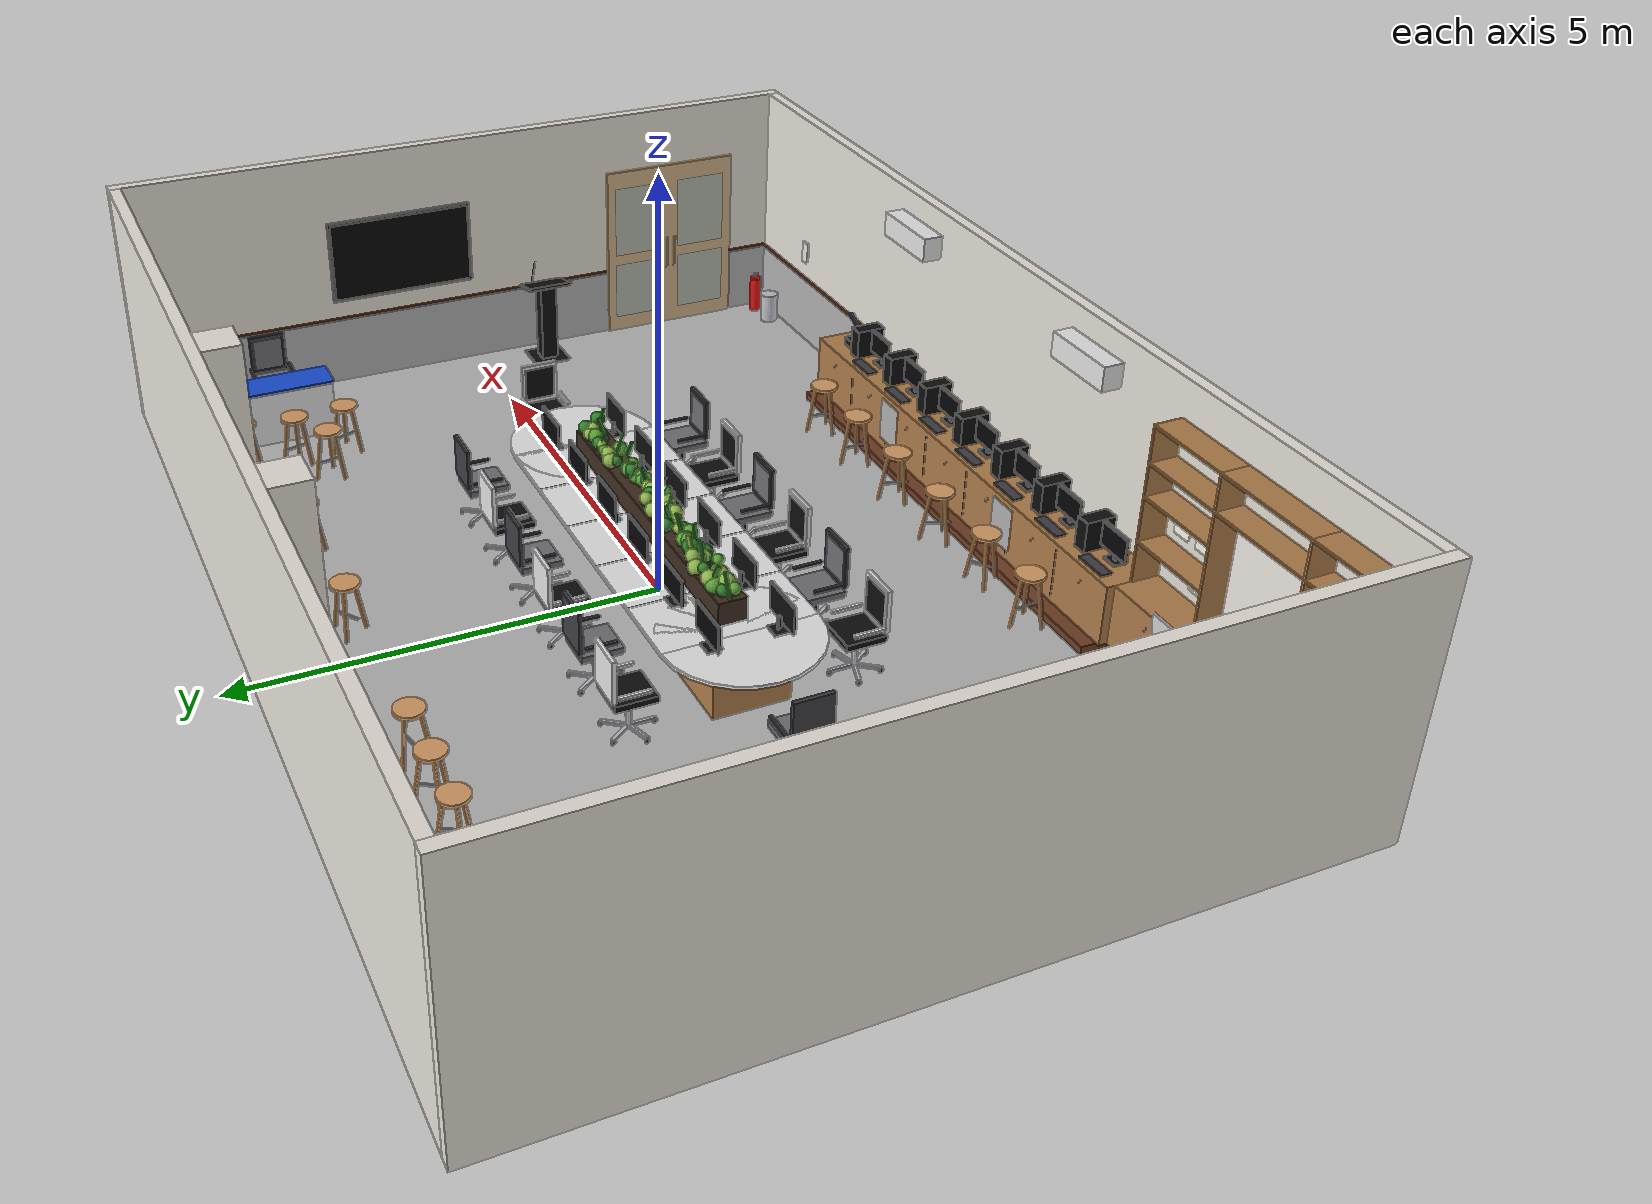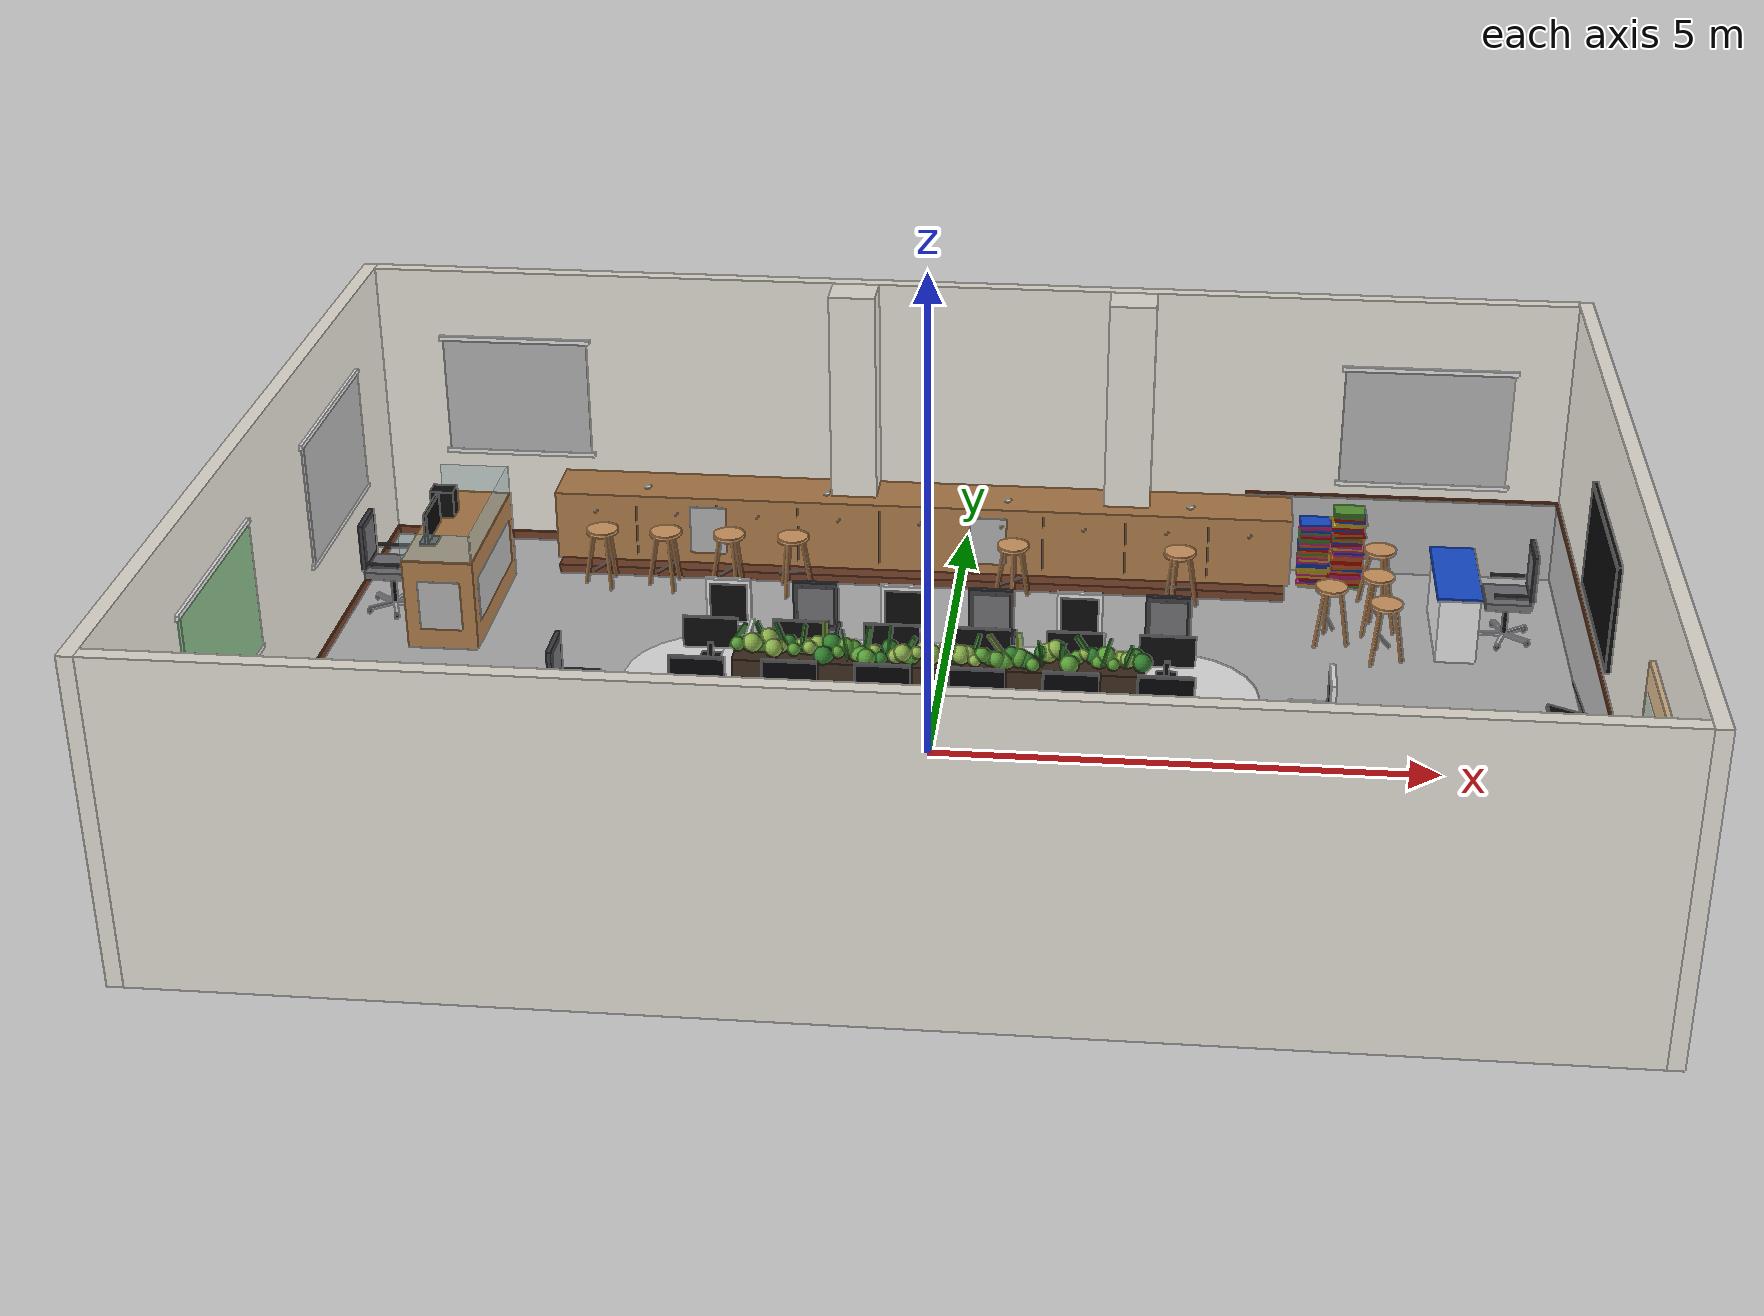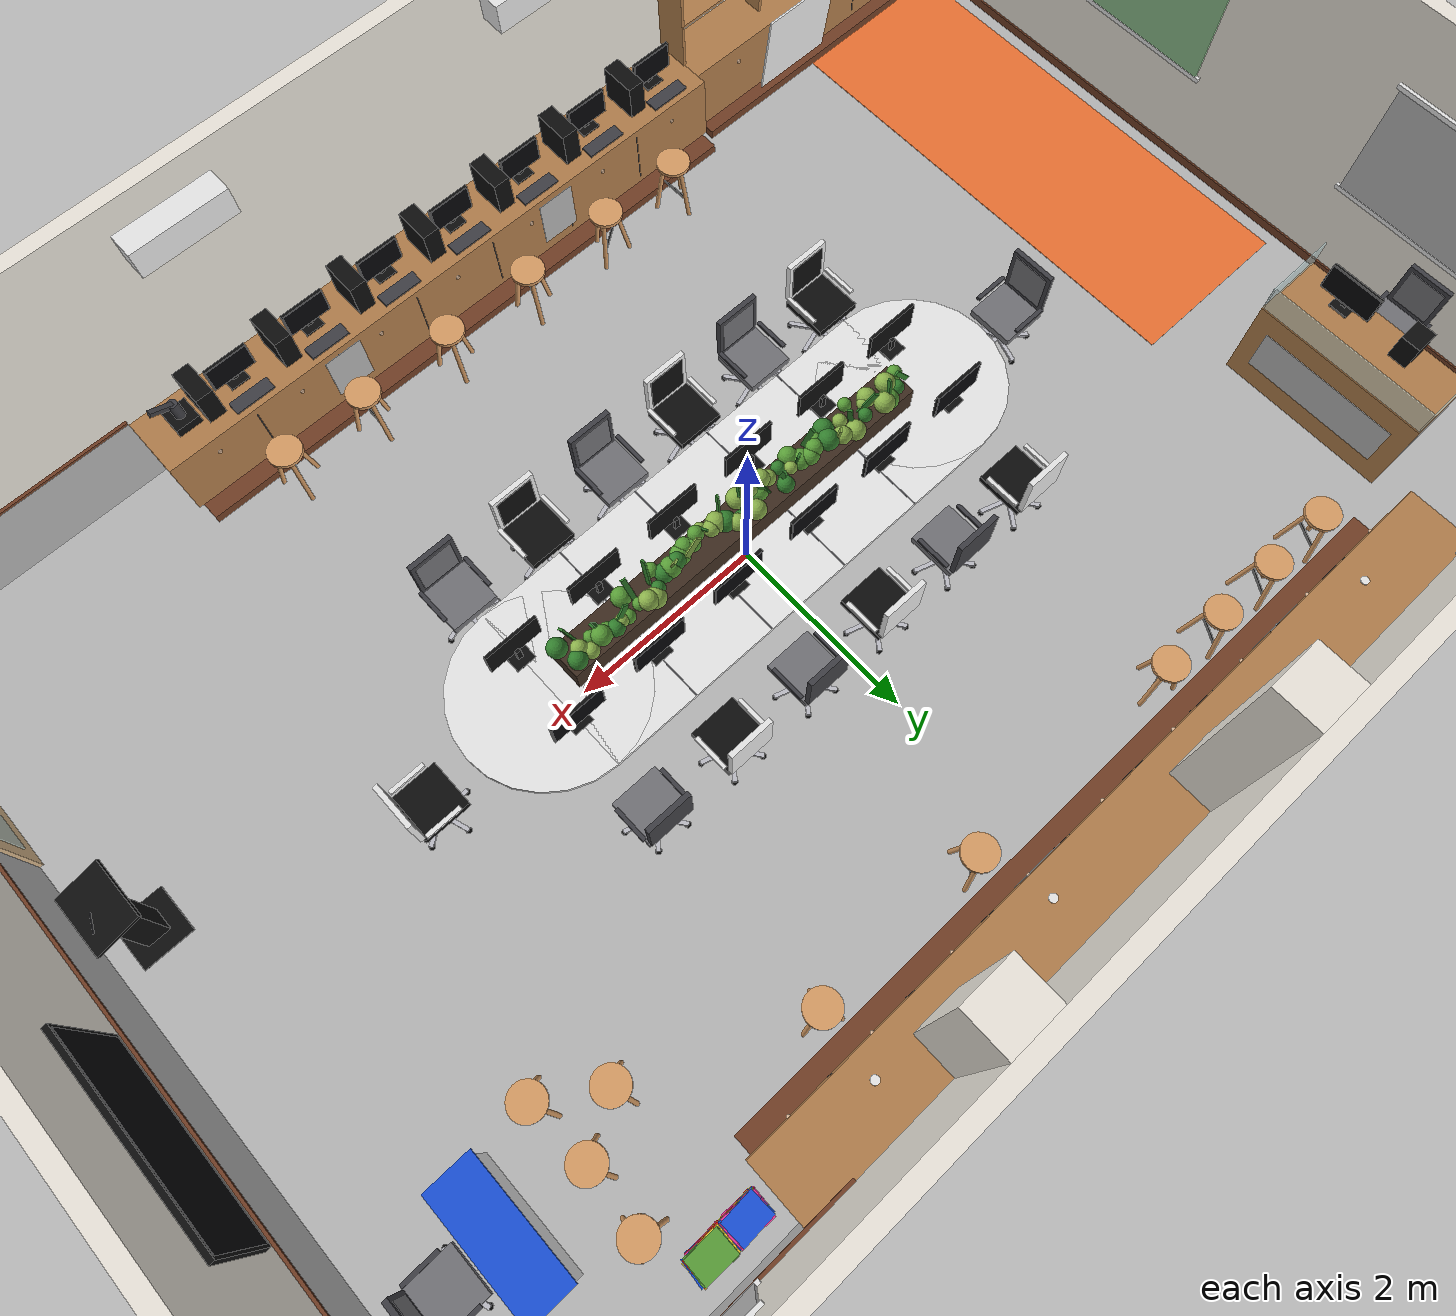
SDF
<?xml version='1.0'?>
<!-- AUTO-GENERATED by generate_lab_world.py - edit that script, not this file. -->
<sdf version='1.6'>
  <world name='mahadev_lab'>
    <!-- physics identical to svan_gazebo/worlds/simple_world.sdf so the robot behaves the same -->
    <physics type='ode'>
      <max_step_size>0.001</max_step_size>
      <real_time_factor>1</real_time_factor>
      <real_time_update_rate>1000</real_time_update_rate>
    </physics>
    <gravity>0 0 -9.81</gravity>
    <scene>
      <ambient>0.55 0.55 0.55 1</ambient>
      <background>0.75 0.8 0.85 1</background>
      <shadows>true</shadows>
    </scene>
    <include><uri>model://sun</uri></include>
    <light name='ceiling_1' type='point'><pose>-3 0 3.0 0 0 0</pose><diffuse>0.35 0.35 0.33 1</diffuse>
      <attenuation><range>12</range><constant>0.6</constant><linear>0.05</linear><quadratic>0.005</quadratic></attenuation>
      <cast_shadows>false</cast_shadows></light>
    <light name='ceiling_2' type='point'><pose>3 0 3.0 0 0 0</pose><diffuse>0.35 0.35 0.33 1</diffuse>
      <attenuation><range>12</range><constant>0.6</constant><linear>0.05</linear><quadratic>0.005</quadratic></attenuation>
      <cast_shadows>false</cast_shadows></light>
    <model name='gplane'>
      <static>true</static>
      <link name='plane'>
        <collision name='plane'>
          <geometry><plane><normal>0 0 1</normal></plane></geometry>
          <surface><friction><ode><mu>100</mu><mu2>100</mu2></ode></friction></surface>
        </collision>
      </link>
    </model>
    <model name='wall_front_tv'><static>true</static><pose>6.5750 0.0000 0.0000 0.0000 0.0000 0.0000</pose><link name='link'><visual name='v1'><pose>0.0000 0.0000 1.6000 0.0000 0.0000 0.0000</pose><geometry><box><size>0.15 9.3 3.2</size></box></geometry><material><ambient>0.93 0.91 0.87 1</ambient><diffuse>0.93 0.91 0.87 1</diffuse><specular>0.1 0.1 0.1 1</specular></material></visual><collision name='c1'><pose>0.0000 0.0000 1.6000 0.0000 0.0000 0.0000</pose><geometry><box><size>0.15 9.3 3.2</size></box></geometry><surface><friction><ode><mu>100</mu><mu2>100</mu2></ode></friction></surface></collision><visual name='v2'><pose>-0.0850 0.0000 0.4500 0.0000 0.0000 0.0000</pose><geometry><box><size>0.02 9 0.9</size></box></geometry><material><script><uri>model://mahadev_lab_media/materials/scripts</uri><uri>model://mahadev_lab_media/materials/textures</uri><name>Mahadev/wall_slats_15_1</name></script></material></visual><visual name='v3'><pose>-0.0850 0.0000 0.9150 0.0000 0.0000 0.0000</pose><geometry><box><size>0.04 9 0.03</size></box></geometry><material><ambient>0.45 0.25 0.15 1</ambient><diffuse>0.45 0.25 0.15 1</diffuse><specular>0.1 0.1 0.1 1</specular></material></visual><visual name='v4'><pose>-0.1150 1.0000 1.7500 0.0000 0.0000 0.0000</pose><geometry><box><size>0.05 1.95 1.12</size></box></geometry><material><ambient>0.05 0.05 0.05 1</ambient><diffuse>0.05 0.05 0.05 1</diffuse><specular>0.1 0.1 0.1 1</specular></material></visual><visual name='v5'><pose>-0.1410 1.0000 1.7500 0.0000 0.0000 0.0000</pose><geometry><box><size>0.002 1.89 1.06</size></box></geometry><material><ambient>0.02 0.02 0.03 1</ambient><diffuse>0.02 0.02 0.03 1</diffuse><specular>0.1 0.1 0.1 1</specular></material></visual><visual name='v6'><pose>-0.1050 -2.9500 1.2000 0.0000 0.0000 0.0000</pose><geometry><box><size>0.05 1.9 2.4</size></box></geometry><material><ambient>0.85 0.72 0.55 1</ambient><diffuse>0.85 0.72 0.55 1</diffuse><specular>0.1 0.1 0.1 1</specular></material></visual><visual name='v7'><pose>-0.1350 -3.4250 1.6500 0.0000 0.0000 0.0000</pose><geometry><box><size>0.01 0.7 1</size></box></geometry><material><ambient>0.75 0.85 0.85 1</ambient><diffuse>0.75 0.85 0.85 1</diffuse><specular>0.1 0.1 0.1 1</specular></material><transparency>0.3</transparency></visual><visual name='v8'><pose>-0.1350 -3.4250 0.6000 0.0000 0.0000 0.0000</pose><geometry><box><size>0.01 0.7 0.8</size></box></geometry><material><ambient>0.75 0.85 0.85 1</ambient><diffuse>0.75 0.85 0.85 1</diffuse><specular>0.1 0.1 0.1 1</specular></material><transparency>0.3</transparency></visual><visual name='v9'><pose>-0.1550 -3.0100 1.1000 0.0000 0.0000 0.0000</pose><geometry><box><size>0.03 0.02 0.45</size></box></geometry><material><ambient>0.85 0.72 0.55 1</ambient><diffuse>0.85 0.72 0.55 1</diffuse><specular>0.1 0.1 0.1 1</specular></material></visual><visual name='v10'><pose>-0.1350 -2.4750 1.6500 0.0000 0.0000 0.0000</pose><geometry><box><size>0.01 0.7 1</size></box></geometry><material><ambient>0.75 0.85 0.85 1</ambient><diffuse>0.75 0.85 0.85 1</diffuse><specular>0.1 0.1 0.1 1</specular></material><transparency>0.3</transparency></visual><visual name='v11'><pose>-0.1350 -2.4750 0.6000 0.0000 0.0000 0.0000</pose><geometry><box><size>0.01 0.7 0.8</size></box></geometry><material><ambient>0.75 0.85 0.85 1</ambient><diffuse>0.75 0.85 0.85 1</diffuse><specular>0.1 0.1 0.1 1</specular></material><transparency>0.3</transparency></visual><visual name='v12'><pose>-0.1550 -2.8900 1.1000 0.0000 0.0000 0.0000</pose><geometry><box><size>0.03 0.02 0.45</size></box></geometry><material><ambient>0.85 0.72 0.55 1</ambient><diffuse>0.85 0.72 0.55 1</diffuse><specular>0.1 0.1 0.1 1</specular></material></visual></link></model>
    <model name='wall_back_windows'><static>true</static><pose>-6.5750 0.0000 0.0000 0.0000 0.0000 0.0000</pose><link name='link'><visual name='v1'><pose>0.0000 0.0000 1.6000 0.0000 0.0000 0.0000</pose><geometry><box><size>0.15 9.3 3.2</size></box></geometry><material><ambient>0.93 0.91 0.87 1</ambient><diffuse>0.93 0.91 0.87 1</diffuse><specular>0.1 0.1 0.1 1</specular></material></visual><collision name='c1'><pose>0.0000 0.0000 1.6000 0.0000 0.0000 0.0000</pose><geometry><box><size>0.15 9.3 3.2</size></box></geometry><surface><friction><ode><mu>100</mu><mu2>100</mu2></ode></friction></surface></collision><visual name='v2'><pose>0.0850 0.0000 0.0500 0.0000 0.0000 0.0000</pose><geometry><box><size>0.02 9 0.1</size></box></geometry><material><ambient>0.45 0.25 0.15 1</ambient><diffuse>0.45 0.25 0.15 1</diffuse><specular>0.1 0.1 0.1 1</specular></material></visual><visual name='v3'><pose>0.0950 -1.4000 1.7500 0.0000 0.0000 0.0000</pose><geometry><box><size>0.03 2 1.3</size></box></geometry><material><ambient>0.55 0.75 0.55 1</ambient><diffuse>0.55 0.75 0.55 1</diffuse><specular>0.1 0.1 0.1 1</specular></material></visual><visual name='v4'><pose>0.0950 -1.4000 1.0800 0.0000 0.0000 0.0000</pose><geometry><box><size>0.035 2.08 0.05</size></box></geometry><material><ambient>0.92 0.92 0.92 1</ambient><diffuse>0.92 0.92 0.92 1</diffuse><specular>0.1 0.1 0.1 1</specular></material></visual><visual name='v5'><pose>0.0950 -1.4000 2.4200 0.0000 0.0000 0.0000</pose><geometry><box><size>0.035 2.08 0.05</size></box></geometry><material><ambient>0.92 0.92 0.92 1</ambient><diffuse>0.92 0.92 0.92 1</diffuse><specular>0.1 0.1 0.1 1</specular></material></visual><visual name='v6'><pose>0.0950 2.4000 1.7500 0.0000 0.0000 0.0000</pose><geometry><box><size>0.03 2 1.3</size></box></geometry><material><script><uri>model://mahadev_lab_media/materials/scripts</uri><uri>model://mahadev_lab_media/materials/textures</uri><name>Mahadev/blinds_1_1</name></script></material></visual><visual name='v7'><pose>0.0950 2.4000 1.0800 0.0000 0.0000 0.0000</pose><geometry><box><size>0.035 2.08 0.05</size></box></geometry><material><ambient>0.92 0.92 0.92 1</ambient><diffuse>0.92 0.92 0.92 1</diffuse><specular>0.1 0.1 0.1 1</specular></material></visual><visual name='v8'><pose>0.0950 2.4000 2.4200 0.0000 0.0000 0.0000</pose><geometry><box><size>0.035 2.08 0.05</size></box></geometry><material><ambient>0.92 0.92 0.92 1</ambient><diffuse>0.92 0.92 0.92 1</diffuse><specular>0.1 0.1 0.1 1</specular></material></visual></link></model>
    <model name='wall_right_pcs'><static>true</static><pose>0.0000 -4.5750 0.0000 0.0000 0.0000 0.0000</pose><link name='link'><visual name='v1'><pose>0.0000 0.0000 1.6000 0.0000 0.0000 0.0000</pose><geometry><box><size>13 0.15 3.2</size></box></geometry><material><ambient>0.93 0.91 0.87 1</ambient><diffuse>0.93 0.91 0.87 1</diffuse><specular>0.1 0.1 0.1 1</specular></material></visual><collision name='c1'><pose>0.0000 0.0000 1.6000 0.0000 0.0000 0.0000</pose><geometry><box><size>13 0.15 3.2</size></box></geometry><surface><friction><ode><mu>100</mu><mu2>100</mu2></ode></friction></surface></collision><visual name='v2'><pose>0.0000 0.0850 0.0500 0.0000 0.0000 0.0000</pose><geometry><box><size>13 0.02 0.1</size></box></geometry><material><ambient>0.45 0.25 0.15 1</ambient><diffuse>0.45 0.25 0.15 1</diffuse><specular>0.1 0.1 0.1 1</specular></material></visual><visual name='v3'><pose>5.0000 0.0870 0.4500 0.0000 0.0000 0.0000</pose><geometry><box><size>3 0.02 0.9</size></box></geometry><material><script><uri>model://mahadev_lab_media/materials/scripts</uri><uri>model://mahadev_lab_media/materials/textures</uri><name>Mahadev/wall_slats_5_1</name></script></material></visual><visual name='v4'><pose>5.0000 0.0870 0.9150 0.0000 0.0000 0.0000</pose><geometry><box><size>3 0.04 0.03</size></box></geometry><material><ambient>0.45 0.25 0.15 1</ambient><diffuse>0.45 0.25 0.15 1</diffuse><specular>0.1 0.1 0.1 1</specular></material></visual><visual name='v5'><pose>-1.5000 0.2050 2.7500 0.0000 0.0000 0.0000</pose><geometry><box><size>0.95 0.25 0.3</size></box></geometry><material><ambient>0.92 0.92 0.92 1</ambient><diffuse>0.92 0.92 0.92 1</diffuse><specular>0.1 0.1 0.1 1</specular></material></visual><visual name='v6'><pose>2.2000 0.2050 2.7500 0.0000 0.0000 0.0000</pose><geometry><box><size>0.95 0.25 0.3</size></box></geometry><material><ambient>0.92 0.92 0.92 1</ambient><diffuse>0.92 0.92 0.92 1</diffuse><specular>0.1 0.1 0.1 1</specular></material></visual><visual name='v7'><pose>5.2000 0.0850 1.3000 0.0000 0.0000 0.0000</pose><geometry><box><size>0.15 0.02 0.3</size></box></geometry><material><ambient>0.92 0.92 0.92 1</ambient><diffuse>0.92 0.92 0.92 1</diffuse><specular>0.1 0.1 0.1 1</specular></material></visual></link></model>
    <model name='wall_left_counter'><static>true</static><pose>0.0000 4.5750 0.0000 0.0000 0.0000 0.0000</pose><link name='link'><visual name='v1'><pose>0.0000 0.0000 1.6000 0.0000 0.0000 0.0000</pose><geometry><box><size>13 0.15 3.2</size></box></geometry><material><ambient>0.93 0.91 0.87 1</ambient><diffuse>0.93 0.91 0.87 1</diffuse><specular>0.1 0.1 0.1 1</specular></material></visual><collision name='c1'><pose>0.0000 0.0000 1.6000 0.0000 0.0000 0.0000</pose><geometry><box><size>13 0.15 3.2</size></box></geometry><surface><friction><ode><mu>100</mu><mu2>100</mu2></ode></friction></surface></collision><visual name='v2'><pose>0.0000 -0.0850 0.0500 0.0000 0.0000 0.0000</pose><geometry><box><size>13 0.02 0.1</size></box></geometry><material><ambient>0.45 0.25 0.15 1</ambient><diffuse>0.45 0.25 0.15 1</diffuse><specular>0.1 0.1 0.1 1</specular></material></visual><visual name='v3'><pose>4.8000 -0.0870 0.4500 0.0000 0.0000 0.0000</pose><geometry><box><size>3.4 0.02 0.9</size></box></geometry><material><script><uri>model://mahadev_lab_media/materials/scripts</uri><uri>model://mahadev_lab_media/materials/textures</uri><name>Mahadev/wall_slats_5.7_1</name></script></material></visual><visual name='v4'><pose>4.8000 -0.0870 0.9150 0.0000 0.0000 0.0000</pose><geometry><box><size>3.4 0.04 0.03</size></box></geometry><material><ambient>0.45 0.25 0.15 1</ambient><diffuse>0.45 0.25 0.15 1</diffuse><specular>0.1 0.1 0.1 1</specular></material></visual><visual name='v5'><pose>5.0000 -0.0950 1.7500 0.0000 0.0000 0.0000</pose><geometry><box><size>1.8 0.03 1.3</size></box></geometry><material><script><uri>model://mahadev_lab_media/materials/scripts</uri><uri>model://mahadev_lab_media/materials/textures</uri><name>Mahadev/blinds_1_1</name></script></material></visual><visual name='v6'><pose>5.0000 -0.0950 1.0800 0.0000 0.0000 0.0000</pose><geometry><box><size>1.88 0.035 0.05</size></box></geometry><material><ambient>0.92 0.92 0.92 1</ambient><diffuse>0.92 0.92 0.92 1</diffuse><specular>0.1 0.1 0.1 1</specular></material></visual><visual name='v7'><pose>5.0000 -0.0950 2.4200 0.0000 0.0000 0.0000</pose><geometry><box><size>1.88 0.035 0.05</size></box></geometry><material><ambient>0.92 0.92 0.92 1</ambient><diffuse>0.92 0.92 0.92 1</diffuse><specular>0.1 0.1 0.1 1</specular></material></visual><visual name='v8'><pose>-5.0000 -0.0950 1.7500 0.0000 0.0000 0.0000</pose><geometry><box><size>1.6 0.03 1.3</size></box></geometry><material><script><uri>model://mahadev_lab_media/materials/scripts</uri><uri>model://mahadev_lab_media/materials/textures</uri><name>Mahadev/blinds_1_1</name></script></material></visual><visual name='v9'><pose>-5.0000 -0.0950 1.0800 0.0000 0.0000 0.0000</pose><geometry><box><size>1.68 0.035 0.05</size></box></geometry><material><ambient>0.92 0.92 0.92 1</ambient><diffuse>0.92 0.92 0.92 1</diffuse><specular>0.1 0.1 0.1 1</specular></material></visual><visual name='v10'><pose>-5.0000 -0.0950 2.4200 0.0000 0.0000 0.0000</pose><geometry><box><size>1.68 0.035 0.05</size></box></geometry><material><ambient>0.92 0.92 0.92 1</ambient><diffuse>0.92 0.92 0.92 1</diffuse><specular>0.1 0.1 0.1 1</specular></material></visual></link></model>
    <model name='floor_tiles'><static>true</static><pose>0.0000 0.0000 0.0000 0.0000 0.0000 0.0000</pose><link name='link'><visual name='v1'><pose>0.0000 0.0000 -0.0050 0.0000 0.0000 0.0000</pose><geometry><box><size>13 9 0.01</size></box></geometry><material><script><uri>model://mahadev_lab_media/materials/scripts</uri><uri>model://mahadev_lab_media/materials/textures</uri><name>Mahadev/floor_tiles_5.4_3.8</name></script></material></visual></link></model>
    <model name='pc_counter'><static>true</static><pose>0.0000 0.0000 0.0000 0.0000 0.0000 0.0000</pose><link name='link'><visual name='v1'><pose>0.2500 -4.1750 0.4750 0.0000 0.0000 0.0000</pose><geometry><box><size>6.5 0.65 0.75</size></box></geometry><material><script><uri>model://mahadev_lab_media/materials/scripts</uri><uri>model://mahadev_lab_media/materials/textures</uri><name>Mahadev/wood_light_6.5_1</name></script></material></visual><collision name='c1'><pose>0.2500 -4.1750 0.4750 0.0000 0.0000 0.0000</pose><geometry><box><size>6.5 0.65 0.75</size></box></geometry><surface><friction><ode><mu>100</mu><mu2>100</mu2></ode></friction></surface></collision><visual name='v2'><pose>0.2500 -3.9100 0.0500 0.0000 0.0000 0.0000</pose><geometry><box><size>6.4 0.5 0.1</size></box></geometry><material><ambient>0.45 0.25 0.15 1</ambient><diffuse>0.45 0.25 0.15 1</diffuse><specular>0.1 0.1 0.1 1</specular></material></visual><visual name='v3'><pose>-2.0714 -3.8470 0.4750 0.0000 0.0000 0.0000</pose><geometry><box><size>0.008 0.004 0.6</size></box></geometry><material><ambient>0.25 0.25 0.27 1</ambient><diffuse>0.25 0.25 0.27 1</diffuse><specular>0.1 0.1 0.1 1</specular></material></visual><visual name='v4'><pose>-1.1429 -3.8470 0.4750 0.0000 0.0000 0.0000</pose><geometry><box><size>0.008 0.004 0.6</size></box></geometry><material><ambient>0.25 0.25 0.27 1</ambient><diffuse>0.25 0.25 0.27 1</diffuse><specular>0.1 0.1 0.1 1</specular></material></visual><visual name='v5'><pose>-0.2143 -3.8470 0.4750 0.0000 0.0000 0.0000</pose><geometry><box><size>0.008 0.004 0.6</size></box></geometry><material><ambient>0.25 0.25 0.27 1</ambient><diffuse>0.25 0.25 0.27 1</diffuse><specular>0.1 0.1 0.1 1</specular></material></visual><visual name='v6'><pose>0.7143 -3.8470 0.4750 0.0000 0.0000 0.0000</pose><geometry><box><size>0.008 0.004 0.6</size></box></geometry><material><ambient>0.25 0.25 0.27 1</ambient><diffuse>0.25 0.25 0.27 1</diffuse><specular>0.1 0.1 0.1 1</specular></material></visual><visual name='v7'><pose>1.6429 -3.8470 0.4750 0.0000 0.0000 0.0000</pose><geometry><box><size>0.008 0.004 0.6</size></box></geometry><material><ambient>0.25 0.25 0.27 1</ambient><diffuse>0.25 0.25 0.27 1</diffuse><specular>0.1 0.1 0.1 1</specular></material></visual><visual name='v8'><pose>2.5714 -3.8470 0.4750 0.0000 0.0000 0.0000</pose><geometry><box><size>0.008 0.004 0.6</size></box></geometry><material><ambient>0.25 0.25 0.27 1</ambient><diffuse>0.25 0.25 0.27 1</diffuse><specular>0.1 0.1 0.1 1</specular></material></visual><visual name='v9'><pose>-2.5357 -3.8470 0.6500 0.0000 0.0000 0.0000</pose><geometry><sphere><radius>0.02</radius></sphere></geometry><material><ambient>0.84 0.7 0.58 1</ambient><diffuse>0.84 0.7 0.58 1</diffuse><specular>0.1 0.1 0.1 1</specular></material></visual><visual name='v10'><pose>-1.6071 -3.8470 0.6500 0.0000 0.0000 0.0000</pose><geometry><sphere><radius>0.02</radius></sphere></geometry><material><ambient>0.84 0.7 0.58 1</ambient><diffuse>0.84 0.7 0.58 1</diffuse><specular>0.1 0.1 0.1 1</specular></material></visual><visual name='v11'><pose>-0.6786 -3.8470 0.6500 0.0000 0.0000 0.0000</pose><geometry><sphere><radius>0.02</radius></sphere></geometry><material><ambient>0.84 0.7 0.58 1</ambient><diffuse>0.84 0.7 0.58 1</diffuse><specular>0.1 0.1 0.1 1</specular></material></visual><visual name='v12'><pose>0.2500 -3.8470 0.6500 0.0000 0.0000 0.0000</pose><geometry><sphere><radius>0.02</radius></sphere></geometry><material><ambient>0.84 0.7 0.58 1</ambient><diffuse>0.84 0.7 0.58 1</diffuse><specular>0.1 0.1 0.1 1</specular></material></visual><visual name='v13'><pose>1.1786 -3.8470 0.6500 0.0000 0.0000 0.0000</pose><geometry><sphere><radius>0.02</radius></sphere></geometry><material><ambient>0.84 0.7 0.58 1</ambient><diffuse>0.84 0.7 0.58 1</diffuse><specular>0.1 0.1 0.1 1</specular></material></visual><visual name='v14'><pose>2.1071 -3.8470 0.6500 0.0000 0.0000 0.0000</pose><geometry><sphere><radius>0.02</radius></sphere></geometry><material><ambient>0.84 0.7 0.58 1</ambient><diffuse>0.84 0.7 0.58 1</diffuse><specular>0.1 0.1 0.1 1</specular></material></visual><visual name='v15'><pose>3.0357 -3.8470 0.6500 0.0000 0.0000 0.0000</pose><geometry><sphere><radius>0.02</radius></sphere></geometry><material><ambient>0.84 0.7 0.58 1</ambient><diffuse>0.84 0.7 0.58 1</diffuse><specular>0.1 0.1 0.1 1</specular></material></visual><visual name='v16'><pose>-1.0000 -3.8440 0.5000 0.0000 0.0000 0.0000</pose><geometry><box><size>0.4 0.004 0.55</size></box></geometry><material><script><uri>model://mahadev_lab_media/materials/scripts</uri><uri>model://mahadev_lab_media/materials/textures</uri><name>Mahadev/lattice_2_3</name></script></material></visual><visual name='v17'><pose>1.6000 -3.8440 0.5000 0.0000 0.0000 0.0000</pose><geometry><box><size>0.4 0.004 0.55</size></box></geometry><material><script><uri>model://mahadev_lab_media/materials/scripts</uri><uri>model://mahadev_lab_media/materials/textures</uri><name>Mahadev/lattice_2_3</name></script></material></visual><visual name='v18'><pose>-2.6000 -4.2400 0.8600 0.0000 0.0000 1.5708</pose><geometry><box><size>0.18 0.2 0.02</size></box></geometry><material><ambient>0.05 0.05 0.05 1</ambient><diffuse>0.05 0.05 0.05 1</diffuse><specular>0.1 0.1 0.1 1</specular></material></visual><visual name='v19'><pose>-2.6000 -4.2400 0.9400 0.0000 0.0000 1.5708</pose><geometry><box><size>0.03 0.05 0.16</size></box></geometry><material><ambient>0.05 0.05 0.05 1</ambient><diffuse>0.05 0.05 0.05 1</diffuse><specular>0.1 0.1 0.1 1</specular></material></visual><visual name='v20'><pose>-2.6000 -4.2000 1.1000 0.0000 0.0000 1.5708</pose><geometry><box><size>0.03 0.45 0.3</size></box></geometry><material><ambient>0.05 0.05 0.05 1</ambient><diffuse>0.05 0.05 0.05 1</diffuse><specular>0.1 0.1 0.1 1</specular></material></visual><visual name='v21'><pose>-2.6000 -4.1840 1.1000 0.0000 0.0000 1.5708</pose><geometry><box><size>0.002 0.43 0.28</size></box></geometry><material><ambient>0.02 0.02 0.03 1</ambient><diffuse>0.02 0.02 0.03 1</diffuse><specular>0.1 0.1 0.1 1</specular></material></visual><visual name='v22'><pose>-2.2500 -4.2000 1.0400 0.0000 0.0000 0.0000</pose><geometry><box><size>0.18 0.38 0.38</size></box></geometry><material><ambient>0.05 0.05 0.05 1</ambient><diffuse>0.05 0.05 0.05 1</diffuse><specular>0.1 0.1 0.1 1</specular></material></visual><visual name='v23'><pose>-2.6000 -3.9800 0.8600 0.0000 0.0000 0.0000</pose><geometry><box><size>0.42 0.14 0.02</size></box></geometry><material><ambient>0.25 0.25 0.27 1</ambient><diffuse>0.25 0.25 0.27 1</diffuse><specular>0.1 0.1 0.1 1</specular></material></visual><visual name='v24'><pose>-1.7500 -4.2400 0.8600 0.0000 0.0000 1.5708</pose><geometry><box><size>0.18 0.2 0.02</size></box></geometry><material><ambient>0.05 0.05 0.05 1</ambient><diffuse>0.05 0.05 0.05 1</diffuse><specular>0.1 0.1 0.1 1</specular></material></visual><visual name='v25'><pose>-1.7500 -4.2400 0.9400 0.0000 0.0000 1.5708</pose><geometry><box><size>0.03 0.05 0.16</size></box></geometry><material><ambient>0.05 0.05 0.05 1</ambient><diffuse>0.05 0.05 0.05 1</diffuse><specular>0.1 0.1 0.1 1</specular></material></visual><visual name='v26'><pose>-1.7500 -4.2000 1.1000 0.0000 0.0000 1.5708</pose><geometry><box><size>0.03 0.45 0.3</size></box></geometry><material><ambient>0.05 0.05 0.05 1</ambient><diffuse>0.05 0.05 0.05 1</diffuse><specular>0.1 0.1 0.1 1</specular></material></visual><visual name='v27'><pose>-1.7500 -4.1840 1.1000 0.0000 0.0000 1.5708</pose><geometry><box><size>0.002 0.43 0.28</size></box></geometry><material><ambient>0.02 0.02 0.03 1</ambient><diffuse>0.02 0.02 0.03 1</diffuse><specular>0.1 0.1 0.1 1</specular></material></visual><visual name='v28'><pose>-1.4000 -4.2000 1.0400 0.0000 0.0000 0.0000</pose><geometry><box><size>0.18 0.38 0.38</size></box></geometry><material><ambient>0.05 0.05 0.05 1</ambient><diffuse>0.05 0.05 0.05 1</diffuse><specular>0.1 0.1 0.1 1</specular></material></visual><visual name='v29'><pose>-1.7500 -3.9800 0.8600 0.0000 0.0000 0.0000</pose><geometry><box><size>0.42 0.14 0.02</size></box></geometry><material><ambient>0.25 0.25 0.27 1</ambient><diffuse>0.25 0.25 0.27 1</diffuse><specular>0.1 0.1 0.1 1</specular></material></visual><visual name='v30'><pose>-0.9000 -4.2400 0.8600 0.0000 0.0000 1.5708</pose><geometry><box><size>0.18 0.2 0.02</size></box></geometry><material><ambient>0.05 0.05 0.05 1</ambient><diffuse>0.05 0.05 0.05 1</diffuse><specular>0.1 0.1 0.1 1</specular></material></visual><visual name='v31'><pose>-0.9000 -4.2400 0.9400 0.0000 0.0000 1.5708</pose><geometry><box><size>0.03 0.05 0.16</size></box></geometry><material><ambient>0.05 0.05 0.05 1</ambient><diffuse>0.05 0.05 0.05 1</diffuse><specular>0.1 0.1 0.1 1</specular></material></visual><visual name='v32'><pose>-0.9000 -4.2000 1.1000 0.0000 0.0000 1.5708</pose><geometry><box><size>0.03 0.45 0.3</size></box></geometry><material><ambient>0.05 0.05 0.05 1</ambient><diffuse>0.05 0.05 0.05 1</diffuse><specular>0.1 0.1 0.1 1</specular></material></visual><visual name='v33'><pose>-0.9000 -4.1840 1.1000 0.0000 0.0000 1.5708</pose><geometry><box><size>0.002 0.43 0.28</size></box></geometry><material><ambient>0.02 0.02 0.03 1</ambient><diffuse>0.02 0.02 0.03 1</diffuse><specular>0.1 0.1 0.1 1</specular></material></visual><visual name='v34'><pose>-0.5500 -4.2000 1.0400 0.0000 0.0000 0.0000</pose><geometry><box><size>0.18 0.38 0.38</size></box></geometry><material><ambient>0.05 0.05 0.05 1</ambient><diffuse>0.05 0.05 0.05 1</diffuse><specular>0.1 0.1 0.1 1</specular></material></visual><visual name='v35'><pose>-0.9000 -3.9800 0.8600 0.0000 0.0000 0.0000</pose><geometry><box><size>0.42 0.14 0.02</size></box></geometry><material><ambient>0.25 0.25 0.27 1</ambient><diffuse>0.25 0.25 0.27 1</diffuse><specular>0.1 0.1 0.1 1</specular></material></visual><visual name='v36'><pose>-0.0500 -4.2400 0.8600 0.0000 0.0000 1.5708</pose><geometry><box><size>0.18 0.2 0.02</size></box></geometry><material><ambient>0.05 0.05 0.05 1</ambient><diffuse>0.05 0.05 0.05 1</diffuse><specular>0.1 0.1 0.1 1</specular></material></visual><visual name='v37'><pose>-0.0500 -4.2400 0.9400 0.0000 0.0000 1.5708</pose><geometry><box><size>0.03 0.05 0.16</size></box></geometry><material><ambient>0.05 0.05 0.05 1</ambient><diffuse>0.05 0.05 0.05 1</diffuse><specular>0.1 0.1 0.1 1</specular></material></visual><visual name='v38'><pose>-0.0500 -4.2000 1.1000 0.0000 0.0000 1.5708</pose><geometry><box><size>0.03 0.45 0.3</size></box></geometry><material><ambient>0.05 0.05 0.05 1</ambient><diffuse>0.05 0.05 0.05 1</diffuse><specular>0.1 0.1 0.1 1</specular></material></visual><visual name='v39'><pose>-0.0500 -4.1840 1.1000 0.0000 0.0000 1.5708</pose><geometry><box><size>0.002 0.43 0.28</size></box></geometry><material><ambient>0.02 0.02 0.03 1</ambient><diffuse>0.02 0.02 0.03 1</diffuse><specular>0.1 0.1 0.1 1</specular></material></visual><visual name='v40'><pose>0.3000 -4.2000 1.0400 0.0000 0.0000 0.0000</pose><geometry><box><size>0.18 0.38 0.38</size></box></geometry><material><ambient>0.05 0.05 0.05 1</ambient><diffuse>0.05 0.05 0.05 1</diffuse><specular>0.1 0.1 0.1 1</specular></material></visual><visual name='v41'><pose>-0.0500 -3.9800 0.8600 0.0000 0.0000 0.0000</pose><geometry><box><size>0.42 0.14 0.02</size></box></geometry><material><ambient>0.25 0.25 0.27 1</ambient><diffuse>0.25 0.25 0.27 1</diffuse><specular>0.1 0.1 0.1 1</specular></material></visual><visual name='v42'><pose>0.8000 -4.2400 0.8600 0.0000 0.0000 1.5708</pose><geometry><box><size>0.18 0.2 0.02</size></box></geometry><material><ambient>0.05 0.05 0.05 1</ambient><diffuse>0.05 0.05 0.05 1</diffuse><specular>0.1 0.1 0.1 1</specular></material></visual><visual name='v43'><pose>0.8000 -4.2400 0.9400 0.0000 0.0000 1.5708</pose><geometry><box><size>0.03 0.05 0.16</size></box></geometry><material><ambient>0.05 0.05 0.05 1</ambient><diffuse>0.05 0.05 0.05 1</diffuse><specular>0.1 0.1 0.1 1</specular></material></visual><visual name='v44'><pose>0.8000 -4.2000 1.1000 0.0000 0.0000 1.5708</pose><geometry><box><size>0.03 0.45 0.3</size></box></geometry><material><ambient>0.05 0.05 0.05 1</ambient><diffuse>0.05 0.05 0.05 1</diffuse><specular>0.1 0.1 0.1 1</specular></material></visual><visual name='v45'><pose>0.8000 -4.1840 1.1000 0.0000 0.0000 1.5708</pose><geometry><box><size>0.002 0.43 0.28</size></box></geometry><material><ambient>0.02 0.02 0.03 1</ambient><diffuse>0.02 0.02 0.03 1</diffuse><specular>0.1 0.1 0.1 1</specular></material></visual><visual name='v46'><pose>1.1500 -4.2000 1.0400 0.0000 0.0000 0.0000</pose><geometry><box><size>0.18 0.38 0.38</size></box></geometry><material><ambient>0.05 0.05 0.05 1</ambient><diffuse>0.05 0.05 0.05 1</diffuse><specular>0.1 0.1 0.1 1</specular></material></visual><visual name='v47'><pose>0.8000 -3.9800 0.8600 0.0000 0.0000 0.0000</pose><geometry><box><size>0.42 0.14 0.02</size></box></geometry><material><ambient>0.25 0.25 0.27 1</ambient><diffuse>0.25 0.25 0.27 1</diffuse><specular>0.1 0.1 0.1 1</specular></material></visual><visual name='v48'><pose>1.6500 -4.2400 0.8600 0.0000 0.0000 1.5708</pose><geometry><box><size>0.18 0.2 0.02</size></box></geometry><material><ambient>0.05 0.05 0.05 1</ambient><diffuse>0.05 0.05 0.05 1</diffuse><specular>0.1 0.1 0.1 1</specular></material></visual><visual name='v49'><pose>1.6500 -4.2400 0.9400 0.0000 0.0000 1.5708</pose><geometry><box><size>0.03 0.05 0.16</size></box></geometry><material><ambient>0.05 0.05 0.05 1</ambient><diffuse>0.05 0.05 0.05 1</diffuse><specular>0.1 0.1 0.1 1</specular></material></visual><visual name='v50'><pose>1.6500 -4.2000 1.1000 0.0000 0.0000 1.5708</pose><geometry><box><size>0.03 0.45 0.3</size></box></geometry><material><ambient>0.05 0.05 0.05 1</ambient><diffuse>0.05 0.05 0.05 1</diffuse><specular>0.1 0.1 0.1 1</specular></material></visual><visual name='v51'><pose>1.6500 -4.1840 1.1000 0.0000 0.0000 1.5708</pose><geometry><box><size>0.002 0.43 0.28</size></box></geometry><material><ambient>0.02 0.02 0.03 1</ambient><diffuse>0.02 0.02 0.03 1</diffuse><specular>0.1 0.1 0.1 1</specular></material></visual><visual name='v52'><pose>2.0000 -4.2000 1.0400 0.0000 0.0000 0.0000</pose><geometry><box><size>0.18 0.38 0.38</size></box></geometry><material><ambient>0.05 0.05 0.05 1</ambient><diffuse>0.05 0.05 0.05 1</diffuse><specular>0.1 0.1 0.1 1</specular></material></visual><visual name='v53'><pose>1.6500 -3.9800 0.8600 0.0000 0.0000 0.0000</pose><geometry><box><size>0.42 0.14 0.02</size></box></geometry><material><ambient>0.25 0.25 0.27 1</ambient><diffuse>0.25 0.25 0.27 1</diffuse><specular>0.1 0.1 0.1 1</specular></material></visual><visual name='v54'><pose>2.5000 -4.2400 0.8600 0.0000 0.0000 1.5708</pose><geometry><box><size>0.18 0.2 0.02</size></box></geometry><material><ambient>0.05 0.05 0.05 1</ambient><diffuse>0.05 0.05 0.05 1</diffuse><specular>0.1 0.1 0.1 1</specular></material></visual><visual name='v55'><pose>2.5000 -4.2400 0.9400 0.0000 0.0000 1.5708</pose><geometry><box><size>0.03 0.05 0.16</size></box></geometry><material><ambient>0.05 0.05 0.05 1</ambient><diffuse>0.05 0.05 0.05 1</diffuse><specular>0.1 0.1 0.1 1</specular></material></visual><visual name='v56'><pose>2.5000 -4.2000 1.1000 0.0000 0.0000 1.5708</pose><geometry><box><size>0.03 0.45 0.3</size></box></geometry><material><ambient>0.05 0.05 0.05 1</ambient><diffuse>0.05 0.05 0.05 1</diffuse><specular>0.1 0.1 0.1 1</specular></material></visual><visual name='v57'><pose>2.5000 -4.1840 1.1000 0.0000 0.0000 1.5708</pose><geometry><box><size>0.002 0.43 0.28</size></box></geometry><material><ambient>0.02 0.02 0.03 1</ambient><diffuse>0.02 0.02 0.03 1</diffuse><specular>0.1 0.1 0.1 1</specular></material></visual><visual name='v58'><pose>2.8500 -4.2000 1.0400 0.0000 0.0000 0.0000</pose><geometry><box><size>0.18 0.38 0.38</size></box></geometry><material><ambient>0.05 0.05 0.05 1</ambient><diffuse>0.05 0.05 0.05 1</diffuse><specular>0.1 0.1 0.1 1</specular></material></visual><visual name='v59'><pose>2.5000 -3.9800 0.8600 0.0000 0.0000 0.0000</pose><geometry><box><size>0.42 0.14 0.02</size></box></geometry><material><ambient>0.25 0.25 0.27 1</ambient><diffuse>0.25 0.25 0.27 1</diffuse><specular>0.1 0.1 0.1 1</specular></material></visual><visual name='v60'><pose>3.1000 -4.2000 0.9000 0.0000 0.0000 0.0000</pose><geometry><box><size>0.25 0.25 0.1</size></box></geometry><material><ambient>0.05 0.05 0.05 1</ambient><diffuse>0.05 0.05 0.05 1</diffuse><specular>0.1 0.1 0.1 1</specular></material></visual><visual name='v61'><pose>3.1000 -4.2000 1.0500 0.0000 0.0000 0.0000</pose><geometry><cylinder><radius>0.05</radius><length>0.2</length></cylinder></geometry><material><ambient>0.25 0.25 0.27 1</ambient><diffuse>0.25 0.25 0.27 1</diffuse><specular>0.1 0.1 0.1 1</specular></material></visual><visual name='v62'><pose>3.2000 -4.2000 1.1700 0.0000 -0.4000 0.0000</pose><geometry><box><size>0.25 0.05 0.05</size></box></geometry><material><ambient>0.25 0.25 0.27 1</ambient><diffuse>0.25 0.25 0.27 1</diffuse><specular>0.1 0.1 0.1 1</specular></material></visual></link></model>
    <model name='stool_pc_0'><static>true</static><pose>-2.2000 -3.4500 0.0000 0.0000 0.0000 1.6058</pose><link name='link'><visual name='v1'><pose>0.0000 0.0000 0.6400 0.0000 0.0000 0.0000</pose><geometry><cylinder><radius>0.17</radius><length>0.04</length></cylinder></geometry><material><ambient>0.85 0.62 0.4 1</ambient><diffuse>0.85 0.62 0.4 1</diffuse><specular>0.1 0.1 0.1 1</specular></material></visual><visual name='v2'><pose>0.1500 0.0000 0.3100 0.0000 -0.1599 0.0000</pose><geometry><cylinder><radius>0.022</radius><length>0.63</length></cylinder></geometry><material><ambient>0.85 0.62 0.4 1</ambient><diffuse>0.85 0.62 0.4 1</diffuse><specular>0.1 0.1 0.1 1</specular></material></visual><visual name='v3'><pose>-0.0750 0.1299 0.3100 0.0000 -0.1599 2.0944</pose><geometry><cylinder><radius>0.022</radius><length>0.63</length></cylinder></geometry><material><ambient>0.85 0.62 0.4 1</ambient><diffuse>0.85 0.62 0.4 1</diffuse><specular>0.1 0.1 0.1 1</specular></material></visual><visual name='v4'><pose>-0.0750 -0.1299 0.3100 0.0000 -0.1599 4.1888</pose><geometry><cylinder><radius>0.022</radius><length>0.63</length></cylinder></geometry><material><ambient>0.85 0.62 0.4 1</ambient><diffuse>0.85 0.62 0.4 1</diffuse><specular>0.1 0.1 0.1 1</specular></material></visual><visual name='v5'><pose>0.0000 0.0000 0.2200 0.0000 0.0000 0.0000</pose><geometry><box><size>0.3 0.02 0.02</size></box></geometry><material><ambient>0.05 0.05 0.05 1</ambient><diffuse>0.05 0.05 0.05 1</diffuse><specular>0.1 0.1 0.1 1</specular></material></visual><collision name='c6'><pose>0.0000 0.0000 0.3300 0 0 0</pose><geometry><cylinder><radius>0.2</radius><length>0.66</length></cylinder></geometry></collision></link></model>
    <model name='stool_pc_1'><static>true</static><pose>-1.3000 -3.4500 0.0000 0.0000 0.0000 0.6207</pose><link name='link'><visual name='v1'><pose>0.0000 0.0000 0.6400 0.0000 0.0000 0.0000</pose><geometry><cylinder><radius>0.17</radius><length>0.04</length></cylinder></geometry><material><ambient>0.85 0.62 0.4 1</ambient><diffuse>0.85 0.62 0.4 1</diffuse><specular>0.1 0.1 0.1 1</specular></material></visual><visual name='v2'><pose>0.1500 0.0000 0.3100 0.0000 -0.1599 0.0000</pose><geometry><cylinder><radius>0.022</radius><length>0.63</length></cylinder></geometry><material><ambient>0.85 0.62 0.4 1</ambient><diffuse>0.85 0.62 0.4 1</diffuse><specular>0.1 0.1 0.1 1</specular></material></visual><visual name='v3'><pose>-0.0750 0.1299 0.3100 0.0000 -0.1599 2.0944</pose><geometry><cylinder><radius>0.022</radius><length>0.63</length></cylinder></geometry><material><ambient>0.85 0.62 0.4 1</ambient><diffuse>0.85 0.62 0.4 1</diffuse><specular>0.1 0.1 0.1 1</specular></material></visual><visual name='v4'><pose>-0.0750 -0.1299 0.3100 0.0000 -0.1599 4.1888</pose><geometry><cylinder><radius>0.022</radius><length>0.63</length></cylinder></geometry><material><ambient>0.85 0.62 0.4 1</ambient><diffuse>0.85 0.62 0.4 1</diffuse><specular>0.1 0.1 0.1 1</specular></material></visual><visual name='v5'><pose>0.0000 0.0000 0.2200 0.0000 0.0000 0.0000</pose><geometry><box><size>0.3 0.02 0.02</size></box></geometry><material><ambient>0.05 0.05 0.05 1</ambient><diffuse>0.05 0.05 0.05 1</diffuse><specular>0.1 0.1 0.1 1</specular></material></visual><collision name='c6'><pose>0.0000 0.0000 0.3300 0 0 0</pose><geometry><cylinder><radius>0.2</radius><length>0.66</length></cylinder></geometry></collision></link></model>
    <model name='stool_pc_2'><static>true</static><pose>-0.3000 -3.4500 0.0000 0.0000 0.0000 1.1836</pose><link name='link'><visual name='v1'><pose>0.0000 0.0000 0.6400 0.0000 0.0000 0.0000</pose><geometry><cylinder><radius>0.17</radius><length>0.04</length></cylinder></geometry><material><ambient>0.85 0.62 0.4 1</ambient><diffuse>0.85 0.62 0.4 1</diffuse><specular>0.1 0.1 0.1 1</specular></material></visual><visual name='v2'><pose>0.1500 0.0000 0.3100 0.0000 -0.1599 0.0000</pose><geometry><cylinder><radius>0.022</radius><length>0.63</length></cylinder></geometry><material><ambient>0.85 0.62 0.4 1</ambient><diffuse>0.85 0.62 0.4 1</diffuse><specular>0.1 0.1 0.1 1</specular></material></visual><visual name='v3'><pose>-0.0750 0.1299 0.3100 0.0000 -0.1599 2.0944</pose><geometry><cylinder><radius>0.022</radius><length>0.63</length></cylinder></geometry><material><ambient>0.85 0.62 0.4 1</ambient><diffuse>0.85 0.62 0.4 1</diffuse><specular>0.1 0.1 0.1 1</specular></material></visual><visual name='v4'><pose>-0.0750 -0.1299 0.3100 0.0000 -0.1599 4.1888</pose><geometry><cylinder><radius>0.022</radius><length>0.63</length></cylinder></geometry><material><ambient>0.85 0.62 0.4 1</ambient><diffuse>0.85 0.62 0.4 1</diffuse><specular>0.1 0.1 0.1 1</specular></material></visual><visual name='v5'><pose>0.0000 0.0000 0.2200 0.0000 0.0000 0.0000</pose><geometry><box><size>0.3 0.02 0.02</size></box></geometry><material><ambient>0.05 0.05 0.05 1</ambient><diffuse>0.05 0.05 0.05 1</diffuse><specular>0.1 0.1 0.1 1</specular></material></visual><collision name='c6'><pose>0.0000 0.0000 0.3300 0 0 0</pose><geometry><cylinder><radius>0.2</radius><length>0.66</length></cylinder></geometry></collision></link></model>
    <model name='stool_pc_3'><static>true</static><pose>0.7000 -3.4500 0.0000 0.0000 0.0000 1.2530</pose><link name='link'><visual name='v1'><pose>0.0000 0.0000 0.6400 0.0000 0.0000 0.0000</pose><geometry><cylinder><radius>0.17</radius><length>0.04</length></cylinder></geometry><material><ambient>0.85 0.62 0.4 1</ambient><diffuse>0.85 0.62 0.4 1</diffuse><specular>0.1 0.1 0.1 1</specular></material></visual><visual name='v2'><pose>0.1500 0.0000 0.3100 0.0000 -0.1599 0.0000</pose><geometry><cylinder><radius>0.022</radius><length>0.63</length></cylinder></geometry><material><ambient>0.85 0.62 0.4 1</ambient><diffuse>0.85 0.62 0.4 1</diffuse><specular>0.1 0.1 0.1 1</specular></material></visual><visual name='v3'><pose>-0.0750 0.1299 0.3100 0.0000 -0.1599 2.0944</pose><geometry><cylinder><radius>0.022</radius><length>0.63</length></cylinder></geometry><material><ambient>0.85 0.62 0.4 1</ambient><diffuse>0.85 0.62 0.4 1</diffuse><specular>0.1 0.1 0.1 1</specular></material></visual><visual name='v4'><pose>-0.0750 -0.1299 0.3100 0.0000 -0.1599 4.1888</pose><geometry><cylinder><radius>0.022</radius><length>0.63</length></cylinder></geometry><material><ambient>0.85 0.62 0.4 1</ambient><diffuse>0.85 0.62 0.4 1</diffuse><specular>0.1 0.1 0.1 1</specular></material></visual><visual name='v5'><pose>0.0000 0.0000 0.2200 0.0000 0.0000 0.0000</pose><geometry><box><size>0.3 0.02 0.02</size></box></geometry><material><ambient>0.05 0.05 0.05 1</ambient><diffuse>0.05 0.05 0.05 1</diffuse><specular>0.1 0.1 0.1 1</specular></material></visual><collision name='c6'><pose>0.0000 0.0000 0.3300 0 0 0</pose><geometry><cylinder><radius>0.2</radius><length>0.66</length></cylinder></geometry></collision></link></model>
    <model name='stool_pc_4'><static>true</static><pose>1.7000 -3.4500 0.0000 0.0000 0.0000 1.5383</pose><link name='link'><visual name='v1'><pose>0.0000 0.0000 0.6400 0.0000 0.0000 0.0000</pose><geometry><cylinder><radius>0.17</radius><length>0.04</length></cylinder></geometry><material><ambient>0.85 0.62 0.4 1</ambient><diffuse>0.85 0.62 0.4 1</diffuse><specular>0.1 0.1 0.1 1</specular></material></visual><visual name='v2'><pose>0.1500 0.0000 0.3100 0.0000 -0.1599 0.0000</pose><geometry><cylinder><radius>0.022</radius><length>0.63</length></cylinder></geometry><material><ambient>0.85 0.62 0.4 1</ambient><diffuse>0.85 0.62 0.4 1</diffuse><specular>0.1 0.1 0.1 1</specular></material></visual><visual name='v3'><pose>-0.0750 0.1299 0.3100 0.0000 -0.1599 2.0944</pose><geometry><cylinder><radius>0.022</radius><length>0.63</length></cylinder></geometry><material><ambient>0.85 0.62 0.4 1</ambient><diffuse>0.85 0.62 0.4 1</diffuse><specular>0.1 0.1 0.1 1</specular></material></visual><visual name='v4'><pose>-0.0750 -0.1299 0.3100 0.0000 -0.1599 4.1888</pose><geometry><cylinder><radius>0.022</radius><length>0.63</length></cylinder></geometry><material><ambient>0.85 0.62 0.4 1</ambient><diffuse>0.85 0.62 0.4 1</diffuse><specular>0.1 0.1 0.1 1</specular></material></visual><visual name='v5'><pose>0.0000 0.0000 0.2200 0.0000 0.0000 0.0000</pose><geometry><box><size>0.3 0.02 0.02</size></box></geometry><material><ambient>0.05 0.05 0.05 1</ambient><diffuse>0.05 0.05 0.05 1</diffuse><specular>0.1 0.1 0.1 1</specular></material></visual><collision name='c6'><pose>0.0000 0.0000 0.3300 0 0 0</pose><geometry><cylinder><radius>0.2</radius><length>0.66</length></cylinder></geometry></collision></link></model>
    <model name='stool_pc_5'><static>true</static><pose>2.6000 -3.4500 0.0000 0.0000 0.0000 1.3275</pose><link name='link'><visual name='v1'><pose>0.0000 0.0000 0.6400 0.0000 0.0000 0.0000</pose><geometry><cylinder><radius>0.17</radius><length>0.04</length></cylinder></geometry><material><ambient>0.85 0.62 0.4 1</ambient><diffuse>0.85 0.62 0.4 1</diffuse><specular>0.1 0.1 0.1 1</specular></material></visual><visual name='v2'><pose>0.1500 0.0000 0.3100 0.0000 -0.1599 0.0000</pose><geometry><cylinder><radius>0.022</radius><length>0.63</length></cylinder></geometry><material><ambient>0.85 0.62 0.4 1</ambient><diffuse>0.85 0.62 0.4 1</diffuse><specular>0.1 0.1 0.1 1</specular></material></visual><visual name='v3'><pose>-0.0750 0.1299 0.3100 0.0000 -0.1599 2.0944</pose><geometry><cylinder><radius>0.022</radius><length>0.63</length></cylinder></geometry><material><ambient>0.85 0.62 0.4 1</ambient><diffuse>0.85 0.62 0.4 1</diffuse><specular>0.1 0.1 0.1 1</specular></material></visual><visual name='v4'><pose>-0.0750 -0.1299 0.3100 0.0000 -0.1599 4.1888</pose><geometry><cylinder><radius>0.022</radius><length>0.63</length></cylinder></geometry><material><ambient>0.85 0.62 0.4 1</ambient><diffuse>0.85 0.62 0.4 1</diffuse><specular>0.1 0.1 0.1 1</specular></material></visual><visual name='v5'><pose>0.0000 0.0000 0.2200 0.0000 0.0000 0.0000</pose><geometry><box><size>0.3 0.02 0.02</size></box></geometry><material><ambient>0.05 0.05 0.05 1</ambient><diffuse>0.05 0.05 0.05 1</diffuse><specular>0.1 0.1 0.1 1</specular></material></visual><collision name='c6'><pose>0.0000 0.0000 0.3300 0 0 0</pose><geometry><cylinder><radius>0.2</radius><length>0.66</length></cylinder></geometry></collision></link></model>
    <model name='shelf_unit'><static>true</static><pose>0.0000 0.0000 0.0000 0.0000 0.0000 0.0000</pose><link name='link'><visual name='v1'><pose>-4.7000 -4.2250 0.4750 0.0000 0.0000 0.0000</pose><geometry><box><size>3.4 0.55 0.75</size></box></geometry><material><script><uri>model://mahadev_lab_media/materials/scripts</uri><uri>model://mahadev_lab_media/materials/textures</uri><name>Mahadev/wood_light_3.4_1</name></script></material></visual><collision name='c1'><pose>-4.7000 -4.2250 0.4750 0.0000 0.0000 0.0000</pose><geometry><box><size>3.4 0.55 0.75</size></box></geometry><surface><friction><ode><mu>100</mu><mu2>100</mu2></ode></friction></surface></collision><visual name='v2'><pose>-4.7000 -4.0100 0.0500 0.0000 0.0000 0.0000</pose><geometry><box><size>3.3 0.4 0.1</size></box></geometry><material><ambient>0.45 0.25 0.15 1</ambient><diffuse>0.45 0.25 0.15 1</diffuse><specular>0.1 0.1 0.1 1</specular></material></visual><visual name='v3'><pose>-5.2667 -3.9470 0.4750 0.0000 0.0000 0.0000</pose><geometry><box><size>0.008 0.004 0.6</size></box></geometry><material><ambient>0.25 0.25 0.27 1</ambient><diffuse>0.25 0.25 0.27 1</diffuse><specular>0.1 0.1 0.1 1</specular></material></visual><visual name='v4'><pose>-4.1333 -3.9470 0.4750 0.0000 0.0000 0.0000</pose><geometry><box><size>0.008 0.004 0.6</size></box></geometry><material><ambient>0.25 0.25 0.27 1</ambient><diffuse>0.25 0.25 0.27 1</diffuse><specular>0.1 0.1 0.1 1</specular></material></visual><visual name='v5'><pose>-5.8333 -3.9470 0.6500 0.0000 0.0000 0.0000</pose><geometry><sphere><radius>0.02</radius></sphere></geometry><material><ambient>0.84 0.7 0.58 1</ambient><diffuse>0.84 0.7 0.58 1</diffuse><specular>0.1 0.1 0.1 1</specular></material></visual><visual name='v6'><pose>-4.7000 -3.9470 0.6500 0.0000 0.0000 0.0000</pose><geometry><sphere><radius>0.02</radius></sphere></geometry><material><ambient>0.84 0.7 0.58 1</ambient><diffuse>0.84 0.7 0.58 1</diffuse><specular>0.1 0.1 0.1 1</specular></material></visual><visual name='v7'><pose>-3.5667 -3.9470 0.6500 0.0000 0.0000 0.0000</pose><geometry><sphere><radius>0.02</radius></sphere></geometry><material><ambient>0.84 0.7 0.58 1</ambient><diffuse>0.84 0.7 0.58 1</diffuse><specular>0.1 0.1 0.1 1</specular></material></visual><visual name='v8'><pose>-6.4000 -4.3250 1.8000 0.0000 0.0000 0.0000</pose><geometry><box><size>0.03 0.35 1.9</size></box></geometry><material><script><uri>model://mahadev_lab_media/materials/scripts</uri><uri>model://mahadev_lab_media/materials/textures</uri><name>Mahadev/wood_light_1_2</name></script></material></visual><visual name='v9'><pose>-5.3500 -4.3250 1.8000 0.0000 0.0000 0.0000</pose><geometry><box><size>0.03 0.35 1.9</size></box></geometry><material><script><uri>model://mahadev_lab_media/materials/scripts</uri><uri>model://mahadev_lab_media/materials/textures</uri><name>Mahadev/wood_light_1_2</name></script></material></visual><visual name='v10'><pose>-4.0500 -4.3250 1.8000 0.0000 0.0000 0.0000</pose><geometry><box><size>0.03 0.35 1.9</size></box></geometry><material><script><uri>model://mahadev_lab_media/materials/scripts</uri><uri>model://mahadev_lab_media/materials/textures</uri><name>Mahadev/wood_light_1_2</name></script></material></visual><visual name='v11'><pose>-3.0000 -4.3250 1.8000 0.0000 0.0000 0.0000</pose><geometry><box><size>0.03 0.35 1.9</size></box></geometry><material><script><uri>model://mahadev_lab_media/materials/scripts</uri><uri>model://mahadev_lab_media/materials/textures</uri><name>Mahadev/wood_light_1_2</name></script></material></visual><visual name='v12'><pose>-5.8750 -4.3250 1.3500 0.0000 0.0000 0.0000</pose><geometry><box><size>1.05 0.35 0.03</size></box></geometry><material><script><uri>model://mahadev_lab_media/materials/scripts</uri><uri>model://mahadev_lab_media/materials/textures</uri><name>Mahadev/wood_light_2_1</name></script></material></visual><visual name='v13'><pose>-5.8750 -4.3250 1.9000 0.0000 0.0000 0.0000</pose><geometry><box><size>1.05 0.35 0.03</size></box></geometry><material><script><uri>model://mahadev_lab_media/materials/scripts</uri><uri>model://mahadev_lab_media/materials/textures</uri><name>Mahadev/wood_light_2_1</name></script></material></visual><visual name='v14'><pose>-5.8750 -4.3250 2.3000 0.0000 0.0000 0.0000</pose><geometry><box><size>1.05 0.35 0.03</size></box></geometry><material><script><uri>model://mahadev_lab_media/materials/scripts</uri><uri>model://mahadev_lab_media/materials/textures</uri><name>Mahadev/wood_light_2_1</name></script></material></visual><visual name='v15'><pose>-5.8750 -4.3250 2.7400 0.0000 0.0000 0.0000</pose><geometry><box><size>1.05 0.35 0.03</size></box></geometry><material><script><uri>model://mahadev_lab_media/materials/scripts</uri><uri>model://mahadev_lab_media/materials/textures</uri><name>Mahadev/wood_light_2_1</name></script></material></visual><visual name='v16'><pose>-3.5250 -4.3250 1.3500 0.0000 0.0000 0.0000</pose><geometry><box><size>1.05 0.35 0.03</size></box></geometry><material><script><uri>model://mahadev_lab_media/materials/scripts</uri><uri>model://mahadev_lab_media/materials/textures</uri><name>Mahadev/wood_light_2_1</name></script></material></visual><visual name='v17'><pose>-3.5250 -4.3250 1.9000 0.0000 0.0000 0.0000</pose><geometry><box><size>1.05 0.35 0.03</size></box></geometry><material><script><uri>model://mahadev_lab_media/materials/scripts</uri><uri>model://mahadev_lab_media/materials/textures</uri><name>Mahadev/wood_light_2_1</name></script></material></visual><visual name='v18'><pose>-3.5250 -4.3250 2.3000 0.0000 0.0000 0.0000</pose><geometry><box><size>1.05 0.35 0.03</size></box></geometry><material><script><uri>model://mahadev_lab_media/materials/scripts</uri><uri>model://mahadev_lab_media/materials/textures</uri><name>Mahadev/wood_light_2_1</name></script></material></visual><visual name='v19'><pose>-3.5250 -4.3250 2.7400 0.0000 0.0000 0.0000</pose><geometry><box><size>1.05 0.35 0.03</size></box></geometry><material><script><uri>model://mahadev_lab_media/materials/scripts</uri><uri>model://mahadev_lab_media/materials/textures</uri><name>Mahadev/wood_light_2_1</name></script></material></visual><visual name='v20'><pose>-4.7000 -4.3250 2.3000 0.0000 0.0000 0.0000</pose><geometry><box><size>1.3 0.35 0.03</size></box></geometry><material><script><uri>model://mahadev_lab_media/materials/scripts</uri><uri>model://mahadev_lab_media/materials/textures</uri><name>Mahadev/wood_light_2_1</name></script></material></visual><visual name='v21'><pose>-4.7000 -4.3250 2.7400 0.0000 0.0000 0.0000</pose><geometry><box><size>1.3 0.35 0.03</size></box></geometry><material><script><uri>model://mahadev_lab_media/materials/scripts</uri><uri>model://mahadev_lab_media/materials/textures</uri><name>Mahadev/wood_light_2_1</name></script></material></visual><visual name='v22'><pose>-4.7000 -4.4800 1.5500 0.0000 0.0000 0.0000</pose><geometry><box><size>1.25 0.02 1.35</size></box></geometry><material><ambient>0.97 0.95 0.92 1</ambient><diffuse>0.97 0.95 0.92 1</diffuse><specular>0.1 0.1 0.1 1</specular></material></visual><visual name='v23'><pose>-6.0000 -4.4300 1.2000 0.1200 0.0000 0.0000</pose><geometry><box><size>0.24 0.01 0.3</size></box></geometry><material><ambient>0.95 0.95 0.92 1</ambient><diffuse>0.95 0.95 0.92 1</diffuse><specular>0.1 0.1 0.1 1</specular></material></visual><visual name='v24'><pose>-5.6500 -4.4300 1.7000 0.1200 0.0000 0.0000</pose><geometry><box><size>0.24 0.01 0.3</size></box></geometry><material><ambient>0.95 0.95 0.92 1</ambient><diffuse>0.95 0.95 0.92 1</diffuse><specular>0.1 0.1 0.1 1</specular></material></visual><visual name='v25'><pose>-6.0500 -4.4300 1.7000 0.1200 0.0000 0.0000</pose><geometry><box><size>0.24 0.01 0.3</size></box></geometry><material><ambient>0.95 0.95 0.92 1</ambient><diffuse>0.95 0.95 0.92 1</diffuse><specular>0.1 0.1 0.1 1</specular></material></visual><visual name='v26'><pose>-3.7000 -4.4300 1.2000 0.1200 0.0000 0.0000</pose><geometry><box><size>0.24 0.01 0.3</size></box></geometry><material><ambient>0.95 0.95 0.92 1</ambient><diffuse>0.95 0.95 0.92 1</diffuse><specular>0.1 0.1 0.1 1</specular></material></visual><visual name='v27'><pose>-3.3500 -4.4300 1.7000 0.1200 0.0000 0.0000</pose><geometry><box><size>0.24 0.01 0.3</size></box></geometry><material><ambient>0.95 0.95 0.92 1</ambient><diffuse>0.95 0.95 0.92 1</diffuse><specular>0.1 0.1 0.1 1</specular></material></visual><visual name='v28'><pose>-3.7000 -4.4300 1.7000 0.1200 0.0000 0.0000</pose><geometry><box><size>0.24 0.01 0.3</size></box></geometry><material><ambient>0.95 0.95 0.92 1</ambient><diffuse>0.95 0.95 0.92 1</diffuse><specular>0.1 0.1 0.1 1</specular></material></visual><visual name='v29'><pose>-5.8500 -4.4300 2.1500 0.1200 0.0000 0.0000</pose><geometry><box><size>0.24 0.01 0.3</size></box></geometry><material><ambient>0.95 0.95 0.92 1</ambient><diffuse>0.95 0.95 0.92 1</diffuse><specular>0.1 0.1 0.1 1</specular></material></visual><visual name='v30'><pose>-4.7000 -4.2000 0.9200 0.0000 0.0000 0.0000</pose><geometry><box><size>0.35 0.18 0.14</size></box></geometry><material><ambient>0.2 0.5 0.18 1</ambient><diffuse>0.2 0.5 0.18 1</diffuse><specular>0.1 0.1 0.1 1</specular></material></visual><visual name='v31'><pose>-5.0500 -4.2000 0.9500 0.0000 0.0000 0.0000</pose><geometry><cylinder><radius>0.05</radius><length>0.12</length></cylinder></geometry><material><ambient>0.25 0.25 0.27 1</ambient><diffuse>0.25 0.25 0.27 1</diffuse><specular>0.1 0.1 0.1 1</specular></material></visual><visual name='v32'><pose>-4.3500 -4.2000 0.9500 0.0000 0.0000 0.0000</pose><geometry><cylinder><radius>0.05</radius><length>0.12</length></cylinder></geometry><material><ambient>0.25 0.25 0.27 1</ambient><diffuse>0.25 0.25 0.27 1</diffuse><specular>0.1 0.1 0.1 1</specular></material></visual><visual name='v33'><pose>-4.3000 -3.8400 0.5500 -0.1200 0.0000 0.0000</pose><geometry><box><size>0.9 0.02 1.1</size></box></geometry><material><ambient>0.92 0.92 0.92 1</ambient><diffuse>0.92 0.92 0.92 1</diffuse><specular>0.1 0.1 0.1 1</specular></material></visual><collision name='c33'><pose>-4.3000 -3.8400 0.5500 -0.1200 0.0000 0.0000</pose><geometry><box><size>0.9 0.02 1.1</size></box></geometry><surface><friction><ode><mu>100</mu><mu2>100</mu2></ode></friction></surface></collision></link></model>
    <model name='left_counter'><static>true</static><pose>0.0000 0.0000 0.0000 0.0000 0.0000 0.0000</pose><link name='link'><visual name='v1'><pose>-0.4500 4.1750 0.4900 0.0000 0.0000 0.0000</pose><geometry><box><size>8.1 0.65 0.78</size></box></geometry><material><script><uri>model://mahadev_lab_media/materials/scripts</uri><uri>model://mahadev_lab_media/materials/textures</uri><name>Mahadev/wood_light_8.1_1</name></script></material></visual><collision name='c1'><pose>-0.4500 4.1750 0.4900 0.0000 0.0000 0.0000</pose><geometry><box><size>8.1 0.65 0.78</size></box></geometry><surface><friction><ode><mu>100</mu><mu2>100</mu2></ode></friction></surface></collision><visual name='v2'><pose>-0.4500 3.9100 0.0500 0.0000 0.0000 0.0000</pose><geometry><box><size>8 0.5 0.1</size></box></geometry><material><ambient>0.45 0.25 0.15 1</ambient><diffuse>0.45 0.25 0.15 1</diffuse><specular>0.1 0.1 0.1 1</specular></material></visual><visual name='v3'><pose>-3.6000 3.8470 0.4900 0.0000 0.0000 0.0000</pose><geometry><box><size>0.008 0.004 0.63</size></box></geometry><material><ambient>0.25 0.25 0.27 1</ambient><diffuse>0.25 0.25 0.27 1</diffuse><specular>0.1 0.1 0.1 1</specular></material></visual><visual name='v4'><pose>-2.7000 3.8470 0.4900 0.0000 0.0000 0.0000</pose><geometry><box><size>0.008 0.004 0.63</size></box></geometry><material><ambient>0.25 0.25 0.27 1</ambient><diffuse>0.25 0.25 0.27 1</diffuse><specular>0.1 0.1 0.1 1</specular></material></visual><visual name='v5'><pose>-1.8000 3.8470 0.4900 0.0000 0.0000 0.0000</pose><geometry><box><size>0.008 0.004 0.63</size></box></geometry><material><ambient>0.25 0.25 0.27 1</ambient><diffuse>0.25 0.25 0.27 1</diffuse><specular>0.1 0.1 0.1 1</specular></material></visual><visual name='v6'><pose>-0.9000 3.8470 0.4900 0.0000 0.0000 0.0000</pose><geometry><box><size>0.008 0.004 0.63</size></box></geometry><material><ambient>0.25 0.25 0.27 1</ambient><diffuse>0.25 0.25 0.27 1</diffuse><specular>0.1 0.1 0.1 1</specular></material></visual><visual name='v7'><pose>0.0000 3.8470 0.4900 0.0000 0.0000 0.0000</pose><geometry><box><size>0.008 0.004 0.63</size></box></geometry><material><ambient>0.25 0.25 0.27 1</ambient><diffuse>0.25 0.25 0.27 1</diffuse><specular>0.1 0.1 0.1 1</specular></material></visual><visual name='v8'><pose>0.9000 3.8470 0.4900 0.0000 0.0000 0.0000</pose><geometry><box><size>0.008 0.004 0.63</size></box></geometry><material><ambient>0.25 0.25 0.27 1</ambient><diffuse>0.25 0.25 0.27 1</diffuse><specular>0.1 0.1 0.1 1</specular></material></visual><visual name='v9'><pose>1.8000 3.8470 0.4900 0.0000 0.0000 0.0000</pose><geometry><box><size>0.008 0.004 0.63</size></box></geometry><material><ambient>0.25 0.25 0.27 1</ambient><diffuse>0.25 0.25 0.27 1</diffuse><specular>0.1 0.1 0.1 1</specular></material></visual><visual name='v10'><pose>2.7000 3.8470 0.4900 0.0000 0.0000 0.0000</pose><geometry><box><size>0.008 0.004 0.63</size></box></geometry><material><ambient>0.25 0.25 0.27 1</ambient><diffuse>0.25 0.25 0.27 1</diffuse><specular>0.1 0.1 0.1 1</specular></material></visual><visual name='v11'><pose>-4.0500 3.8470 0.6800 0.0000 0.0000 0.0000</pose><geometry><sphere><radius>0.02</radius></sphere></geometry><material><ambient>0.84 0.7 0.58 1</ambient><diffuse>0.84 0.7 0.58 1</diffuse><specular>0.1 0.1 0.1 1</specular></material></visual><visual name='v12'><pose>-3.1500 3.8470 0.6800 0.0000 0.0000 0.0000</pose><geometry><sphere><radius>0.02</radius></sphere></geometry><material><ambient>0.84 0.7 0.58 1</ambient><diffuse>0.84 0.7 0.58 1</diffuse><specular>0.1 0.1 0.1 1</specular></material></visual><visual name='v13'><pose>-2.2500 3.8470 0.6800 0.0000 0.0000 0.0000</pose><geometry><sphere><radius>0.02</radius></sphere></geometry><material><ambient>0.84 0.7 0.58 1</ambient><diffuse>0.84 0.7 0.58 1</diffuse><specular>0.1 0.1 0.1 1</specular></material></visual><visual name='v14'><pose>-1.3500 3.8470 0.6800 0.0000 0.0000 0.0000</pose><geometry><sphere><radius>0.02</radius></sphere></geometry><material><ambient>0.84 0.7 0.58 1</ambient><diffuse>0.84 0.7 0.58 1</diffuse><specular>0.1 0.1 0.1 1</specular></material></visual><visual name='v15'><pose>-0.4500 3.8470 0.6800 0.0000 0.0000 0.0000</pose><geometry><sphere><radius>0.02</radius></sphere></geometry><material><ambient>0.84 0.7 0.58 1</ambient><diffuse>0.84 0.7 0.58 1</diffuse><specular>0.1 0.1 0.1 1</specular></material></visual><visual name='v16'><pose>0.4500 3.8470 0.6800 0.0000 0.0000 0.0000</pose><geometry><sphere><radius>0.02</radius></sphere></geometry><material><ambient>0.84 0.7 0.58 1</ambient><diffuse>0.84 0.7 0.58 1</diffuse><specular>0.1 0.1 0.1 1</specular></material></visual><visual name='v17'><pose>1.3500 3.8470 0.6800 0.0000 0.0000 0.0000</pose><geometry><sphere><radius>0.02</radius></sphere></geometry><material><ambient>0.84 0.7 0.58 1</ambient><diffuse>0.84 0.7 0.58 1</diffuse><specular>0.1 0.1 0.1 1</specular></material></visual><visual name='v18'><pose>2.2500 3.8470 0.6800 0.0000 0.0000 0.0000</pose><geometry><sphere><radius>0.02</radius></sphere></geometry><material><ambient>0.84 0.7 0.58 1</ambient><diffuse>0.84 0.7 0.58 1</diffuse><specular>0.1 0.1 0.1 1</specular></material></visual><visual name='v19'><pose>3.1500 3.8470 0.6800 0.0000 0.0000 0.0000</pose><geometry><sphere><radius>0.02</radius></sphere></geometry><material><ambient>0.84 0.7 0.58 1</ambient><diffuse>0.84 0.7 0.58 1</diffuse><specular>0.1 0.1 0.1 1</specular></material></visual><visual name='v20'><pose>-1.2000 4.2800 1.6000 0.0000 0.0000 0.0000</pose><geometry><box><size>0.5 0.44 3.2</size></box></geometry><material><ambient>0.93 0.91 0.87 1</ambient><diffuse>0.93 0.91 0.87 1</diffuse><specular>0.1 0.1 0.1 1</specular></material></visual><visual name='v21'><pose>1.8000 4.2800 1.6000 0.0000 0.0000 0.0000</pose><geometry><box><size>0.5 0.44 3.2</size></box></geometry><material><ambient>0.93 0.91 0.87 1</ambient><diffuse>0.93 0.91 0.87 1</diffuse><specular>0.1 0.1 0.1 1</specular></material></visual><visual name='v22'><pose>-2.8000 3.8440 0.5000 0.0000 0.0000 0.0000</pose><geometry><box><size>0.4 0.004 0.55</size></box></geometry><material><script><uri>model://mahadev_lab_media/materials/scripts</uri><uri>model://mahadev_lab_media/materials/textures</uri><name>Mahadev/lattice_2_3</name></script></material></visual><visual name='v23'><pose>0.3000 3.8440 0.5000 0.0000 0.0000 0.0000</pose><geometry><box><size>0.4 0.004 0.55</size></box></geometry><material><script><uri>model://mahadev_lab_media/materials/scripts</uri><uri>model://mahadev_lab_media/materials/textures</uri><name>Mahadev/lattice_2_3</name></script></material></visual><visual name='v24'><pose>-3.5000 4.1000 0.8850 0.0000 0.0000 0.0000</pose><geometry><cylinder><radius>0.04</radius><length>0.01</length></cylinder></geometry><material><ambient>0.92 0.92 0.92 1</ambient><diffuse>0.92 0.92 0.92 1</diffuse><specular>0.1 0.1 0.1 1</specular></material></visual><visual name='v25'><pose>-1.5000 4.1000 0.8850 0.0000 0.0000 0.0000</pose><geometry><cylinder><radius>0.04</radius><length>0.01</length></cylinder></geometry><material><ambient>0.92 0.92 0.92 1</ambient><diffuse>0.92 0.92 0.92 1</diffuse><specular>0.1 0.1 0.1 1</specular></material></visual><visual name='v26'><pose>0.5000 4.1000 0.8850 0.0000 0.0000 0.0000</pose><geometry><cylinder><radius>0.04</radius><length>0.01</length></cylinder></geometry><material><ambient>0.92 0.92 0.92 1</ambient><diffuse>0.92 0.92 0.92 1</diffuse><specular>0.1 0.1 0.1 1</specular></material></visual><visual name='v27'><pose>2.5000 4.1000 0.8850 0.0000 0.0000 0.0000</pose><geometry><cylinder><radius>0.04</radius><length>0.01</length></cylinder></geometry><material><ambient>0.92 0.92 0.92 1</ambient><diffuse>0.92 0.92 0.92 1</diffuse><specular>0.1 0.1 0.1 1</specular></material></visual></link></model>
    <model name='stool_left_0'><static>true</static><pose>-3.9000 3.4500 0.0000 0.0000 0.0000 1.0904</pose><link name='link'><visual name='v1'><pose>0.0000 0.0000 0.6400 0.0000 0.0000 0.0000</pose><geometry><cylinder><radius>0.17</radius><length>0.04</length></cylinder></geometry><material><ambient>0.85 0.62 0.4 1</ambient><diffuse>0.85 0.62 0.4 1</diffuse><specular>0.1 0.1 0.1 1</specular></material></visual><visual name='v2'><pose>0.1500 0.0000 0.3100 0.0000 -0.1599 0.0000</pose><geometry><cylinder><radius>0.022</radius><length>0.63</length></cylinder></geometry><material><ambient>0.85 0.62 0.4 1</ambient><diffuse>0.85 0.62 0.4 1</diffuse><specular>0.1 0.1 0.1 1</specular></material></visual><visual name='v3'><pose>-0.0750 0.1299 0.3100 0.0000 -0.1599 2.0944</pose><geometry><cylinder><radius>0.022</radius><length>0.63</length></cylinder></geometry><material><ambient>0.85 0.62 0.4 1</ambient><diffuse>0.85 0.62 0.4 1</diffuse><specular>0.1 0.1 0.1 1</specular></material></visual><visual name='v4'><pose>-0.0750 -0.1299 0.3100 0.0000 -0.1599 4.1888</pose><geometry><cylinder><radius>0.022</radius><length>0.63</length></cylinder></geometry><material><ambient>0.85 0.62 0.4 1</ambient><diffuse>0.85 0.62 0.4 1</diffuse><specular>0.1 0.1 0.1 1</specular></material></visual><visual name='v5'><pose>0.0000 0.0000 0.2200 0.0000 0.0000 0.0000</pose><geometry><box><size>0.3 0.02 0.02</size></box></geometry><material><ambient>0.05 0.05 0.05 1</ambient><diffuse>0.05 0.05 0.05 1</diffuse><specular>0.1 0.1 0.1 1</specular></material></visual><collision name='c6'><pose>0.0000 0.0000 0.3300 0 0 0</pose><geometry><cylinder><radius>0.2</radius><length>0.66</length></cylinder></geometry></collision></link></model>
    <model name='stool_left_1'><static>true</static><pose>-3.2000 3.4500 0.0000 0.0000 0.0000 1.0224</pose><link name='link'><visual name='v1'><pose>0.0000 0.0000 0.6400 0.0000 0.0000 0.0000</pose><geometry><cylinder><radius>0.17</radius><length>0.04</length></cylinder></geometry><material><ambient>0.85 0.62 0.4 1</ambient><diffuse>0.85 0.62 0.4 1</diffuse><specular>0.1 0.1 0.1 1</specular></material></visual><visual name='v2'><pose>0.1500 0.0000 0.3100 0.0000 -0.1599 0.0000</pose><geometry><cylinder><radius>0.022</radius><length>0.63</length></cylinder></geometry><material><ambient>0.85 0.62 0.4 1</ambient><diffuse>0.85 0.62 0.4 1</diffuse><specular>0.1 0.1 0.1 1</specular></material></visual><visual name='v3'><pose>-0.0750 0.1299 0.3100 0.0000 -0.1599 2.0944</pose><geometry><cylinder><radius>0.022</radius><length>0.63</length></cylinder></geometry><material><ambient>0.85 0.62 0.4 1</ambient><diffuse>0.85 0.62 0.4 1</diffuse><specular>0.1 0.1 0.1 1</specular></material></visual><visual name='v4'><pose>-0.0750 -0.1299 0.3100 0.0000 -0.1599 4.1888</pose><geometry><cylinder><radius>0.022</radius><length>0.63</length></cylinder></geometry><material><ambient>0.85 0.62 0.4 1</ambient><diffuse>0.85 0.62 0.4 1</diffuse><specular>0.1 0.1 0.1 1</specular></material></visual><visual name='v5'><pose>0.0000 0.0000 0.2200 0.0000 0.0000 0.0000</pose><geometry><box><size>0.3 0.02 0.02</size></box></geometry><material><ambient>0.05 0.05 0.05 1</ambient><diffuse>0.05 0.05 0.05 1</diffuse><specular>0.1 0.1 0.1 1</specular></material></visual><collision name='c6'><pose>0.0000 0.0000 0.3300 0 0 0</pose><geometry><cylinder><radius>0.2</radius><length>0.66</length></cylinder></geometry></collision></link></model>
    <model name='stool_left_2'><static>true</static><pose>-2.5000 3.4500 0.0000 0.0000 0.0000 1.0558</pose><link name='link'><visual name='v1'><pose>0.0000 0.0000 0.6400 0.0000 0.0000 0.0000</pose><geometry><cylinder><radius>0.17</radius><length>0.04</length></cylinder></geometry><material><ambient>0.85 0.62 0.4 1</ambient><diffuse>0.85 0.62 0.4 1</diffuse><specular>0.1 0.1 0.1 1</specular></material></visual><visual name='v2'><pose>0.1500 0.0000 0.3100 0.0000 -0.1599 0.0000</pose><geometry><cylinder><radius>0.022</radius><length>0.63</length></cylinder></geometry><material><ambient>0.85 0.62 0.4 1</ambient><diffuse>0.85 0.62 0.4 1</diffuse><specular>0.1 0.1 0.1 1</specular></material></visual><visual name='v3'><pose>-0.0750 0.1299 0.3100 0.0000 -0.1599 2.0944</pose><geometry><cylinder><radius>0.022</radius><length>0.63</length></cylinder></geometry><material><ambient>0.85 0.62 0.4 1</ambient><diffuse>0.85 0.62 0.4 1</diffuse><specular>0.1 0.1 0.1 1</specular></material></visual><visual name='v4'><pose>-0.0750 -0.1299 0.3100 0.0000 -0.1599 4.1888</pose><geometry><cylinder><radius>0.022</radius><length>0.63</length></cylinder></geometry><material><ambient>0.85 0.62 0.4 1</ambient><diffuse>0.85 0.62 0.4 1</diffuse><specular>0.1 0.1 0.1 1</specular></material></visual><visual name='v5'><pose>0.0000 0.0000 0.2200 0.0000 0.0000 0.0000</pose><geometry><box><size>0.3 0.02 0.02</size></box></geometry><material><ambient>0.05 0.05 0.05 1</ambient><diffuse>0.05 0.05 0.05 1</diffuse><specular>0.1 0.1 0.1 1</specular></material></visual><collision name='c6'><pose>0.0000 0.0000 0.3300 0 0 0</pose><geometry><cylinder><radius>0.2</radius><length>0.66</length></cylinder></geometry></collision></link></model>
    <model name='stool_left_3'><static>true</static><pose>-1.8000 3.4500 0.0000 0.0000 0.0000 0.2219</pose><link name='link'><visual name='v1'><pose>0.0000 0.0000 0.6400 0.0000 0.0000 0.0000</pose><geometry><cylinder><radius>0.17</radius><length>0.04</length></cylinder></geometry><material><ambient>0.85 0.62 0.4 1</ambient><diffuse>0.85 0.62 0.4 1</diffuse><specular>0.1 0.1 0.1 1</specular></material></visual><visual name='v2'><pose>0.1500 0.0000 0.3100 0.0000 -0.1599 0.0000</pose><geometry><cylinder><radius>0.022</radius><length>0.63</length></cylinder></geometry><material><ambient>0.85 0.62 0.4 1</ambient><diffuse>0.85 0.62 0.4 1</diffuse><specular>0.1 0.1 0.1 1</specular></material></visual><visual name='v3'><pose>-0.0750 0.1299 0.3100 0.0000 -0.1599 2.0944</pose><geometry><cylinder><radius>0.022</radius><length>0.63</length></cylinder></geometry><material><ambient>0.85 0.62 0.4 1</ambient><diffuse>0.85 0.62 0.4 1</diffuse><specular>0.1 0.1 0.1 1</specular></material></visual><visual name='v4'><pose>-0.0750 -0.1299 0.3100 0.0000 -0.1599 4.1888</pose><geometry><cylinder><radius>0.022</radius><length>0.63</length></cylinder></geometry><material><ambient>0.85 0.62 0.4 1</ambient><diffuse>0.85 0.62 0.4 1</diffuse><specular>0.1 0.1 0.1 1</specular></material></visual><visual name='v5'><pose>0.0000 0.0000 0.2200 0.0000 0.0000 0.0000</pose><geometry><box><size>0.3 0.02 0.02</size></box></geometry><material><ambient>0.05 0.05 0.05 1</ambient><diffuse>0.05 0.05 0.05 1</diffuse><specular>0.1 0.1 0.1 1</specular></material></visual><collision name='c6'><pose>0.0000 0.0000 0.3300 0 0 0</pose><geometry><cylinder><radius>0.2</radius><length>0.66</length></cylinder></geometry></collision></link></model>
    <model name='stool_left_4'><static>true</static><pose>0.6000 3.4500 0.0000 0.0000 0.0000 0.6315</pose><link name='link'><visual name='v1'><pose>0.0000 0.0000 0.6400 0.0000 0.0000 0.0000</pose><geometry><cylinder><radius>0.17</radius><length>0.04</length></cylinder></geometry><material><ambient>0.85 0.62 0.4 1</ambient><diffuse>0.85 0.62 0.4 1</diffuse><specular>0.1 0.1 0.1 1</specular></material></visual><visual name='v2'><pose>0.1500 0.0000 0.3100 0.0000 -0.1599 0.0000</pose><geometry><cylinder><radius>0.022</radius><length>0.63</length></cylinder></geometry><material><ambient>0.85 0.62 0.4 1</ambient><diffuse>0.85 0.62 0.4 1</diffuse><specular>0.1 0.1 0.1 1</specular></material></visual><visual name='v3'><pose>-0.0750 0.1299 0.3100 0.0000 -0.1599 2.0944</pose><geometry><cylinder><radius>0.022</radius><length>0.63</length></cylinder></geometry><material><ambient>0.85 0.62 0.4 1</ambient><diffuse>0.85 0.62 0.4 1</diffuse><specular>0.1 0.1 0.1 1</specular></material></visual><visual name='v4'><pose>-0.0750 -0.1299 0.3100 0.0000 -0.1599 4.1888</pose><geometry><cylinder><radius>0.022</radius><length>0.63</length></cylinder></geometry><material><ambient>0.85 0.62 0.4 1</ambient><diffuse>0.85 0.62 0.4 1</diffuse><specular>0.1 0.1 0.1 1</specular></material></visual><visual name='v5'><pose>0.0000 0.0000 0.2200 0.0000 0.0000 0.0000</pose><geometry><box><size>0.3 0.02 0.02</size></box></geometry><material><ambient>0.05 0.05 0.05 1</ambient><diffuse>0.05 0.05 0.05 1</diffuse><specular>0.1 0.1 0.1 1</specular></material></visual><collision name='c6'><pose>0.0000 0.0000 0.3300 0 0 0</pose><geometry><cylinder><radius>0.2</radius><length>0.66</length></cylinder></geometry></collision></link></model>
    <model name='stool_left_5'><static>true</static><pose>2.4000 3.4500 0.0000 0.0000 0.0000 0.1366</pose><link name='link'><visual name='v1'><pose>0.0000 0.0000 0.6400 0.0000 0.0000 0.0000</pose><geometry><cylinder><radius>0.17</radius><length>0.04</length></cylinder></geometry><material><ambient>0.85 0.62 0.4 1</ambient><diffuse>0.85 0.62 0.4 1</diffuse><specular>0.1 0.1 0.1 1</specular></material></visual><visual name='v2'><pose>0.1500 0.0000 0.3100 0.0000 -0.1599 0.0000</pose><geometry><cylinder><radius>0.022</radius><length>0.63</length></cylinder></geometry><material><ambient>0.85 0.62 0.4 1</ambient><diffuse>0.85 0.62 0.4 1</diffuse><specular>0.1 0.1 0.1 1</specular></material></visual><visual name='v3'><pose>-0.0750 0.1299 0.3100 0.0000 -0.1599 2.0944</pose><geometry><cylinder><radius>0.022</radius><length>0.63</length></cylinder></geometry><material><ambient>0.85 0.62 0.4 1</ambient><diffuse>0.85 0.62 0.4 1</diffuse><specular>0.1 0.1 0.1 1</specular></material></visual><visual name='v4'><pose>-0.0750 -0.1299 0.3100 0.0000 -0.1599 4.1888</pose><geometry><cylinder><radius>0.022</radius><length>0.63</length></cylinder></geometry><material><ambient>0.85 0.62 0.4 1</ambient><diffuse>0.85 0.62 0.4 1</diffuse><specular>0.1 0.1 0.1 1</specular></material></visual><visual name='v5'><pose>0.0000 0.0000 0.2200 0.0000 0.0000 0.0000</pose><geometry><box><size>0.3 0.02 0.02</size></box></geometry><material><ambient>0.05 0.05 0.05 1</ambient><diffuse>0.05 0.05 0.05 1</diffuse><specular>0.1 0.1 0.1 1</specular></material></visual><collision name='c6'><pose>0.0000 0.0000 0.3300 0 0 0</pose><geometry><cylinder><radius>0.2</radius><length>0.66</length></cylinder></geometry></collision></link></model>
    <model name='file_stacks'><static>true</static><pose>4.0500 4.1500 0.0000 0.0000 0.0000 0.0000</pose><link name='link'><visual name='v1'><pose>-0.1755 0.0000 0.0200 0.0000 0.0000 -0.0331</pose><geometry><box><size>0.33 0.25 0.024</size></box></geometry><material><ambient>0.95 0.8 0.2 1</ambient><diffuse>0.95 0.8 0.2 1</diffuse><specular>0.1 0.1 0.1 1</specular></material></visual><visual name='v2'><pose>-0.1889 0.0000 0.0450 0.0000 0.0000 -0.0652</pose><geometry><box><size>0.33 0.25 0.024</size></box></geometry><material><ambient>0.9 0.2 0.6 1</ambient><diffuse>0.9 0.2 0.6 1</diffuse><specular>0.1 0.1 0.1 1</specular></material></visual><visual name='v3'><pose>-0.1603 0.0000 0.0700 0.0000 0.0000 0.0145</pose><geometry><box><size>0.33 0.25 0.024</size></box></geometry><material><ambient>0.1 0.32 0.85 1</ambient><diffuse>0.1 0.32 0.85 1</diffuse><specular>0.1 0.1 0.1 1</specular></material></visual><visual name='v4'><pose>-0.1683 0.0000 0.0950 0.0000 0.0000 0.0658</pose><geometry><box><size>0.33 0.25 0.024</size></box></geometry><material><ambient>0.85 0.08 0.06 1</ambient><diffuse>0.85 0.08 0.06 1</diffuse><specular>0.1 0.1 0.1 1</specular></material></visual><visual name='v5'><pose>-0.1938 0.0000 0.1200 0.0000 0.0000 0.0016</pose><geometry><box><size>0.33 0.25 0.024</size></box></geometry><material><ambient>0.95 0.8 0.2 1</ambient><diffuse>0.95 0.8 0.2 1</diffuse><specular>0.1 0.1 0.1 1</specular></material></visual><visual name='v6'><pose>-0.1950 0.0000 0.1450 0.0000 0.0000 -0.0218</pose><geometry><box><size>0.33 0.25 0.024</size></box></geometry><material><ambient>0.9 0.2 0.6 1</ambient><diffuse>0.9 0.2 0.6 1</diffuse><specular>0.1 0.1 0.1 1</specular></material></visual><visual name='v7'><pose>-0.1895 0.0000 0.1700 0.0000 0.0000 0.0359</pose><geometry><box><size>0.33 0.25 0.024</size></box></geometry><material><ambient>0.95 0.8 0.2 1</ambient><diffuse>0.95 0.8 0.2 1</diffuse><specular>0.1 0.1 0.1 1</specular></material></visual><visual name='v8'><pose>-0.1629 0.0000 0.1950 0.0000 0.0000 0.0580</pose><geometry><box><size>0.33 0.25 0.024</size></box></geometry><material><ambient>0.95 0.8 0.2 1</ambient><diffuse>0.95 0.8 0.2 1</diffuse><specular>0.1 0.1 0.1 1</specular></material></visual><visual name='v9'><pose>-0.1730 0.0000 0.2200 0.0000 0.0000 0.0162</pose><geometry><box><size>0.33 0.25 0.024</size></box></geometry><material><ambient>0.95 0.8 0.2 1</ambient><diffuse>0.95 0.8 0.2 1</diffuse><specular>0.1 0.1 0.1 1</specular></material></visual><visual name='v10'><pose>-0.1939 0.0000 0.2450 0.0000 0.0000 -0.0007</pose><geometry><box><size>0.33 0.25 0.024</size></box></geometry><material><ambient>0.1 0.32 0.85 1</ambient><diffuse>0.1 0.32 0.85 1</diffuse><specular>0.1 0.1 0.1 1</specular></material></visual><visual name='v11'><pose>-0.1624 0.0000 0.2700 0.0000 0.0000 0.0422</pose><geometry><box><size>0.33 0.25 0.024</size></box></geometry><material><ambient>0.1 0.32 0.85 1</ambient><diffuse>0.1 0.32 0.85 1</diffuse><specular>0.1 0.1 0.1 1</specular></material></visual><visual name='v12'><pose>-0.1951 0.0000 0.2950 0.0000 0.0000 -0.0057</pose><geometry><box><size>0.33 0.25 0.024</size></box></geometry><material><ambient>0.9 0.2 0.6 1</ambient><diffuse>0.9 0.2 0.6 1</diffuse><specular>0.1 0.1 0.1 1</specular></material></visual><visual name='v13'><pose>-0.1638 0.0000 0.3200 0.0000 0.0000 -0.0467</pose><geometry><box><size>0.33 0.25 0.024</size></box></geometry><material><ambient>0.95 0.8 0.2 1</ambient><diffuse>0.95 0.8 0.2 1</diffuse><specular>0.1 0.1 0.1 1</specular></material></visual><visual name='v14'><pose>-0.1833 0.0000 0.3450 0.0000 0.0000 -0.0487</pose><geometry><box><size>0.33 0.25 0.024</size></box></geometry><material><ambient>0.9 0.2 0.6 1</ambient><diffuse>0.9 0.2 0.6 1</diffuse><specular>0.1 0.1 0.1 1</specular></material></visual><visual name='v15'><pose>-0.1845 0.0000 0.3700 0.0000 0.0000 -0.0636</pose><geometry><box><size>0.33 0.25 0.024</size></box></geometry><material><ambient>0.93 0.45 0.2 1</ambient><diffuse>0.93 0.45 0.2 1</diffuse><specular>0.1 0.1 0.1 1</specular></material></visual><visual name='v16'><pose>-0.1916 0.0000 0.3950 0.0000 0.0000 -0.0014</pose><geometry><box><size>0.33 0.25 0.024</size></box></geometry><material><ambient>0.35 0.62 0.22 1</ambient><diffuse>0.35 0.62 0.22 1</diffuse><specular>0.1 0.1 0.1 1</specular></material></visual><visual name='v17'><pose>-0.1644 0.0000 0.4200 0.0000 0.0000 0.0381</pose><geometry><box><size>0.33 0.25 0.024</size></box></geometry><material><ambient>0.93 0.45 0.2 1</ambient><diffuse>0.93 0.45 0.2 1</diffuse><specular>0.1 0.1 0.1 1</specular></material></visual><visual name='v18'><pose>-0.1908 0.0000 0.4450 0.0000 0.0000 -0.0533</pose><geometry><box><size>0.33 0.25 0.024</size></box></geometry><material><ambient>0.85 0.08 0.06 1</ambient><diffuse>0.85 0.08 0.06 1</diffuse><specular>0.1 0.1 0.1 1</specular></material></visual><visual name='v19'><pose>-0.1940 0.0000 0.4700 0.0000 0.0000 0.0545</pose><geometry><box><size>0.33 0.25 0.024</size></box></geometry><material><ambient>0.1 0.32 0.85 1</ambient><diffuse>0.1 0.32 0.85 1</diffuse><specular>0.1 0.1 0.1 1</specular></material></visual><visual name='v20'><pose>-0.1780 0.0000 0.4950 0.0000 0.0000 0.0392</pose><geometry><box><size>0.33 0.25 0.024</size></box></geometry><material><ambient>0.93 0.45 0.2 1</ambient><diffuse>0.93 0.45 0.2 1</diffuse><specular>0.1 0.1 0.1 1</specular></material></visual><visual name='v21'><pose>-0.1690 0.0000 0.5200 0.0000 0.0000 -0.0600</pose><geometry><box><size>0.33 0.25 0.024</size></box></geometry><material><ambient>0.9 0.2 0.6 1</ambient><diffuse>0.9 0.2 0.6 1</diffuse><specular>0.1 0.1 0.1 1</specular></material></visual><visual name='v22'><pose>-0.1851 0.0000 0.5450 0.0000 0.0000 0.0168</pose><geometry><box><size>0.33 0.25 0.024</size></box></geometry><material><ambient>0.35 0.62 0.22 1</ambient><diffuse>0.35 0.62 0.22 1</diffuse><specular>0.1 0.1 0.1 1</specular></material></visual><visual name='v23'><pose>-0.1905 0.0000 0.5700 0.0000 0.0000 -0.0181</pose><geometry><box><size>0.33 0.25 0.024</size></box></geometry><material><ambient>0.35 0.62 0.22 1</ambient><diffuse>0.35 0.62 0.22 1</diffuse><specular>0.1 0.1 0.1 1</specular></material></visual><visual name='v24'><pose>-0.1641 0.0000 0.5950 0.0000 0.0000 -0.0004</pose><geometry><box><size>0.33 0.25 0.024</size></box></geometry><material><ambient>0.85 0.08 0.06 1</ambient><diffuse>0.85 0.08 0.06 1</diffuse><specular>0.1 0.1 0.1 1</specular></material></visual><visual name='v25'><pose>-0.1755 0.0000 0.6200 0.0000 0.0000 0.0265</pose><geometry><box><size>0.33 0.25 0.024</size></box></geometry><material><ambient>0.9 0.2 0.6 1</ambient><diffuse>0.9 0.2 0.6 1</diffuse><specular>0.1 0.1 0.1 1</specular></material></visual><visual name='v26'><pose>-0.1785 0.0000 0.6450 0.0000 0.0000 -0.0717</pose><geometry><box><size>0.33 0.25 0.024</size></box></geometry><material><ambient>0.35 0.62 0.22 1</ambient><diffuse>0.35 0.62 0.22 1</diffuse><specular>0.1 0.1 0.1 1</specular></material></visual><visual name='v27'><pose>-0.1702 0.0000 0.6700 0.0000 0.0000 -0.0263</pose><geometry><box><size>0.33 0.25 0.024</size></box></geometry><material><ambient>0.1 0.32 0.85 1</ambient><diffuse>0.1 0.32 0.85 1</diffuse><specular>0.1 0.1 0.1 1</specular></material></visual><visual name='v28'><pose>-0.1675 0.0000 0.6950 0.0000 0.0000 0.0566</pose><geometry><box><size>0.33 0.25 0.024</size></box></geometry><material><ambient>0.9 0.2 0.6 1</ambient><diffuse>0.9 0.2 0.6 1</diffuse><specular>0.1 0.1 0.1 1</specular></material></visual><visual name='v29'><pose>-0.1934 0.0000 0.7200 0.0000 0.0000 -0.0611</pose><geometry><box><size>0.33 0.25 0.024</size></box></geometry><material><ambient>0.9 0.2 0.6 1</ambient><diffuse>0.9 0.2 0.6 1</diffuse><specular>0.1 0.1 0.1 1</specular></material></visual><visual name='v30'><pose>-0.1885 0.0000 0.7450 0.0000 0.0000 0.0464</pose><geometry><box><size>0.33 0.25 0.024</size></box></geometry><material><ambient>0.1 0.32 0.85 1</ambient><diffuse>0.1 0.32 0.85 1</diffuse><specular>0.1 0.1 0.1 1</specular></material></visual><visual name='v31'><pose>0.1890 0.0000 0.0200 0.0000 0.0000 -0.0054</pose><geometry><box><size>0.33 0.25 0.024</size></box></geometry><material><ambient>0.35 0.62 0.22 1</ambient><diffuse>0.35 0.62 0.22 1</diffuse><specular>0.1 0.1 0.1 1</specular></material></visual><visual name='v32'><pose>0.1751 0.0000 0.0450 0.0000 0.0000 0.0379</pose><geometry><box><size>0.33 0.25 0.024</size></box></geometry><material><ambient>0.85 0.08 0.06 1</ambient><diffuse>0.85 0.08 0.06 1</diffuse><specular>0.1 0.1 0.1 1</specular></material></visual><visual name='v33'><pose>0.1884 0.0000 0.0700 0.0000 0.0000 0.0187</pose><geometry><box><size>0.33 0.25 0.024</size></box></geometry><material><ambient>0.93 0.45 0.2 1</ambient><diffuse>0.93 0.45 0.2 1</diffuse><specular>0.1 0.1 0.1 1</specular></material></visual><visual name='v34'><pose>0.1790 0.0000 0.0950 0.0000 0.0000 0.0054</pose><geometry><box><size>0.33 0.25 0.024</size></box></geometry><material><ambient>0.93 0.45 0.2 1</ambient><diffuse>0.93 0.45 0.2 1</diffuse><specular>0.1 0.1 0.1 1</specular></material></visual><visual name='v35'><pose>0.1867 0.0000 0.1200 0.0000 0.0000 0.0639</pose><geometry><box><size>0.33 0.25 0.024</size></box></geometry><material><ambient>0.9 0.2 0.6 1</ambient><diffuse>0.9 0.2 0.6 1</diffuse><specular>0.1 0.1 0.1 1</specular></material></visual><visual name='v36'><pose>0.1758 0.0000 0.1450 0.0000 0.0000 -0.0344</pose><geometry><box><size>0.33 0.25 0.024</size></box></geometry><material><ambient>0.9 0.2 0.6 1</ambient><diffuse>0.9 0.2 0.6 1</diffuse><specular>0.1 0.1 0.1 1</specular></material></visual><visual name='v37'><pose>0.1769 0.0000 0.1700 0.0000 0.0000 -0.0180</pose><geometry><box><size>0.33 0.25 0.024</size></box></geometry><material><ambient>0.85 0.08 0.06 1</ambient><diffuse>0.85 0.08 0.06 1</diffuse><specular>0.1 0.1 0.1 1</specular></material></visual><visual name='v38'><pose>0.1688 0.0000 0.1950 0.0000 0.0000 -0.0014</pose><geometry><box><size>0.33 0.25 0.024</size></box></geometry><material><ambient>0.93 0.45 0.2 1</ambient><diffuse>0.93 0.45 0.2 1</diffuse><specular>0.1 0.1 0.1 1</specular></material></visual><visual name='v39'><pose>0.1953 0.0000 0.2200 0.0000 0.0000 -0.0716</pose><geometry><box><size>0.33 0.25 0.024</size></box></geometry><material><ambient>0.1 0.32 0.85 1</ambient><diffuse>0.1 0.32 0.85 1</diffuse><specular>0.1 0.1 0.1 1</specular></material></visual><visual name='v40'><pose>0.1904 0.0000 0.2450 0.0000 0.0000 0.0616</pose><geometry><box><size>0.33 0.25 0.024</size></box></geometry><material><ambient>0.93 0.45 0.2 1</ambient><diffuse>0.93 0.45 0.2 1</diffuse><specular>0.1 0.1 0.1 1</specular></material></visual><visual name='v41'><pose>0.1901 0.0000 0.2700 0.0000 0.0000 -0.0490</pose><geometry><box><size>0.33 0.25 0.024</size></box></geometry><material><ambient>0.93 0.45 0.2 1</ambient><diffuse>0.93 0.45 0.2 1</diffuse><specular>0.1 0.1 0.1 1</specular></material></visual><visual name='v42'><pose>0.1853 0.0000 0.2950 0.0000 0.0000 -0.0521</pose><geometry><box><size>0.33 0.25 0.024</size></box></geometry><material><ambient>0.85 0.08 0.06 1</ambient><diffuse>0.85 0.08 0.06 1</diffuse><specular>0.1 0.1 0.1 1</specular></material></visual><visual name='v43'><pose>0.1655 0.0000 0.3200 0.0000 0.0000 0.0234</pose><geometry><box><size>0.33 0.25 0.024</size></box></geometry><material><ambient>0.85 0.08 0.06 1</ambient><diffuse>0.85 0.08 0.06 1</diffuse><specular>0.1 0.1 0.1 1</specular></material></visual><visual name='v44'><pose>0.1653 0.0000 0.3450 0.0000 0.0000 0.0217</pose><geometry><box><size>0.33 0.25 0.024</size></box></geometry><material><ambient>0.93 0.45 0.2 1</ambient><diffuse>0.93 0.45 0.2 1</diffuse><specular>0.1 0.1 0.1 1</specular></material></visual><visual name='v45'><pose>0.1995 0.0000 0.3700 0.0000 0.0000 0.0547</pose><geometry><box><size>0.33 0.25 0.024</size></box></geometry><material><ambient>0.93 0.45 0.2 1</ambient><diffuse>0.93 0.45 0.2 1</diffuse><specular>0.1 0.1 0.1 1</specular></material></visual><visual name='v46'><pose>0.1909 0.0000 0.3950 0.0000 0.0000 0.0052</pose><geometry><box><size>0.33 0.25 0.024</size></box></geometry><material><ambient>0.9 0.2 0.6 1</ambient><diffuse>0.9 0.2 0.6 1</diffuse><specular>0.1 0.1 0.1 1</specular></material></visual><visual name='v47'><pose>0.1994 0.0000 0.4200 0.0000 0.0000 0.0362</pose><geometry><box><size>0.33 0.25 0.024</size></box></geometry><material><ambient>0.1 0.32 0.85 1</ambient><diffuse>0.1 0.32 0.85 1</diffuse><specular>0.1 0.1 0.1 1</specular></material></visual><visual name='v48'><pose>0.1988 0.0000 0.4450 0.0000 0.0000 0.0365</pose><geometry><box><size>0.33 0.25 0.024</size></box></geometry><material><ambient>0.9 0.2 0.6 1</ambient><diffuse>0.9 0.2 0.6 1</diffuse><specular>0.1 0.1 0.1 1</specular></material></visual><visual name='v49'><pose>0.1836 0.0000 0.4700 0.0000 0.0000 0.0341</pose><geometry><box><size>0.33 0.25 0.024</size></box></geometry><material><ambient>0.95 0.8 0.2 1</ambient><diffuse>0.95 0.8 0.2 1</diffuse><specular>0.1 0.1 0.1 1</specular></material></visual><visual name='v50'><pose>0.1785 0.0000 0.4950 0.0000 0.0000 -0.0626</pose><geometry><box><size>0.33 0.25 0.024</size></box></geometry><material><ambient>0.9 0.2 0.6 1</ambient><diffuse>0.9 0.2 0.6 1</diffuse><specular>0.1 0.1 0.1 1</specular></material></visual><visual name='v51'><pose>0.1604 0.0000 0.5200 0.0000 0.0000 0.0442</pose><geometry><box><size>0.33 0.25 0.024</size></box></geometry><material><ambient>0.85 0.08 0.06 1</ambient><diffuse>0.85 0.08 0.06 1</diffuse><specular>0.1 0.1 0.1 1</specular></material></visual><visual name='v52'><pose>0.1752 0.0000 0.5450 0.0000 0.0000 0.0212</pose><geometry><box><size>0.33 0.25 0.024</size></box></geometry><material><ambient>0.1 0.32 0.85 1</ambient><diffuse>0.1 0.32 0.85 1</diffuse><specular>0.1 0.1 0.1 1</specular></material></visual><visual name='v53'><pose>0.1805 0.0000 0.5700 0.0000 0.0000 -0.0277</pose><geometry><box><size>0.33 0.25 0.024</size></box></geometry><material><ambient>0.93 0.45 0.2 1</ambient><diffuse>0.93 0.45 0.2 1</diffuse><specular>0.1 0.1 0.1 1</specular></material></visual><visual name='v54'><pose>0.1720 0.0000 0.5950 0.0000 0.0000 -0.0301</pose><geometry><box><size>0.33 0.25 0.024</size></box></geometry><material><ambient>0.35 0.62 0.22 1</ambient><diffuse>0.35 0.62 0.22 1</diffuse><specular>0.1 0.1 0.1 1</specular></material></visual><visual name='v55'><pose>0.1941 0.0000 0.6200 0.0000 0.0000 0.0770</pose><geometry><box><size>0.33 0.25 0.024</size></box></geometry><material><ambient>0.85 0.08 0.06 1</ambient><diffuse>0.85 0.08 0.06 1</diffuse><specular>0.1 0.1 0.1 1</specular></material></visual><visual name='v56'><pose>0.1662 0.0000 0.6450 0.0000 0.0000 0.0538</pose><geometry><box><size>0.33 0.25 0.024</size></box></geometry><material><ambient>0.93 0.45 0.2 1</ambient><diffuse>0.93 0.45 0.2 1</diffuse><specular>0.1 0.1 0.1 1</specular></material></visual><visual name='v57'><pose>0.1807 0.0000 0.6700 0.0000 0.0000 0.0472</pose><geometry><box><size>0.33 0.25 0.024</size></box></geometry><material><ambient>0.85 0.08 0.06 1</ambient><diffuse>0.85 0.08 0.06 1</diffuse><specular>0.1 0.1 0.1 1</specular></material></visual><visual name='v58'><pose>0.1602 0.0000 0.6950 0.0000 0.0000 -0.0133</pose><geometry><box><size>0.33 0.25 0.024</size></box></geometry><material><ambient>0.1 0.32 0.85 1</ambient><diffuse>0.1 0.32 0.85 1</diffuse><specular>0.1 0.1 0.1 1</specular></material></visual><visual name='v59'><pose>0.1656 0.0000 0.7200 0.0000 0.0000 -0.0308</pose><geometry><box><size>0.33 0.25 0.024</size></box></geometry><material><ambient>0.85 0.08 0.06 1</ambient><diffuse>0.85 0.08 0.06 1</diffuse><specular>0.1 0.1 0.1 1</specular></material></visual><visual name='v60'><pose>0.1623 0.0000 0.7450 0.0000 0.0000 -0.0101</pose><geometry><box><size>0.33 0.25 0.024</size></box></geometry><material><ambient>0.95 0.8 0.2 1</ambient><diffuse>0.95 0.8 0.2 1</diffuse><specular>0.1 0.1 0.1 1</specular></material></visual><visual name='v61'><pose>0.1976 0.0000 0.7700 0.0000 0.0000 0.0556</pose><geometry><box><size>0.33 0.25 0.024</size></box></geometry><material><ambient>0.95 0.8 0.2 1</ambient><diffuse>0.95 0.8 0.2 1</diffuse><specular>0.1 0.1 0.1 1</specular></material></visual><visual name='v62'><pose>0.1998 0.0000 0.7950 0.0000 0.0000 -0.0762</pose><geometry><box><size>0.33 0.25 0.024</size></box></geometry><material><ambient>0.1 0.32 0.85 1</ambient><diffuse>0.1 0.32 0.85 1</diffuse><specular>0.1 0.1 0.1 1</specular></material></visual><visual name='v63'><pose>0.1852 0.0000 0.8200 0.0000 0.0000 -0.0091</pose><geometry><box><size>0.33 0.25 0.024</size></box></geometry><material><ambient>0.85 0.08 0.06 1</ambient><diffuse>0.85 0.08 0.06 1</diffuse><specular>0.1 0.1 0.1 1</specular></material></visual><visual name='v64'><pose>0.1812 0.0000 0.8450 0.0000 0.0000 -0.0682</pose><geometry><box><size>0.33 0.25 0.024</size></box></geometry><material><ambient>0.35 0.62 0.22 1</ambient><diffuse>0.35 0.62 0.22 1</diffuse><specular>0.1 0.1 0.1 1</specular></material></visual><visual name='v65'><pose>0.1696 0.0000 0.8700 0.0000 0.0000 -0.0168</pose><geometry><box><size>0.33 0.25 0.024</size></box></geometry><material><ambient>0.35 0.62 0.22 1</ambient><diffuse>0.35 0.62 0.22 1</diffuse><specular>0.1 0.1 0.1 1</specular></material></visual><visual name='v66'><pose>0.1718 0.0000 0.8950 0.0000 0.0000 0.0048</pose><geometry><box><size>0.33 0.25 0.024</size></box></geometry><material><ambient>0.35 0.62 0.22 1</ambient><diffuse>0.35 0.62 0.22 1</diffuse><specular>0.1 0.1 0.1 1</specular></material></visual><collision name='c67'><pose>0.0000 0.0000 0.4500 0 0 0</pose><geometry><box><size>0.75 0.3 0.9</size></box></geometry></collision></link></model>
    <model name='blue_desk'><static>true</static><pose>5.3000 3.0000 0.0000 0.0000 0.0000 0.0000</pose><link name='link'><visual name='v1'><pose>0.0000 0.0000 0.3600 0.0000 0.0000 0.0000</pose><geometry><box><size>0.42 1.2 0.72</size></box></geometry><material><ambient>0.92 0.92 0.92 1</ambient><diffuse>0.92 0.92 0.92 1</diffuse><specular>0.1 0.1 0.1 1</specular></material></visual><collision name='c1'><pose>0.0000 0.0000 0.3600 0.0000 0.0000 0.0000</pose><geometry><box><size>0.42 1.2 0.72</size></box></geometry><surface><friction><ode><mu>100</mu><mu2>100</mu2></ode></friction></surface></collision><visual name='v2'><pose>0.0000 0.0000 0.7350 0.0000 0.0000 0.0000</pose><geometry><box><size>0.47 1.25 0.03</size></box></geometry><material><ambient>0.1 0.32 0.85 1</ambient><diffuse>0.1 0.32 0.85 1</diffuse><specular>0.1 0.1 0.1 1</specular></material></visual></link></model>
    <model name='blue_desk_chair'><static>true</static><pose>5.8500 3.0000 0.0000 0.0000 0.0000 3.1416</pose><link name='link'><visual name='v1'><pose>0.1500 0.0000 0.0600 0.0000 0.0000 0.0000</pose><geometry><box><size>0.3 0.04 0.03</size></box></geometry><material><ambient>0.75 0.75 0.78 1</ambient><diffuse>0.75 0.75 0.78 1</diffuse><specular>0.1 0.1 0.1 1</specular></material></visual><visual name='v2'><pose>0.2900 0.0000 0.0300 0.0000 0.0000 0.0000</pose><geometry><sphere><radius>0.03</radius></sphere></geometry><material><ambient>0.05 0.05 0.05 1</ambient><diffuse>0.05 0.05 0.05 1</diffuse><specular>0.1 0.1 0.1 1</specular></material></visual><visual name='v3'><pose>0.0464 0.1427 0.0600 0.0000 0.0000 1.2566</pose><geometry><box><size>0.3 0.04 0.03</size></box></geometry><material><ambient>0.75 0.75 0.78 1</ambient><diffuse>0.75 0.75 0.78 1</diffuse><specular>0.1 0.1 0.1 1</specular></material></visual><visual name='v4'><pose>0.0896 0.2758 0.0300 0.0000 0.0000 0.0000</pose><geometry><sphere><radius>0.03</radius></sphere></geometry><material><ambient>0.05 0.05 0.05 1</ambient><diffuse>0.05 0.05 0.05 1</diffuse><specular>0.1 0.1 0.1 1</specular></material></visual><visual name='v5'><pose>-0.1214 0.0882 0.0600 0.0000 0.0000 2.5133</pose><geometry><box><size>0.3 0.04 0.03</size></box></geometry><material><ambient>0.75 0.75 0.78 1</ambient><diffuse>0.75 0.75 0.78 1</diffuse><specular>0.1 0.1 0.1 1</specular></material></visual><visual name='v6'><pose>-0.2346 0.1705 0.0300 0.0000 0.0000 0.0000</pose><geometry><sphere><radius>0.03</radius></sphere></geometry><material><ambient>0.05 0.05 0.05 1</ambient><diffuse>0.05 0.05 0.05 1</diffuse><specular>0.1 0.1 0.1 1</specular></material></visual><visual name='v7'><pose>-0.1214 -0.0882 0.0600 0.0000 0.0000 3.7699</pose><geometry><box><size>0.3 0.04 0.03</size></box></geometry><material><ambient>0.75 0.75 0.78 1</ambient><diffuse>0.75 0.75 0.78 1</diffuse><specular>0.1 0.1 0.1 1</specular></material></visual><visual name='v8'><pose>-0.2346 -0.1705 0.0300 0.0000 0.0000 0.0000</pose><geometry><sphere><radius>0.03</radius></sphere></geometry><material><ambient>0.05 0.05 0.05 1</ambient><diffuse>0.05 0.05 0.05 1</diffuse><specular>0.1 0.1 0.1 1</specular></material></visual><visual name='v9'><pose>0.0464 -0.1427 0.0600 0.0000 0.0000 5.0265</pose><geometry><box><size>0.3 0.04 0.03</size></box></geometry><material><ambient>0.75 0.75 0.78 1</ambient><diffuse>0.75 0.75 0.78 1</diffuse><specular>0.1 0.1 0.1 1</specular></material></visual><visual name='v10'><pose>0.0896 -0.2758 0.0300 0.0000 0.0000 0.0000</pose><geometry><sphere><radius>0.03</radius></sphere></geometry><material><ambient>0.05 0.05 0.05 1</ambient><diffuse>0.05 0.05 0.05 1</diffuse><specular>0.1 0.1 0.1 1</specular></material></visual><visual name='v11'><pose>0.0000 0.0000 0.2700 0.0000 0.0000 0.0000</pose><geometry><cylinder><radius>0.03</radius><length>0.4</length></cylinder></geometry><material><ambient>0.05 0.05 0.05 1</ambient><diffuse>0.05 0.05 0.05 1</diffuse><specular>0.1 0.1 0.1 1</specular></material></visual><visual name='v12'><pose>0.0000 0.0000 0.4800 0.0000 0.0000 0.0000</pose><geometry><box><size>0.48 0.48 0.08</size></box></geometry><material><ambient>0.45 0.45 0.47 1</ambient><diffuse>0.45 0.45 0.47 1</diffuse><specular>0.1 0.1 0.1 1</specular></material></visual><visual name='v13'><pose>-0.2400 0.0000 0.8000 0.0000 0.0000 0.0000</pose><geometry><box><size>0.05 0.46 0.52</size></box></geometry><material><ambient>0.25 0.25 0.27 1</ambient><diffuse>0.25 0.25 0.27 1</diffuse><specular>0.1 0.1 0.1 1</specular></material></visual><visual name='v14'><pose>-0.2150 0.0000 0.8000 0.0000 0.0000 0.0000</pose><geometry><box><size>0.01 0.38 0.42</size></box></geometry><material><ambient>0.45 0.45 0.47 1</ambient><diffuse>0.45 0.45 0.47 1</diffuse><specular>0.1 0.1 0.1 1</specular></material></visual><visual name='v15'><pose>-0.0200 -0.2500 0.6200 0.0000 0.0000 0.0000</pose><geometry><box><size>0.36 0.04 0.03</size></box></geometry><material><ambient>0.25 0.25 0.27 1</ambient><diffuse>0.25 0.25 0.27 1</diffuse><specular>0.1 0.1 0.1 1</specular></material></visual><visual name='v16'><pose>-0.0200 0.2500 0.6200 0.0000 0.0000 0.0000</pose><geometry><box><size>0.36 0.04 0.03</size></box></geometry><material><ambient>0.25 0.25 0.27 1</ambient><diffuse>0.25 0.25 0.27 1</diffuse><specular>0.1 0.1 0.1 1</specular></material></visual><collision name='c17'><pose>0.0000 0.0000 0.2750 0 0 0</pose><geometry><cylinder><radius>0.3</radius><length>0.55</length></cylinder></geometry></collision></link></model>
    <model name='stool_corner_0'><static>true</static><pose>4.5500 2.4000 0.0000 0.0000 0.0000 1.9111</pose><link name='link'><visual name='v1'><pose>0.0000 0.0000 0.6400 0.0000 0.0000 0.0000</pose><geometry><cylinder><radius>0.17</radius><length>0.04</length></cylinder></geometry><material><ambient>0.85 0.62 0.4 1</ambient><diffuse>0.85 0.62 0.4 1</diffuse><specular>0.1 0.1 0.1 1</specular></material></visual><visual name='v2'><pose>0.1500 0.0000 0.3100 0.0000 -0.1599 0.0000</pose><geometry><cylinder><radius>0.022</radius><length>0.63</length></cylinder></geometry><material><ambient>0.85 0.62 0.4 1</ambient><diffuse>0.85 0.62 0.4 1</diffuse><specular>0.1 0.1 0.1 1</specular></material></visual><visual name='v3'><pose>-0.0750 0.1299 0.3100 0.0000 -0.1599 2.0944</pose><geometry><cylinder><radius>0.022</radius><length>0.63</length></cylinder></geometry><material><ambient>0.85 0.62 0.4 1</ambient><diffuse>0.85 0.62 0.4 1</diffuse><specular>0.1 0.1 0.1 1</specular></material></visual><visual name='v4'><pose>-0.0750 -0.1299 0.3100 0.0000 -0.1599 4.1888</pose><geometry><cylinder><radius>0.022</radius><length>0.63</length></cylinder></geometry><material><ambient>0.85 0.62 0.4 1</ambient><diffuse>0.85 0.62 0.4 1</diffuse><specular>0.1 0.1 0.1 1</specular></material></visual><visual name='v5'><pose>0.0000 0.0000 0.2200 0.0000 0.0000 0.0000</pose><geometry><box><size>0.3 0.02 0.02</size></box></geometry><material><ambient>0.05 0.05 0.05 1</ambient><diffuse>0.05 0.05 0.05 1</diffuse><specular>0.1 0.1 0.1 1</specular></material></visual><collision name='c6'><pose>0.0000 0.0000 0.3300 0 0 0</pose><geometry><cylinder><radius>0.2</radius><length>0.66</length></cylinder></geometry></collision></link></model>
    <model name='stool_corner_1'><static>true</static><pose>4.5000 3.0500 0.0000 0.0000 0.0000 1.8240</pose><link name='link'><visual name='v1'><pose>0.0000 0.0000 0.6400 0.0000 0.0000 0.0000</pose><geometry><cylinder><radius>0.17</radius><length>0.04</length></cylinder></geometry><material><ambient>0.85 0.62 0.4 1</ambient><diffuse>0.85 0.62 0.4 1</diffuse><specular>0.1 0.1 0.1 1</specular></material></visual><visual name='v2'><pose>0.1500 0.0000 0.3100 0.0000 -0.1599 0.0000</pose><geometry><cylinder><radius>0.022</radius><length>0.63</length></cylinder></geometry><material><ambient>0.85 0.62 0.4 1</ambient><diffuse>0.85 0.62 0.4 1</diffuse><specular>0.1 0.1 0.1 1</specular></material></visual><visual name='v3'><pose>-0.0750 0.1299 0.3100 0.0000 -0.1599 2.0944</pose><geometry><cylinder><radius>0.022</radius><length>0.63</length></cylinder></geometry><material><ambient>0.85 0.62 0.4 1</ambient><diffuse>0.85 0.62 0.4 1</diffuse><specular>0.1 0.1 0.1 1</specular></material></visual><visual name='v4'><pose>-0.0750 -0.1299 0.3100 0.0000 -0.1599 4.1888</pose><geometry><cylinder><radius>0.022</radius><length>0.63</length></cylinder></geometry><material><ambient>0.85 0.62 0.4 1</ambient><diffuse>0.85 0.62 0.4 1</diffuse><specular>0.1 0.1 0.1 1</specular></material></visual><visual name='v5'><pose>0.0000 0.0000 0.2200 0.0000 0.0000 0.0000</pose><geometry><box><size>0.3 0.02 0.02</size></box></geometry><material><ambient>0.05 0.05 0.05 1</ambient><diffuse>0.05 0.05 0.05 1</diffuse><specular>0.1 0.1 0.1 1</specular></material></visual><collision name='c6'><pose>0.0000 0.0000 0.3300 0 0 0</pose><geometry><cylinder><radius>0.2</radius><length>0.66</length></cylinder></geometry></collision></link></model>
    <model name='stool_corner_2'><static>true</static><pose>4.5500 3.7000 0.0000 0.0000 0.0000 0.7961</pose><link name='link'><visual name='v1'><pose>0.0000 0.0000 0.6400 0.0000 0.0000 0.0000</pose><geometry><cylinder><radius>0.17</radius><length>0.04</length></cylinder></geometry><material><ambient>0.85 0.62 0.4 1</ambient><diffuse>0.85 0.62 0.4 1</diffuse><specular>0.1 0.1 0.1 1</specular></material></visual><visual name='v2'><pose>0.1500 0.0000 0.3100 0.0000 -0.1599 0.0000</pose><geometry><cylinder><radius>0.022</radius><length>0.63</length></cylinder></geometry><material><ambient>0.85 0.62 0.4 1</ambient><diffuse>0.85 0.62 0.4 1</diffuse><specular>0.1 0.1 0.1 1</specular></material></visual><visual name='v3'><pose>-0.0750 0.1299 0.3100 0.0000 -0.1599 2.0944</pose><geometry><cylinder><radius>0.022</radius><length>0.63</length></cylinder></geometry><material><ambient>0.85 0.62 0.4 1</ambient><diffuse>0.85 0.62 0.4 1</diffuse><specular>0.1 0.1 0.1 1</specular></material></visual><visual name='v4'><pose>-0.0750 -0.1299 0.3100 0.0000 -0.1599 4.1888</pose><geometry><cylinder><radius>0.022</radius><length>0.63</length></cylinder></geometry><material><ambient>0.85 0.62 0.4 1</ambient><diffuse>0.85 0.62 0.4 1</diffuse><specular>0.1 0.1 0.1 1</specular></material></visual><visual name='v5'><pose>0.0000 0.0000 0.2200 0.0000 0.0000 0.0000</pose><geometry><box><size>0.3 0.02 0.02</size></box></geometry><material><ambient>0.05 0.05 0.05 1</ambient><diffuse>0.05 0.05 0.05 1</diffuse><specular>0.1 0.1 0.1 1</specular></material></visual><collision name='c6'><pose>0.0000 0.0000 0.3300 0 0 0</pose><geometry><cylinder><radius>0.2</radius><length>0.66</length></cylinder></geometry></collision></link></model>
    <model name='stool_corner_3'><static>true</static><pose>4.0000 2.7500 0.0000 0.0000 0.0000 1.7621</pose><link name='link'><visual name='v1'><pose>0.0000 0.0000 0.6400 0.0000 0.0000 0.0000</pose><geometry><cylinder><radius>0.17</radius><length>0.04</length></cylinder></geometry><material><ambient>0.85 0.62 0.4 1</ambient><diffuse>0.85 0.62 0.4 1</diffuse><specular>0.1 0.1 0.1 1</specular></material></visual><visual name='v2'><pose>0.1500 0.0000 0.3100 0.0000 -0.1599 0.0000</pose><geometry><cylinder><radius>0.022</radius><length>0.63</length></cylinder></geometry><material><ambient>0.85 0.62 0.4 1</ambient><diffuse>0.85 0.62 0.4 1</diffuse><specular>0.1 0.1 0.1 1</specular></material></visual><visual name='v3'><pose>-0.0750 0.1299 0.3100 0.0000 -0.1599 2.0944</pose><geometry><cylinder><radius>0.022</radius><length>0.63</length></cylinder></geometry><material><ambient>0.85 0.62 0.4 1</ambient><diffuse>0.85 0.62 0.4 1</diffuse><specular>0.1 0.1 0.1 1</specular></material></visual><visual name='v4'><pose>-0.0750 -0.1299 0.3100 0.0000 -0.1599 4.1888</pose><geometry><cylinder><radius>0.022</radius><length>0.63</length></cylinder></geometry><material><ambient>0.85 0.62 0.4 1</ambient><diffuse>0.85 0.62 0.4 1</diffuse><specular>0.1 0.1 0.1 1</specular></material></visual><visual name='v5'><pose>0.0000 0.0000 0.2200 0.0000 0.0000 0.0000</pose><geometry><box><size>0.3 0.02 0.02</size></box></geometry><material><ambient>0.05 0.05 0.05 1</ambient><diffuse>0.05 0.05 0.05 1</diffuse><specular>0.1 0.1 0.1 1</specular></material></visual><collision name='c6'><pose>0.0000 0.0000 0.3300 0 0 0</pose><geometry><cylinder><radius>0.2</radius><length>0.66</length></cylinder></geometry></collision></link></model>
    <model name='podium'><static>true</static><pose>6.0500 -0.9000 0.0000 0.0000 0.0000 0.0000</pose><link name='link'><visual name='v1'><pose>0.0000 0.0000 0.0100 0.0000 0.0000 0.0000</pose><geometry><box><size>0.5 0.5 0.02</size></box></geometry><material><ambient>0.05 0.05 0.05 1</ambient><diffuse>0.05 0.05 0.05 1</diffuse><specular>0.1 0.1 0.1 1</specular></material></visual><collision name='c1'><pose>0.0000 0.0000 0.0100 0.0000 0.0000 0.0000</pose><geometry><box><size>0.5 0.5 0.02</size></box></geometry><surface><friction><ode><mu>100</mu><mu2>100</mu2></ode></friction></surface></collision><visual name='v2'><pose>0.0000 0.0000 0.5500 0.0000 0.0000 0.0000</pose><geometry><box><size>0.22 0.22 1.05</size></box></geometry><material><ambient>0.05 0.05 0.05 1</ambient><diffuse>0.05 0.05 0.05 1</diffuse><specular>0.1 0.1 0.1 1</specular></material></visual><collision name='c2'><pose>0.0000 0.0000 0.5500 0.0000 0.0000 0.0000</pose><geometry><box><size>0.22 0.22 1.05</size></box></geometry><surface><friction><ode><mu>100</mu><mu2>100</mu2></ode></friction></surface></collision><visual name='v3'><pose>0.0000 0.0000 1.1000 0.0000 0.2500 0.0000</pose><geometry><box><size>0.45 0.6 0.04</size></box></geometry><material><ambient>0.05 0.05 0.05 1</ambient><diffuse>0.05 0.05 0.05 1</diffuse><specular>0.1 0.1 0.1 1</specular></material></visual><visual name='v4'><pose>0.0500 0.1500 1.3000 0.0000 -0.4000 0.0000</pose><geometry><cylinder><radius>0.006</radius><length>0.4</length></cylinder></geometry><material><ambient>0.25 0.25 0.27 1</ambient><diffuse>0.25 0.25 0.27 1</diffuse><specular>0.1 0.1 0.1 1</specular></material></visual></link></model>
    <model name='fire_extinguisher'><static>true</static><pose>6.2500 -4.2500 0.0000 0.0000 0.0000 0.0000</pose><link name='link'><visual name='v1'><pose>0.0000 0.0000 0.2700 0.0000 0.0000 0.0000</pose><geometry><cylinder><radius>0.08</radius><length>0.5</length></cylinder></geometry><material><ambient>0.85 0.08 0.06 1</ambient><diffuse>0.85 0.08 0.06 1</diffuse><specular>0.1 0.1 0.1 1</specular></material></visual><collision name='c1'><pose>0.0000 0.0000 0.2700 0.0000 0.0000 0.0000</pose><geometry><cylinder><radius>0.08</radius><length>0.5</length></cylinder></geometry><surface><friction><ode><mu>100</mu><mu2>100</mu2></ode></friction></surface></collision><visual name='v2'><pose>0.0000 0.0000 0.5500 0.0000 0.0000 0.0000</pose><geometry><cylinder><radius>0.025</radius><length>0.08</length></cylinder></geometry><material><ambient>0.05 0.05 0.05 1</ambient><diffuse>0.05 0.05 0.05 1</diffuse><specular>0.1 0.1 0.1 1</specular></material></visual></link></model>
    <model name='dustbin'><static>true</static><pose>5.9000 -4.3000 0.0000 0.0000 0.0000 0.0000</pose><link name='link'><visual name='v1'><pose>0.0000 0.0000 0.2000 0.0000 0.0000 0.0000</pose><geometry><cylinder><radius>0.12</radius><length>0.4</length></cylinder></geometry><material><ambient>0.75 0.75 0.78 1</ambient><diffuse>0.75 0.75 0.78 1</diffuse><specular>0.1 0.1 0.1 1</specular></material></visual><collision name='c1'><pose>0.0000 0.0000 0.2000 0.0000 0.0000 0.0000</pose><geometry><cylinder><radius>0.12</radius><length>0.4</length></cylinder></geometry><surface><friction><ode><mu>100</mu><mu2>100</mu2></ode></friction></surface></collision></link></model>
    <model name='faculty_desk'><static>true</static><pose>-5.3000 2.6500 0.0000 0.0000 0.0000 0.0000</pose><link name='link'><visual name='v1'><pose>0.0000 0.0000 0.5000 0.0000 0.0000 0.0000</pose><geometry><box><size>0.75 1.8 1</size></box></geometry><material><script><uri>model://mahadev_lab_media/materials/scripts</uri><uri>model://mahadev_lab_media/materials/textures</uri><name>Mahadev/wood_light_2_1</name></script></material></visual><collision name='c1'><pose>0.0000 0.0000 0.5000 0.0000 0.0000 0.0000</pose><geometry><box><size>0.75 1.8 1</size></box></geometry><surface><friction><ode><mu>100</mu><mu2>100</mu2></ode></friction></surface></collision><visual name='v2'><pose>0.3790 0.0000 0.5000 0.0000 0.0000 0.0000</pose><geometry><box><size>0.004 1.45 0.5</size></box></geometry><material><script><uri>model://mahadev_lab_media/materials/scripts</uri><uri>model://mahadev_lab_media/materials/textures</uri><name>Mahadev/lattice_6_2</name></script></material></visual><visual name='v3'><pose>0.0000 -0.9040 0.5000 0.0000 0.0000 0.0000</pose><geometry><box><size>0.45 0.004 0.55</size></box></geometry><material><script><uri>model://mahadev_lab_media/materials/scripts</uri><uri>model://mahadev_lab_media/materials/textures</uri><name>Mahadev/lattice_2_2</name></script></material></visual><visual name='v4'><pose>0.0000 0.9040 0.5000 0.0000 0.0000 0.0000</pose><geometry><box><size>0.45 0.004 0.55</size></box></geometry><material><script><uri>model://mahadev_lab_media/materials/scripts</uri><uri>model://mahadev_lab_media/materials/textures</uri><name>Mahadev/lattice_2_2</name></script></material></visual><visual name='v5'><pose>0.3650 0.0000 1.1600 0.0000 0.0000 0.0000</pose><geometry><box><size>0.012 1.8 0.3</size></box></geometry><material><ambient>0.75 0.85 0.85 1</ambient><diffuse>0.75 0.85 0.85 1</diffuse><specular>0.1 0.1 0.1 1</specular></material><transparency>0.4</transparency></visual><visual name='v6'><pose>0.0000 -0.8900 1.1600 0.0000 0.0000 0.0000</pose><geometry><box><size>0.75 0.012 0.3</size></box></geometry><material><ambient>0.75 0.85 0.85 1</ambient><diffuse>0.75 0.85 0.85 1</diffuse><specular>0.1 0.1 0.1 1</specular></material><transparency>0.4</transparency></visual><visual name='v7'><pose>0.0000 0.8900 1.1600 0.0000 0.0000 0.0000</pose><geometry><box><size>0.75 0.012 0.3</size></box></geometry><material><ambient>0.75 0.85 0.85 1</ambient><diffuse>0.75 0.85 0.85 1</diffuse><specular>0.1 0.1 0.1 1</specular></material><transparency>0.4</transparency></visual><visual name='v8'><pose>-0.2000 0.3000 1.1500 0.0000 0.0000 0.0000</pose><geometry><box><size>0.25 0.2 0.3</size></box></geometry><material><ambient>0.05 0.05 0.05 1</ambient><diffuse>0.05 0.05 0.05 1</diffuse><specular>0.1 0.1 0.1 1</specular></material></visual><visual name='v9'><pose>-0.1900 -0.4000 1.0100 0.0000 0.0000 0.0000</pose><geometry><box><size>0.18 0.2 0.02</size></box></geometry><material><ambient>0.05 0.05 0.05 1</ambient><diffuse>0.05 0.05 0.05 1</diffuse><specular>0.1 0.1 0.1 1</specular></material></visual><visual name='v10'><pose>-0.1900 -0.4000 1.0900 0.0000 0.0000 0.0000</pose><geometry><box><size>0.03 0.05 0.16</size></box></geometry><material><ambient>0.05 0.05 0.05 1</ambient><diffuse>0.05 0.05 0.05 1</diffuse><specular>0.1 0.1 0.1 1</specular></material></visual><visual name='v11'><pose>-0.1500 -0.4000 1.2650 0.0000 0.0000 0.0000</pose><geometry><box><size>0.03 0.55 0.33</size></box></geometry><material><ambient>0.05 0.05 0.05 1</ambient><diffuse>0.05 0.05 0.05 1</diffuse><specular>0.1 0.1 0.1 1</specular></material></visual><visual name='v12'><pose>-0.1340 -0.4000 1.2650 0.0000 0.0000 0.0000</pose><geometry><box><size>0.002 0.53 0.31</size></box></geometry><material><ambient>0.02 0.02 0.03 1</ambient><diffuse>0.02 0.02 0.03 1</diffuse><specular>0.1 0.1 0.1 1</specular></material></visual></link></model>
    <model name='faculty_chair'><static>true</static><pose>-6.0500 2.6500 0.0000 0.0000 0.0000 0.0000</pose><link name='link'><visual name='v1'><pose>0.1500 0.0000 0.0600 0.0000 0.0000 0.0000</pose><geometry><box><size>0.3 0.04 0.03</size></box></geometry><material><ambient>0.75 0.75 0.78 1</ambient><diffuse>0.75 0.75 0.78 1</diffuse><specular>0.1 0.1 0.1 1</specular></material></visual><visual name='v2'><pose>0.2900 0.0000 0.0300 0.0000 0.0000 0.0000</pose><geometry><sphere><radius>0.03</radius></sphere></geometry><material><ambient>0.05 0.05 0.05 1</ambient><diffuse>0.05 0.05 0.05 1</diffuse><specular>0.1 0.1 0.1 1</specular></material></visual><visual name='v3'><pose>0.0464 0.1427 0.0600 0.0000 0.0000 1.2566</pose><geometry><box><size>0.3 0.04 0.03</size></box></geometry><material><ambient>0.75 0.75 0.78 1</ambient><diffuse>0.75 0.75 0.78 1</diffuse><specular>0.1 0.1 0.1 1</specular></material></visual><visual name='v4'><pose>0.0896 0.2758 0.0300 0.0000 0.0000 0.0000</pose><geometry><sphere><radius>0.03</radius></sphere></geometry><material><ambient>0.05 0.05 0.05 1</ambient><diffuse>0.05 0.05 0.05 1</diffuse><specular>0.1 0.1 0.1 1</specular></material></visual><visual name='v5'><pose>-0.1214 0.0882 0.0600 0.0000 0.0000 2.5133</pose><geometry><box><size>0.3 0.04 0.03</size></box></geometry><material><ambient>0.75 0.75 0.78 1</ambient><diffuse>0.75 0.75 0.78 1</diffuse><specular>0.1 0.1 0.1 1</specular></material></visual><visual name='v6'><pose>-0.2346 0.1705 0.0300 0.0000 0.0000 0.0000</pose><geometry><sphere><radius>0.03</radius></sphere></geometry><material><ambient>0.05 0.05 0.05 1</ambient><diffuse>0.05 0.05 0.05 1</diffuse><specular>0.1 0.1 0.1 1</specular></material></visual><visual name='v7'><pose>-0.1214 -0.0882 0.0600 0.0000 0.0000 3.7699</pose><geometry><box><size>0.3 0.04 0.03</size></box></geometry><material><ambient>0.75 0.75 0.78 1</ambient><diffuse>0.75 0.75 0.78 1</diffuse><specular>0.1 0.1 0.1 1</specular></material></visual><visual name='v8'><pose>-0.2346 -0.1705 0.0300 0.0000 0.0000 0.0000</pose><geometry><sphere><radius>0.03</radius></sphere></geometry><material><ambient>0.05 0.05 0.05 1</ambient><diffuse>0.05 0.05 0.05 1</diffuse><specular>0.1 0.1 0.1 1</specular></material></visual><visual name='v9'><pose>0.0464 -0.1427 0.0600 0.0000 0.0000 5.0265</pose><geometry><box><size>0.3 0.04 0.03</size></box></geometry><material><ambient>0.75 0.75 0.78 1</ambient><diffuse>0.75 0.75 0.78 1</diffuse><specular>0.1 0.1 0.1 1</specular></material></visual><visual name='v10'><pose>0.0896 -0.2758 0.0300 0.0000 0.0000 0.0000</pose><geometry><sphere><radius>0.03</radius></sphere></geometry><material><ambient>0.05 0.05 0.05 1</ambient><diffuse>0.05 0.05 0.05 1</diffuse><specular>0.1 0.1 0.1 1</specular></material></visual><visual name='v11'><pose>0.0000 0.0000 0.2700 0.0000 0.0000 0.0000</pose><geometry><cylinder><radius>0.03</radius><length>0.4</length></cylinder></geometry><material><ambient>0.05 0.05 0.05 1</ambient><diffuse>0.05 0.05 0.05 1</diffuse><specular>0.1 0.1 0.1 1</specular></material></visual><visual name='v12'><pose>0.0000 0.0000 0.4800 0.0000 0.0000 0.0000</pose><geometry><box><size>0.48 0.48 0.08</size></box></geometry><material><ambient>0.45 0.45 0.47 1</ambient><diffuse>0.45 0.45 0.47 1</diffuse><specular>0.1 0.1 0.1 1</specular></material></visual><visual name='v13'><pose>-0.2400 0.0000 0.8000 0.0000 0.0000 0.0000</pose><geometry><box><size>0.05 0.46 0.52</size></box></geometry><material><ambient>0.25 0.25 0.27 1</ambient><diffuse>0.25 0.25 0.27 1</diffuse><specular>0.1 0.1 0.1 1</specular></material></visual><visual name='v14'><pose>-0.2150 0.0000 0.8000 0.0000 0.0000 0.0000</pose><geometry><box><size>0.01 0.38 0.42</size></box></geometry><material><ambient>0.45 0.45 0.47 1</ambient><diffuse>0.45 0.45 0.47 1</diffuse><specular>0.1 0.1 0.1 1</specular></material></visual><visual name='v15'><pose>-0.0200 -0.2500 0.6200 0.0000 0.0000 0.0000</pose><geometry><box><size>0.36 0.04 0.03</size></box></geometry><material><ambient>0.25 0.25 0.27 1</ambient><diffuse>0.25 0.25 0.27 1</diffuse><specular>0.1 0.1 0.1 1</specular></material></visual><visual name='v16'><pose>-0.0200 0.2500 0.6200 0.0000 0.0000 0.0000</pose><geometry><box><size>0.36 0.04 0.03</size></box></geometry><material><ambient>0.25 0.25 0.27 1</ambient><diffuse>0.25 0.25 0.27 1</diffuse><specular>0.1 0.1 0.1 1</specular></material></visual><collision name='c17'><pose>0.0000 0.0000 0.2750 0 0 0</pose><geometry><cylinder><radius>0.3</radius><length>0.55</length></cylinder></geometry></collision></link></model>
    <model name='orange_mat'><static>true</static><pose>-5.4500 -1.4000 0.0000 0.0000 0.0000 0.0000</pose><link name='link'><visual name='v1'><pose>0.0000 0.0000 0.0025 0.0000 0.0000 0.0000</pose><geometry><box><size>1.8 5 0.005</size></box></geometry><material><ambient>0.93 0.45 0.2 1</ambient><diffuse>0.93 0.45 0.2 1</diffuse><specular>0.1 0.1 0.1 1</specular></material></visual><collision name='c1'><pose>0.0000 0.0000 0.0025 0.0000 0.0000 0.0000</pose><geometry><box><size>1.8 5 0.005</size></box></geometry><surface><friction><ode><mu>100</mu><mu2>100</mu2></ode></friction></surface></collision></link></model>
    <model name='conference_table'><static>true</static><pose>0.1000 0.0000 0.0000 0.0000 0.0000 0.0000</pose><link name='link'><visual name='v1'><pose>0.0000 0.0000 0.7400 0.0000 0.0000 0.0000</pose><geometry><box><size>4.4 1.8 0.04</size></box></geometry><material><ambient>0.92 0.92 0.92 1</ambient><diffuse>0.92 0.92 0.92 1</diffuse><specular>0.1 0.1 0.1 1</specular></material></visual><collision name='c1'><pose>0.0000 0.0000 0.7400 0.0000 0.0000 0.0000</pose><geometry><box><size>4.4 1.8 0.04</size></box></geometry><surface><friction><ode><mu>100</mu><mu2>100</mu2></ode></friction></surface></collision><visual name='v2'><pose>-2.2000 0.0000 0.7400 0.0000 0.0000 0.0000</pose><geometry><cylinder><radius>0.9</radius><length>0.04</length></cylinder></geometry><material><ambient>0.92 0.92 0.92 1</ambient><diffuse>0.92 0.92 0.92 1</diffuse><specular>0.1 0.1 0.1 1</specular></material></visual><collision name='c2'><pose>-2.2000 0.0000 0.7400 0.0000 0.0000 0.0000</pose><geometry><cylinder><radius>0.9</radius><length>0.04</length></cylinder></geometry><surface><friction><ode><mu>100</mu><mu2>100</mu2></ode></friction></surface></collision><visual name='v3'><pose>2.2000 0.0000 0.7400 0.0000 0.0000 0.0000</pose><geometry><cylinder><radius>0.9</radius><length>0.04</length></cylinder></geometry><material><ambient>0.92 0.92 0.92 1</ambient><diffuse>0.92 0.92 0.92 1</diffuse><specular>0.1 0.1 0.1 1</specular></material></visual><collision name='c3'><pose>2.2000 0.0000 0.7400 0.0000 0.0000 0.0000</pose><geometry><cylinder><radius>0.9</radius><length>0.04</length></cylinder></geometry><surface><friction><ode><mu>100</mu><mu2>100</mu2></ode></friction></surface></collision><visual name='v4'><pose>-1.3200 0.0000 0.7610 0.0000 0.0000 0.0000</pose><geometry><box><size>0.01 1.8 0.002</size></box></geometry><material><ambient>0.45 0.45 0.47 1</ambient><diffuse>0.45 0.45 0.47 1</diffuse><specular>0.1 0.1 0.1 1</specular></material></visual><visual name='v5'><pose>-0.4400 0.0000 0.7610 0.0000 0.0000 0.0000</pose><geometry><box><size>0.01 1.8 0.002</size></box></geometry><material><ambient>0.45 0.45 0.47 1</ambient><diffuse>0.45 0.45 0.47 1</diffuse><specular>0.1 0.1 0.1 1</specular></material></visual><visual name='v6'><pose>0.4400 0.0000 0.7610 0.0000 0.0000 0.0000</pose><geometry><box><size>0.01 1.8 0.002</size></box></geometry><material><ambient>0.45 0.45 0.47 1</ambient><diffuse>0.45 0.45 0.47 1</diffuse><specular>0.1 0.1 0.1 1</specular></material></visual><visual name='v7'><pose>1.3200 0.0000 0.7610 0.0000 0.0000 0.0000</pose><geometry><box><size>0.01 1.8 0.002</size></box></geometry><material><ambient>0.45 0.45 0.47 1</ambient><diffuse>0.45 0.45 0.47 1</diffuse><specular>0.1 0.1 0.1 1</specular></material></visual><visual name='v8'><pose>0.0000 0.0000 0.3600 0.0000 0.0000 0.0000</pose><geometry><box><size>5 0.9 0.72</size></box></geometry><material><script><uri>model://mahadev_lab_media/materials/scripts</uri><uri>model://mahadev_lab_media/materials/textures</uri><name>Mahadev/wood_light_4_1</name></script></material></visual><collision name='c8'><pose>0.0000 0.0000 0.3600 0.0000 0.0000 0.0000</pose><geometry><box><size>5 0.9 0.72</size></box></geometry><surface><friction><ode><mu>100</mu><mu2>100</mu2></ode></friction></surface></collision><visual name='v9'><pose>0.0000 0.0000 0.9000 0.0000 0.0000 0.0000</pose><geometry><box><size>4 0.34 0.28</size></box></geometry><material><ambient>0.25 0.18 0.13 1</ambient><diffuse>0.25 0.18 0.13 1</diffuse><specular>0.1 0.1 0.1 1</specular></material></visual><visual name='v10'><pose>-1.9500 -0.0424 1.1473 0.0000 0.0000 0.0000</pose><geometry><sphere><radius>0.0711403</radius></sphere></geometry><material><ambient>0.35 0.62 0.22 1</ambient><diffuse>0.35 0.62 0.22 1</diffuse><specular>0.1 0.1 0.1 1</specular></material></visual><visual name='v11'><pose>-1.9500 0.0422 1.2000 0.5493 -0.0377 1.5746</pose><geometry><box><size>0.02 0.05 0.3</size></box></geometry><material><ambient>0.2 0.5 0.18 1</ambient><diffuse>0.2 0.5 0.18 1</diffuse><specular>0.1 0.1 0.1 1</specular></material></visual><visual name='v12'><pose>-1.8800 0.0641 1.1116 0.0000 0.0000 0.0000</pose><geometry><sphere><radius>0.0700645</radius></sphere></geometry><material><ambient>0.2 0.5 0.18 1</ambient><diffuse>0.2 0.5 0.18 1</diffuse><specular>0.1 0.1 0.1 1</specular></material></visual><visual name='v13'><pose>-1.8100 -0.0216 1.1571 0.0000 0.0000 0.0000</pose><geometry><sphere><radius>0.095572</radius></sphere></geometry><material><ambient>0.55 0.7 0.3 1</ambient><diffuse>0.55 0.7 0.3 1</diffuse><specular>0.1 0.1 0.1 1</specular></material></visual><visual name='v14'><pose>-1.7400 0.0978 1.1001 0.0000 0.0000 0.0000</pose><geometry><sphere><radius>0.0992164</radius></sphere></geometry><material><ambient>0.35 0.62 0.22 1</ambient><diffuse>0.35 0.62 0.22 1</diffuse><specular>0.1 0.1 0.1 1</specular></material></visual><visual name='v15'><pose>-1.7400 0.0972 1.2000 -0.3805 0.0727 2.7069</pose><geometry><box><size>0.02 0.05 0.3</size></box></geometry><material><ambient>0.2 0.5 0.18 1</ambient><diffuse>0.2 0.5 0.18 1</diffuse><specular>0.1 0.1 0.1 1</specular></material></visual><visual name='v16'><pose>-1.6700 0.1144 1.1431 0.0000 0.0000 0.0000</pose><geometry><sphere><radius>0.0984296</radius></sphere></geometry><material><ambient>0.55 0.7 0.3 1</ambient><diffuse>0.55 0.7 0.3 1</diffuse><specular>0.1 0.1 0.1 1</specular></material></visual><visual name='v17'><pose>-1.6000 -0.0442 1.1205 0.0000 0.0000 0.0000</pose><geometry><sphere><radius>0.0917903</radius></sphere></geometry><material><ambient>0.55 0.7 0.3 1</ambient><diffuse>0.55 0.7 0.3 1</diffuse><specular>0.1 0.1 0.1 1</specular></material></visual><visual name='v18'><pose>-1.5300 -0.0166 1.1224 0.0000 0.0000 0.0000</pose><geometry><sphere><radius>0.0610274</radius></sphere></geometry><material><ambient>0.55 0.7 0.3 1</ambient><diffuse>0.55 0.7 0.3 1</diffuse><specular>0.1 0.1 0.1 1</specular></material></visual><visual name='v19'><pose>-1.5300 0.0332 1.2000 -0.4724 -0.0689 0.8960</pose><geometry><box><size>0.02 0.05 0.3</size></box></geometry><material><ambient>0.2 0.5 0.18 1</ambient><diffuse>0.2 0.5 0.18 1</diffuse><specular>0.1 0.1 0.1 1</specular></material></visual><visual name='v20'><pose>-1.4600 0.0822 1.1360 0.0000 0.0000 0.0000</pose><geometry><sphere><radius>0.066335</radius></sphere></geometry><material><ambient>0.2 0.5 0.18 1</ambient><diffuse>0.2 0.5 0.18 1</diffuse><specular>0.1 0.1 0.1 1</specular></material></visual><visual name='v21'><pose>-1.3900 -0.1141 1.1499 0.0000 0.0000 0.0000</pose><geometry><sphere><radius>0.0648629</radius></sphere></geometry><material><ambient>0.35 0.62 0.22 1</ambient><diffuse>0.35 0.62 0.22 1</diffuse><specular>0.1 0.1 0.1 1</specular></material></visual><visual name='v22'><pose>-1.3200 0.1090 1.0646 0.0000 0.0000 0.0000</pose><geometry><sphere><radius>0.0962881</radius></sphere></geometry><material><ambient>0.55 0.7 0.3 1</ambient><diffuse>0.55 0.7 0.3 1</diffuse><specular>0.1 0.1 0.1 1</specular></material></visual><visual name='v23'><pose>-1.3200 0.0304 1.2000 0.0897 0.1335 0.5857</pose><geometry><box><size>0.02 0.05 0.3</size></box></geometry><material><ambient>0.2 0.5 0.18 1</ambient><diffuse>0.2 0.5 0.18 1</diffuse><specular>0.1 0.1 0.1 1</specular></material></visual><visual name='v24'><pose>-1.2500 -0.0311 1.1318 0.0000 0.0000 0.0000</pose><geometry><sphere><radius>0.0683133</radius></sphere></geometry><material><ambient>0.55 0.7 0.3 1</ambient><diffuse>0.55 0.7 0.3 1</diffuse><specular>0.1 0.1 0.1 1</specular></material></visual><visual name='v25'><pose>-1.1800 0.0830 1.1151 0.0000 0.0000 0.0000</pose><geometry><sphere><radius>0.08581</radius></sphere></geometry><material><ambient>0.55 0.7 0.3 1</ambient><diffuse>0.55 0.7 0.3 1</diffuse><specular>0.1 0.1 0.1 1</specular></material></visual><visual name='v26'><pose>-1.1100 -0.0920 1.0790 0.0000 0.0000 0.0000</pose><geometry><sphere><radius>0.097917</radius></sphere></geometry><material><ambient>0.2 0.5 0.18 1</ambient><diffuse>0.2 0.5 0.18 1</diffuse><specular>0.1 0.1 0.1 1</specular></material></visual><visual name='v27'><pose>-1.1100 0.0890 1.2000 0.1177 0.1186 2.3134</pose><geometry><box><size>0.02 0.05 0.3</size></box></geometry><material><ambient>0.55 0.7 0.3 1</ambient><diffuse>0.55 0.7 0.3 1</diffuse><specular>0.1 0.1 0.1 1</specular></material></visual><visual name='v28'><pose>-1.0400 0.0425 1.1513 0.0000 0.0000 0.0000</pose><geometry><sphere><radius>0.0999792</radius></sphere></geometry><material><ambient>0.2 0.5 0.18 1</ambient><diffuse>0.2 0.5 0.18 1</diffuse><specular>0.1 0.1 0.1 1</specular></material></visual><visual name='v29'><pose>-0.9700 -0.0582 1.1129 0.0000 0.0000 0.0000</pose><geometry><sphere><radius>0.0621546</radius></sphere></geometry><material><ambient>0.35 0.62 0.22 1</ambient><diffuse>0.35 0.62 0.22 1</diffuse><specular>0.1 0.1 0.1 1</specular></material></visual><visual name='v30'><pose>-0.9000 0.0097 1.1415 0.0000 0.0000 0.0000</pose><geometry><sphere><radius>0.0832353</radius></sphere></geometry><material><ambient>0.35 0.62 0.22 1</ambient><diffuse>0.35 0.62 0.22 1</diffuse><specular>0.1 0.1 0.1 1</specular></material></visual><visual name='v31'><pose>-0.9000 -0.0755 1.2000 -0.1998 -0.1410 0.2129</pose><geometry><box><size>0.02 0.05 0.3</size></box></geometry><material><ambient>0.2 0.5 0.18 1</ambient><diffuse>0.2 0.5 0.18 1</diffuse><specular>0.1 0.1 0.1 1</specular></material></visual><visual name='v32'><pose>-0.8300 0.0341 1.1092 0.0000 0.0000 0.0000</pose><geometry><sphere><radius>0.0844714</radius></sphere></geometry><material><ambient>0.35 0.62 0.22 1</ambient><diffuse>0.35 0.62 0.22 1</diffuse><specular>0.1 0.1 0.1 1</specular></material></visual><visual name='v33'><pose>-0.7600 -0.0155 1.0614 0.0000 0.0000 0.0000</pose><geometry><sphere><radius>0.0989244</radius></sphere></geometry><material><ambient>0.35 0.62 0.22 1</ambient><diffuse>0.35 0.62 0.22 1</diffuse><specular>0.1 0.1 0.1 1</specular></material></visual><visual name='v34'><pose>-0.6900 -0.1051 1.0849 0.0000 0.0000 0.0000</pose><geometry><sphere><radius>0.0920753</radius></sphere></geometry><material><ambient>0.35 0.62 0.22 1</ambient><diffuse>0.35 0.62 0.22 1</diffuse><specular>0.1 0.1 0.1 1</specular></material></visual><visual name='v35'><pose>-0.6900 0.0135 1.2000 0.2085 0.1535 1.8987</pose><geometry><box><size>0.02 0.05 0.3</size></box></geometry><material><ambient>0.2 0.5 0.18 1</ambient><diffuse>0.2 0.5 0.18 1</diffuse><specular>0.1 0.1 0.1 1</specular></material></visual><visual name='v36'><pose>-0.6200 0.0035 1.1159 0.0000 0.0000 0.0000</pose><geometry><sphere><radius>0.0605026</radius></sphere></geometry><material><ambient>0.55 0.7 0.3 1</ambient><diffuse>0.55 0.7 0.3 1</diffuse><specular>0.1 0.1 0.1 1</specular></material></visual><visual name='v37'><pose>-0.5500 -0.0854 1.0759 0.0000 0.0000 0.0000</pose><geometry><sphere><radius>0.0660806</radius></sphere></geometry><material><ambient>0.2 0.5 0.18 1</ambient><diffuse>0.2 0.5 0.18 1</diffuse><specular>0.1 0.1 0.1 1</specular></material></visual><visual name='v38'><pose>-0.4800 0.0885 1.1088 0.0000 0.0000 0.0000</pose><geometry><sphere><radius>0.0812565</radius></sphere></geometry><material><ambient>0.2 0.5 0.18 1</ambient><diffuse>0.2 0.5 0.18 1</diffuse><specular>0.1 0.1 0.1 1</specular></material></visual><visual name='v39'><pose>-0.4800 0.0465 1.2000 0.2987 -0.0299 2.9459</pose><geometry><box><size>0.02 0.05 0.3</size></box></geometry><material><ambient>0.2 0.5 0.18 1</ambient><diffuse>0.2 0.5 0.18 1</diffuse><specular>0.1 0.1 0.1 1</specular></material></visual><visual name='v40'><pose>-0.4100 -0.0679 1.0989 0.0000 0.0000 0.0000</pose><geometry><sphere><radius>0.0763876</radius></sphere></geometry><material><ambient>0.55 0.7 0.3 1</ambient><diffuse>0.55 0.7 0.3 1</diffuse><specular>0.1 0.1 0.1 1</specular></material></visual><visual name='v41'><pose>-0.3400 -0.0905 1.1498 0.0000 0.0000 0.0000</pose><geometry><sphere><radius>0.0869224</radius></sphere></geometry><material><ambient>0.55 0.7 0.3 1</ambient><diffuse>0.55 0.7 0.3 1</diffuse><specular>0.1 0.1 0.1 1</specular></material></visual><visual name='v42'><pose>-0.2700 -0.0320 1.0731 0.0000 0.0000 0.0000</pose><geometry><sphere><radius>0.0874372</radius></sphere></geometry><material><ambient>0.35 0.62 0.22 1</ambient><diffuse>0.35 0.62 0.22 1</diffuse><specular>0.1 0.1 0.1 1</specular></material></visual><visual name='v43'><pose>-0.2700 -0.0318 1.2000 0.5752 -0.2141 0.9577</pose><geometry><box><size>0.02 0.05 0.3</size></box></geometry><material><ambient>0.2 0.5 0.18 1</ambient><diffuse>0.2 0.5 0.18 1</diffuse><specular>0.1 0.1 0.1 1</specular></material></visual><visual name='v44'><pose>-0.2000 -0.0677 1.1470 0.0000 0.0000 0.0000</pose><geometry><sphere><radius>0.0619852</radius></sphere></geometry><material><ambient>0.55 0.7 0.3 1</ambient><diffuse>0.55 0.7 0.3 1</diffuse><specular>0.1 0.1 0.1 1</specular></material></visual><visual name='v45'><pose>-0.1300 0.0884 1.0973 0.0000 0.0000 0.0000</pose><geometry><sphere><radius>0.0946588</radius></sphere></geometry><material><ambient>0.55 0.7 0.3 1</ambient><diffuse>0.55 0.7 0.3 1</diffuse><specular>0.1 0.1 0.1 1</specular></material></visual><visual name='v46'><pose>-0.0600 -0.0908 1.1468 0.0000 0.0000 0.0000</pose><geometry><sphere><radius>0.0994778</radius></sphere></geometry><material><ambient>0.55 0.7 0.3 1</ambient><diffuse>0.55 0.7 0.3 1</diffuse><specular>0.1 0.1 0.1 1</specular></material></visual><visual name='v47'><pose>-0.0600 -0.0484 1.2000 -0.5933 -0.2392 2.3780</pose><geometry><box><size>0.02 0.05 0.3</size></box></geometry><material><ambient>0.2 0.5 0.18 1</ambient><diffuse>0.2 0.5 0.18 1</diffuse><specular>0.1 0.1 0.1 1</specular></material></visual><visual name='v48'><pose>0.0100 0.0468 1.0720 0.0000 0.0000 0.0000</pose><geometry><sphere><radius>0.0706861</radius></sphere></geometry><material><ambient>0.2 0.5 0.18 1</ambient><diffuse>0.2 0.5 0.18 1</diffuse><specular>0.1 0.1 0.1 1</specular></material></visual><visual name='v49'><pose>0.0800 0.0777 1.1270 0.0000 0.0000 0.0000</pose><geometry><sphere><radius>0.0823884</radius></sphere></geometry><material><ambient>0.55 0.7 0.3 1</ambient><diffuse>0.55 0.7 0.3 1</diffuse><specular>0.1 0.1 0.1 1</specular></material></visual><visual name='v50'><pose>0.1500 -0.0054 1.1195 0.0000 0.0000 0.0000</pose><geometry><sphere><radius>0.0977652</radius></sphere></geometry><material><ambient>0.2 0.5 0.18 1</ambient><diffuse>0.2 0.5 0.18 1</diffuse><specular>0.1 0.1 0.1 1</specular></material></visual><visual name='v51'><pose>0.1500 -0.0984 1.2000 -0.4327 0.1314 2.7405</pose><geometry><box><size>0.02 0.05 0.3</size></box></geometry><material><ambient>0.2 0.5 0.18 1</ambient><diffuse>0.2 0.5 0.18 1</diffuse><specular>0.1 0.1 0.1 1</specular></material></visual><visual name='v52'><pose>0.2200 -0.0483 1.1355 0.0000 0.0000 0.0000</pose><geometry><sphere><radius>0.0979373</radius></sphere></geometry><material><ambient>0.55 0.7 0.3 1</ambient><diffuse>0.55 0.7 0.3 1</diffuse><specular>0.1 0.1 0.1 1</specular></material></visual><visual name='v53'><pose>0.2900 -0.0337 1.1379 0.0000 0.0000 0.0000</pose><geometry><sphere><radius>0.0803026</radius></sphere></geometry><material><ambient>0.55 0.7 0.3 1</ambient><diffuse>0.55 0.7 0.3 1</diffuse><specular>0.1 0.1 0.1 1</specular></material></visual><visual name='v54'><pose>0.3600 -0.1070 1.1074 0.0000 0.0000 0.0000</pose><geometry><sphere><radius>0.0614865</radius></sphere></geometry><material><ambient>0.55 0.7 0.3 1</ambient><diffuse>0.55 0.7 0.3 1</diffuse><specular>0.1 0.1 0.1 1</specular></material></visual><visual name='v55'><pose>0.3600 -0.0307 1.2000 -0.0489 0.3531 0.4964</pose><geometry><box><size>0.02 0.05 0.3</size></box></geometry><material><ambient>0.2 0.5 0.18 1</ambient><diffuse>0.2 0.5 0.18 1</diffuse><specular>0.1 0.1 0.1 1</specular></material></visual><visual name='v56'><pose>0.4300 -0.0784 1.1584 0.0000 0.0000 0.0000</pose><geometry><sphere><radius>0.0763831</radius></sphere></geometry><material><ambient>0.35 0.62 0.22 1</ambient><diffuse>0.35 0.62 0.22 1</diffuse><specular>0.1 0.1 0.1 1</specular></material></visual><visual name='v57'><pose>0.5000 -0.0412 1.1088 0.0000 0.0000 0.0000</pose><geometry><sphere><radius>0.074269</radius></sphere></geometry><material><ambient>0.35 0.62 0.22 1</ambient><diffuse>0.35 0.62 0.22 1</diffuse><specular>0.1 0.1 0.1 1</specular></material></visual><visual name='v58'><pose>0.5700 -0.0757 1.1120 0.0000 0.0000 0.0000</pose><geometry><sphere><radius>0.0837186</radius></sphere></geometry><material><ambient>0.35 0.62 0.22 1</ambient><diffuse>0.35 0.62 0.22 1</diffuse><specular>0.1 0.1 0.1 1</specular></material></visual><visual name='v59'><pose>0.5700 0.0219 1.2000 -0.5596 -0.2647 1.1166</pose><geometry><box><size>0.02 0.05 0.3</size></box></geometry><material><ambient>0.55 0.7 0.3 1</ambient><diffuse>0.55 0.7 0.3 1</diffuse><specular>0.1 0.1 0.1 1</specular></material></visual><visual name='v60'><pose>0.6400 -0.0490 1.0779 0.0000 0.0000 0.0000</pose><geometry><sphere><radius>0.0980614</radius></sphere></geometry><material><ambient>0.35 0.62 0.22 1</ambient><diffuse>0.35 0.62 0.22 1</diffuse><specular>0.1 0.1 0.1 1</specular></material></visual><visual name='v61'><pose>0.7100 -0.0096 1.1388 0.0000 0.0000 0.0000</pose><geometry><sphere><radius>0.0799067</radius></sphere></geometry><material><ambient>0.2 0.5 0.18 1</ambient><diffuse>0.2 0.5 0.18 1</diffuse><specular>0.1 0.1 0.1 1</specular></material></visual><visual name='v62'><pose>0.7800 -0.0106 1.1066 0.0000 0.0000 0.0000</pose><geometry><sphere><radius>0.0983251</radius></sphere></geometry><material><ambient>0.35 0.62 0.22 1</ambient><diffuse>0.35 0.62 0.22 1</diffuse><specular>0.1 0.1 0.1 1</specular></material></visual><visual name='v63'><pose>0.7800 0.0145 1.2000 0.0649 0.3214 1.9147</pose><geometry><box><size>0.02 0.05 0.3</size></box></geometry><material><ambient>0.55 0.7 0.3 1</ambient><diffuse>0.55 0.7 0.3 1</diffuse><specular>0.1 0.1 0.1 1</specular></material></visual><visual name='v64'><pose>0.8500 -0.0176 1.0803 0.0000 0.0000 0.0000</pose><geometry><sphere><radius>0.0899158</radius></sphere></geometry><material><ambient>0.2 0.5 0.18 1</ambient><diffuse>0.2 0.5 0.18 1</diffuse><specular>0.1 0.1 0.1 1</specular></material></visual><visual name='v65'><pose>0.9200 -0.1136 1.0904 0.0000 0.0000 0.0000</pose><geometry><sphere><radius>0.0687239</radius></sphere></geometry><material><ambient>0.35 0.62 0.22 1</ambient><diffuse>0.35 0.62 0.22 1</diffuse><specular>0.1 0.1 0.1 1</specular></material></visual><visual name='v66'><pose>0.9900 0.0681 1.1321 0.0000 0.0000 0.0000</pose><geometry><sphere><radius>0.0655877</radius></sphere></geometry><material><ambient>0.2 0.5 0.18 1</ambient><diffuse>0.2 0.5 0.18 1</diffuse><specular>0.1 0.1 0.1 1</specular></material></visual><visual name='v67'><pose>0.9900 -0.0840 1.2000 0.2987 -0.1342 0.0582</pose><geometry><box><size>0.02 0.05 0.3</size></box></geometry><material><ambient>0.2 0.5 0.18 1</ambient><diffuse>0.2 0.5 0.18 1</diffuse><specular>0.1 0.1 0.1 1</specular></material></visual><visual name='v68'><pose>1.0600 0.1127 1.1105 0.0000 0.0000 0.0000</pose><geometry><sphere><radius>0.0986292</radius></sphere></geometry><material><ambient>0.55 0.7 0.3 1</ambient><diffuse>0.55 0.7 0.3 1</diffuse><specular>0.1 0.1 0.1 1</specular></material></visual><visual name='v69'><pose>1.1300 0.1055 1.1590 0.0000 0.0000 0.0000</pose><geometry><sphere><radius>0.0908402</radius></sphere></geometry><material><ambient>0.55 0.7 0.3 1</ambient><diffuse>0.55 0.7 0.3 1</diffuse><specular>0.1 0.1 0.1 1</specular></material></visual><visual name='v70'><pose>1.2000 0.0630 1.1175 0.0000 0.0000 0.0000</pose><geometry><sphere><radius>0.0607285</radius></sphere></geometry><material><ambient>0.35 0.62 0.22 1</ambient><diffuse>0.35 0.62 0.22 1</diffuse><specular>0.1 0.1 0.1 1</specular></material></visual><visual name='v71'><pose>1.2000 -0.0569 1.2000 0.1615 -0.3922 1.2945</pose><geometry><box><size>0.02 0.05 0.3</size></box></geometry><material><ambient>0.2 0.5 0.18 1</ambient><diffuse>0.2 0.5 0.18 1</diffuse><specular>0.1 0.1 0.1 1</specular></material></visual><visual name='v72'><pose>1.2700 -0.0954 1.1011 0.0000 0.0000 0.0000</pose><geometry><sphere><radius>0.0932532</radius></sphere></geometry><material><ambient>0.35 0.62 0.22 1</ambient><diffuse>0.35 0.62 0.22 1</diffuse><specular>0.1 0.1 0.1 1</specular></material></visual><visual name='v73'><pose>1.3400 0.0772 1.0904 0.0000 0.0000 0.0000</pose><geometry><sphere><radius>0.0693098</radius></sphere></geometry><material><ambient>0.35 0.62 0.22 1</ambient><diffuse>0.35 0.62 0.22 1</diffuse><specular>0.1 0.1 0.1 1</specular></material></visual><visual name='v74'><pose>1.4100 0.0807 1.1282 0.0000 0.0000 0.0000</pose><geometry><sphere><radius>0.0617444</radius></sphere></geometry><material><ambient>0.55 0.7 0.3 1</ambient><diffuse>0.55 0.7 0.3 1</diffuse><specular>0.1 0.1 0.1 1</specular></material></visual><visual name='v75'><pose>1.4100 0.0701 1.2000 -0.5205 -0.1923 1.3257</pose><geometry><box><size>0.02 0.05 0.3</size></box></geometry><material><ambient>0.2 0.5 0.18 1</ambient><diffuse>0.2 0.5 0.18 1</diffuse><specular>0.1 0.1 0.1 1</specular></material></visual><visual name='v76'><pose>1.4800 0.0916 1.1125 0.0000 0.0000 0.0000</pose><geometry><sphere><radius>0.0795229</radius></sphere></geometry><material><ambient>0.2 0.5 0.18 1</ambient><diffuse>0.2 0.5 0.18 1</diffuse><specular>0.1 0.1 0.1 1</specular></material></visual><visual name='v77'><pose>1.5500 0.0430 1.0686 0.0000 0.0000 0.0000</pose><geometry><sphere><radius>0.0784775</radius></sphere></geometry><material><ambient>0.35 0.62 0.22 1</ambient><diffuse>0.35 0.62 0.22 1</diffuse><specular>0.1 0.1 0.1 1</specular></material></visual><visual name='v78'><pose>1.6200 0.0654 1.1303 0.0000 0.0000 0.0000</pose><geometry><sphere><radius>0.0945066</radius></sphere></geometry><material><ambient>0.35 0.62 0.22 1</ambient><diffuse>0.35 0.62 0.22 1</diffuse><specular>0.1 0.1 0.1 1</specular></material></visual><visual name='v79'><pose>1.6200 -0.0201 1.2000 -0.2073 0.3141 0.0618</pose><geometry><box><size>0.02 0.05 0.3</size></box></geometry><material><ambient>0.2 0.5 0.18 1</ambient><diffuse>0.2 0.5 0.18 1</diffuse><specular>0.1 0.1 0.1 1</specular></material></visual><visual name='v80'><pose>1.6900 -0.0078 1.0750 0.0000 0.0000 0.0000</pose><geometry><sphere><radius>0.0624015</radius></sphere></geometry><material><ambient>0.35 0.62 0.22 1</ambient><diffuse>0.35 0.62 0.22 1</diffuse><specular>0.1 0.1 0.1 1</specular></material></visual><visual name='v81'><pose>1.7600 0.0948 1.0866 0.0000 0.0000 0.0000</pose><geometry><sphere><radius>0.07535</radius></sphere></geometry><material><ambient>0.55 0.7 0.3 1</ambient><diffuse>0.55 0.7 0.3 1</diffuse><specular>0.1 0.1 0.1 1</specular></material></visual><visual name='v82'><pose>1.8300 0.0201 1.1181 0.0000 0.0000 0.0000</pose><geometry><sphere><radius>0.0791047</radius></sphere></geometry><material><ambient>0.55 0.7 0.3 1</ambient><diffuse>0.55 0.7 0.3 1</diffuse><specular>0.1 0.1 0.1 1</specular></material></visual><visual name='v83'><pose>1.8300 -0.0820 1.2000 0.4530 0.1257 0.3778</pose><geometry><box><size>0.02 0.05 0.3</size></box></geometry><material><ambient>0.2 0.5 0.18 1</ambient><diffuse>0.2 0.5 0.18 1</diffuse><specular>0.1 0.1 0.1 1</specular></material></visual><visual name='v84'><pose>1.9000 0.0879 1.1094 0.0000 0.0000 0.0000</pose><geometry><sphere><radius>0.0891416</radius></sphere></geometry><material><ambient>0.2 0.5 0.18 1</ambient><diffuse>0.2 0.5 0.18 1</diffuse><specular>0.1 0.1 0.1 1</specular></material></visual><visual name='v85'><pose>1.9700 -0.0955 1.1540 0.0000 0.0000 0.0000</pose><geometry><sphere><radius>0.0941666</radius></sphere></geometry><material><ambient>0.2 0.5 0.18 1</ambient><diffuse>0.2 0.5 0.18 1</diffuse><specular>0.1 0.1 0.1 1</specular></material></visual><visual name='v86'><pose>-2.3000 -0.3800 0.7700 0.0000 0.0000 -1.5708</pose><geometry><box><size>0.18 0.2 0.02</size></box></geometry><material><ambient>0.05 0.05 0.05 1</ambient><diffuse>0.05 0.05 0.05 1</diffuse><specular>0.1 0.1 0.1 1</specular></material></visual><visual name='v87'><pose>-2.3000 -0.3800 0.8500 0.0000 0.0000 -1.5708</pose><geometry><box><size>0.03 0.05 0.16</size></box></geometry><material><ambient>0.05 0.05 0.05 1</ambient><diffuse>0.05 0.05 0.05 1</diffuse><specular>0.1 0.1 0.1 1</specular></material></visual><visual name='v88'><pose>-2.3000 -0.4200 1.0250 0.0000 0.0000 -1.5708</pose><geometry><box><size>0.03 0.55 0.33</size></box></geometry><material><ambient>0.05 0.05 0.05 1</ambient><diffuse>0.05 0.05 0.05 1</diffuse><specular>0.1 0.1 0.1 1</specular></material></visual><visual name='v89'><pose>-2.3000 -0.4360 1.0250 0.0000 0.0000 -1.5708</pose><geometry><box><size>0.002 0.53 0.31</size></box></geometry><material><ambient>0.02 0.02 0.03 1</ambient><diffuse>0.02 0.02 0.03 1</diffuse><specular>0.1 0.1 0.1 1</specular></material></visual><visual name='v90'><pose>-1.4000 -0.3800 0.7700 0.0000 0.0000 -1.5708</pose><geometry><box><size>0.18 0.2 0.02</size></box></geometry><material><ambient>0.05 0.05 0.05 1</ambient><diffuse>0.05 0.05 0.05 1</diffuse><specular>0.1 0.1 0.1 1</specular></material></visual><visual name='v91'><pose>-1.4000 -0.3800 0.8500 0.0000 0.0000 -1.5708</pose><geometry><box><size>0.03 0.05 0.16</size></box></geometry><material><ambient>0.05 0.05 0.05 1</ambient><diffuse>0.05 0.05 0.05 1</diffuse><specular>0.1 0.1 0.1 1</specular></material></visual><visual name='v92'><pose>-1.4000 -0.4200 1.0250 0.0000 0.0000 -1.5708</pose><geometry><box><size>0.03 0.55 0.33</size></box></geometry><material><ambient>0.05 0.05 0.05 1</ambient><diffuse>0.05 0.05 0.05 1</diffuse><specular>0.1 0.1 0.1 1</specular></material></visual><visual name='v93'><pose>-1.4000 -0.4360 1.0250 0.0000 0.0000 -1.5708</pose><geometry><box><size>0.002 0.53 0.31</size></box></geometry><material><ambient>0.02 0.02 0.03 1</ambient><diffuse>0.02 0.02 0.03 1</diffuse><specular>0.1 0.1 0.1 1</specular></material></visual><visual name='v94'><pose>-0.5000 -0.3800 0.7700 0.0000 0.0000 -1.5708</pose><geometry><box><size>0.18 0.2 0.02</size></box></geometry><material><ambient>0.05 0.05 0.05 1</ambient><diffuse>0.05 0.05 0.05 1</diffuse><specular>0.1 0.1 0.1 1</specular></material></visual><visual name='v95'><pose>-0.5000 -0.3800 0.8500 0.0000 0.0000 -1.5708</pose><geometry><box><size>0.03 0.05 0.16</size></box></geometry><material><ambient>0.05 0.05 0.05 1</ambient><diffuse>0.05 0.05 0.05 1</diffuse><specular>0.1 0.1 0.1 1</specular></material></visual><visual name='v96'><pose>-0.5000 -0.4200 1.0250 0.0000 0.0000 -1.5708</pose><geometry><box><size>0.03 0.55 0.33</size></box></geometry><material><ambient>0.05 0.05 0.05 1</ambient><diffuse>0.05 0.05 0.05 1</diffuse><specular>0.1 0.1 0.1 1</specular></material></visual><visual name='v97'><pose>-0.5000 -0.4360 1.0250 0.0000 0.0000 -1.5708</pose><geometry><box><size>0.002 0.53 0.31</size></box></geometry><material><ambient>0.02 0.02 0.03 1</ambient><diffuse>0.02 0.02 0.03 1</diffuse><specular>0.1 0.1 0.1 1</specular></material></visual><visual name='v98'><pose>0.4000 -0.3800 0.7700 0.0000 0.0000 -1.5708</pose><geometry><box><size>0.18 0.2 0.02</size></box></geometry><material><ambient>0.05 0.05 0.05 1</ambient><diffuse>0.05 0.05 0.05 1</diffuse><specular>0.1 0.1 0.1 1</specular></material></visual><visual name='v99'><pose>0.4000 -0.3800 0.8500 0.0000 0.0000 -1.5708</pose><geometry><box><size>0.03 0.05 0.16</size></box></geometry><material><ambient>0.05 0.05 0.05 1</ambient><diffuse>0.05 0.05 0.05 1</diffuse><specular>0.1 0.1 0.1 1</specular></material></visual><visual name='v100'><pose>0.4000 -0.4200 1.0250 0.0000 0.0000 -1.5708</pose><geometry><box><size>0.03 0.55 0.33</size></box></geometry><material><ambient>0.05 0.05 0.05 1</ambient><diffuse>0.05 0.05 0.05 1</diffuse><specular>0.1 0.1 0.1 1</specular></material></visual><visual name='v101'><pose>0.4000 -0.4360 1.0250 0.0000 0.0000 -1.5708</pose><geometry><box><size>0.002 0.53 0.31</size></box></geometry><material><ambient>0.02 0.02 0.03 1</ambient><diffuse>0.02 0.02 0.03 1</diffuse><specular>0.1 0.1 0.1 1</specular></material></visual><visual name='v102'><pose>1.3000 -0.3800 0.7700 0.0000 0.0000 -1.5708</pose><geometry><box><size>0.18 0.2 0.02</size></box></geometry><material><ambient>0.05 0.05 0.05 1</ambient><diffuse>0.05 0.05 0.05 1</diffuse><specular>0.1 0.1 0.1 1</specular></material></visual><visual name='v103'><pose>1.3000 -0.3800 0.8500 0.0000 0.0000 -1.5708</pose><geometry><box><size>0.03 0.05 0.16</size></box></geometry><material><ambient>0.05 0.05 0.05 1</ambient><diffuse>0.05 0.05 0.05 1</diffuse><specular>0.1 0.1 0.1 1</specular></material></visual><visual name='v104'><pose>1.3000 -0.4200 1.0250 0.0000 0.0000 -1.5708</pose><geometry><box><size>0.03 0.55 0.33</size></box></geometry><material><ambient>0.05 0.05 0.05 1</ambient><diffuse>0.05 0.05 0.05 1</diffuse><specular>0.1 0.1 0.1 1</specular></material></visual><visual name='v105'><pose>1.3000 -0.4360 1.0250 0.0000 0.0000 -1.5708</pose><geometry><box><size>0.002 0.53 0.31</size></box></geometry><material><ambient>0.02 0.02 0.03 1</ambient><diffuse>0.02 0.02 0.03 1</diffuse><specular>0.1 0.1 0.1 1</specular></material></visual><visual name='v106'><pose>2.2000 -0.3800 0.7700 0.0000 0.0000 -1.5708</pose><geometry><box><size>0.18 0.2 0.02</size></box></geometry><material><ambient>0.05 0.05 0.05 1</ambient><diffuse>0.05 0.05 0.05 1</diffuse><specular>0.1 0.1 0.1 1</specular></material></visual><visual name='v107'><pose>2.2000 -0.3800 0.8500 0.0000 0.0000 -1.5708</pose><geometry><box><size>0.03 0.05 0.16</size></box></geometry><material><ambient>0.05 0.05 0.05 1</ambient><diffuse>0.05 0.05 0.05 1</diffuse><specular>0.1 0.1 0.1 1</specular></material></visual><visual name='v108'><pose>2.2000 -0.4200 1.0250 0.0000 0.0000 -1.5708</pose><geometry><box><size>0.03 0.55 0.33</size></box></geometry><material><ambient>0.05 0.05 0.05 1</ambient><diffuse>0.05 0.05 0.05 1</diffuse><specular>0.1 0.1 0.1 1</specular></material></visual><visual name='v109'><pose>2.2000 -0.4360 1.0250 0.0000 0.0000 -1.5708</pose><geometry><box><size>0.002 0.53 0.31</size></box></geometry><material><ambient>0.02 0.02 0.03 1</ambient><diffuse>0.02 0.02 0.03 1</diffuse><specular>0.1 0.1 0.1 1</specular></material></visual><visual name='v110'><pose>-2.3000 0.3800 0.7700 0.0000 0.0000 1.5708</pose><geometry><box><size>0.18 0.2 0.02</size></box></geometry><material><ambient>0.05 0.05 0.05 1</ambient><diffuse>0.05 0.05 0.05 1</diffuse><specular>0.1 0.1 0.1 1</specular></material></visual><visual name='v111'><pose>-2.3000 0.3800 0.8500 0.0000 0.0000 1.5708</pose><geometry><box><size>0.03 0.05 0.16</size></box></geometry><material><ambient>0.05 0.05 0.05 1</ambient><diffuse>0.05 0.05 0.05 1</diffuse><specular>0.1 0.1 0.1 1</specular></material></visual><visual name='v112'><pose>-2.3000 0.4200 1.0250 0.0000 0.0000 1.5708</pose><geometry><box><size>0.03 0.55 0.33</size></box></geometry><material><ambient>0.05 0.05 0.05 1</ambient><diffuse>0.05 0.05 0.05 1</diffuse><specular>0.1 0.1 0.1 1</specular></material></visual><visual name='v113'><pose>-2.3000 0.4360 1.0250 0.0000 0.0000 1.5708</pose><geometry><box><size>0.002 0.53 0.31</size></box></geometry><material><ambient>0.02 0.02 0.03 1</ambient><diffuse>0.02 0.02 0.03 1</diffuse><specular>0.1 0.1 0.1 1</specular></material></visual><visual name='v114'><pose>-1.4000 0.3800 0.7700 0.0000 0.0000 1.5708</pose><geometry><box><size>0.18 0.2 0.02</size></box></geometry><material><ambient>0.05 0.05 0.05 1</ambient><diffuse>0.05 0.05 0.05 1</diffuse><specular>0.1 0.1 0.1 1</specular></material></visual><visual name='v115'><pose>-1.4000 0.3800 0.8500 0.0000 0.0000 1.5708</pose><geometry><box><size>0.03 0.05 0.16</size></box></geometry><material><ambient>0.05 0.05 0.05 1</ambient><diffuse>0.05 0.05 0.05 1</diffuse><specular>0.1 0.1 0.1 1</specular></material></visual><visual name='v116'><pose>-1.4000 0.4200 1.0250 0.0000 0.0000 1.5708</pose><geometry><box><size>0.03 0.55 0.33</size></box></geometry><material><ambient>0.05 0.05 0.05 1</ambient><diffuse>0.05 0.05 0.05 1</diffuse><specular>0.1 0.1 0.1 1</specular></material></visual><visual name='v117'><pose>-1.4000 0.4360 1.0250 0.0000 0.0000 1.5708</pose><geometry><box><size>0.002 0.53 0.31</size></box></geometry><material><ambient>0.02 0.02 0.03 1</ambient><diffuse>0.02 0.02 0.03 1</diffuse><specular>0.1 0.1 0.1 1</specular></material></visual><visual name='v118'><pose>-0.5000 0.3800 0.7700 0.0000 0.0000 1.5708</pose><geometry><box><size>0.18 0.2 0.02</size></box></geometry><material><ambient>0.05 0.05 0.05 1</ambient><diffuse>0.05 0.05 0.05 1</diffuse><specular>0.1 0.1 0.1 1</specular></material></visual><visual name='v119'><pose>-0.5000 0.3800 0.8500 0.0000 0.0000 1.5708</pose><geometry><box><size>0.03 0.05 0.16</size></box></geometry><material><ambient>0.05 0.05 0.05 1</ambient><diffuse>0.05 0.05 0.05 1</diffuse><specular>0.1 0.1 0.1 1</specular></material></visual><visual name='v120'><pose>-0.5000 0.4200 1.0250 0.0000 0.0000 1.5708</pose><geometry><box><size>0.03 0.55 0.33</size></box></geometry><material><ambient>0.05 0.05 0.05 1</ambient><diffuse>0.05 0.05 0.05 1</diffuse><specular>0.1 0.1 0.1 1</specular></material></visual><visual name='v121'><pose>-0.5000 0.4360 1.0250 0.0000 0.0000 1.5708</pose><geometry><box><size>0.002 0.53 0.31</size></box></geometry><material><ambient>0.02 0.02 0.03 1</ambient><diffuse>0.02 0.02 0.03 1</diffuse><specular>0.1 0.1 0.1 1</specular></material></visual><visual name='v122'><pose>0.4000 0.3800 0.7700 0.0000 0.0000 1.5708</pose><geometry><box><size>0.18 0.2 0.02</size></box></geometry><material><ambient>0.05 0.05 0.05 1</ambient><diffuse>0.05 0.05 0.05 1</diffuse><specular>0.1 0.1 0.1 1</specular></material></visual><visual name='v123'><pose>0.4000 0.3800 0.8500 0.0000 0.0000 1.5708</pose><geometry><box><size>0.03 0.05 0.16</size></box></geometry><material><ambient>0.05 0.05 0.05 1</ambient><diffuse>0.05 0.05 0.05 1</diffuse><specular>0.1 0.1 0.1 1</specular></material></visual><visual name='v124'><pose>0.4000 0.4200 1.0250 0.0000 0.0000 1.5708</pose><geometry><box><size>0.03 0.55 0.33</size></box></geometry><material><ambient>0.05 0.05 0.05 1</ambient><diffuse>0.05 0.05 0.05 1</diffuse><specular>0.1 0.1 0.1 1</specular></material></visual><visual name='v125'><pose>0.4000 0.4360 1.0250 0.0000 0.0000 1.5708</pose><geometry><box><size>0.002 0.53 0.31</size></box></geometry><material><ambient>0.02 0.02 0.03 1</ambient><diffuse>0.02 0.02 0.03 1</diffuse><specular>0.1 0.1 0.1 1</specular></material></visual><visual name='v126'><pose>1.3000 0.3800 0.7700 0.0000 0.0000 1.5708</pose><geometry><box><size>0.18 0.2 0.02</size></box></geometry><material><ambient>0.05 0.05 0.05 1</ambient><diffuse>0.05 0.05 0.05 1</diffuse><specular>0.1 0.1 0.1 1</specular></material></visual><visual name='v127'><pose>1.3000 0.3800 0.8500 0.0000 0.0000 1.5708</pose><geometry><box><size>0.03 0.05 0.16</size></box></geometry><material><ambient>0.05 0.05 0.05 1</ambient><diffuse>0.05 0.05 0.05 1</diffuse><specular>0.1 0.1 0.1 1</specular></material></visual><visual name='v128'><pose>1.3000 0.4200 1.0250 0.0000 0.0000 1.5708</pose><geometry><box><size>0.03 0.55 0.33</size></box></geometry><material><ambient>0.05 0.05 0.05 1</ambient><diffuse>0.05 0.05 0.05 1</diffuse><specular>0.1 0.1 0.1 1</specular></material></visual><visual name='v129'><pose>1.3000 0.4360 1.0250 0.0000 0.0000 1.5708</pose><geometry><box><size>0.002 0.53 0.31</size></box></geometry><material><ambient>0.02 0.02 0.03 1</ambient><diffuse>0.02 0.02 0.03 1</diffuse><specular>0.1 0.1 0.1 1</specular></material></visual><visual name='v130'><pose>2.2000 0.3800 0.7700 0.0000 0.0000 1.5708</pose><geometry><box><size>0.18 0.2 0.02</size></box></geometry><material><ambient>0.05 0.05 0.05 1</ambient><diffuse>0.05 0.05 0.05 1</diffuse><specular>0.1 0.1 0.1 1</specular></material></visual><visual name='v131'><pose>2.2000 0.3800 0.8500 0.0000 0.0000 1.5708</pose><geometry><box><size>0.03 0.05 0.16</size></box></geometry><material><ambient>0.05 0.05 0.05 1</ambient><diffuse>0.05 0.05 0.05 1</diffuse><specular>0.1 0.1 0.1 1</specular></material></visual><visual name='v132'><pose>2.2000 0.4200 1.0250 0.0000 0.0000 1.5708</pose><geometry><box><size>0.03 0.55 0.33</size></box></geometry><material><ambient>0.05 0.05 0.05 1</ambient><diffuse>0.05 0.05 0.05 1</diffuse><specular>0.1 0.1 0.1 1</specular></material></visual><visual name='v133'><pose>2.2000 0.4360 1.0250 0.0000 0.0000 1.5708</pose><geometry><box><size>0.002 0.53 0.31</size></box></geometry><material><ambient>0.02 0.02 0.03 1</ambient><diffuse>0.02 0.02 0.03 1</diffuse><specular>0.1 0.1 0.1 1</specular></material></visual></link></model>
    <model name='chair_r_0'><static>true</static><pose>-2.2000 -1.3000 0.0000 0.0000 0.0000 1.5708</pose><link name='link'><visual name='v1'><pose>0.1500 0.0000 0.0600 0.0000 0.0000 0.0000</pose><geometry><box><size>0.3 0.04 0.03</size></box></geometry><material><ambient>0.75 0.75 0.78 1</ambient><diffuse>0.75 0.75 0.78 1</diffuse><specular>0.1 0.1 0.1 1</specular></material></visual><visual name='v2'><pose>0.2900 0.0000 0.0300 0.0000 0.0000 0.0000</pose><geometry><sphere><radius>0.03</radius></sphere></geometry><material><ambient>0.05 0.05 0.05 1</ambient><diffuse>0.05 0.05 0.05 1</diffuse><specular>0.1 0.1 0.1 1</specular></material></visual><visual name='v3'><pose>0.0464 0.1427 0.0600 0.0000 0.0000 1.2566</pose><geometry><box><size>0.3 0.04 0.03</size></box></geometry><material><ambient>0.75 0.75 0.78 1</ambient><diffuse>0.75 0.75 0.78 1</diffuse><specular>0.1 0.1 0.1 1</specular></material></visual><visual name='v4'><pose>0.0896 0.2758 0.0300 0.0000 0.0000 0.0000</pose><geometry><sphere><radius>0.03</radius></sphere></geometry><material><ambient>0.05 0.05 0.05 1</ambient><diffuse>0.05 0.05 0.05 1</diffuse><specular>0.1 0.1 0.1 1</specular></material></visual><visual name='v5'><pose>-0.1214 0.0882 0.0600 0.0000 0.0000 2.5133</pose><geometry><box><size>0.3 0.04 0.03</size></box></geometry><material><ambient>0.75 0.75 0.78 1</ambient><diffuse>0.75 0.75 0.78 1</diffuse><specular>0.1 0.1 0.1 1</specular></material></visual><visual name='v6'><pose>-0.2346 0.1705 0.0300 0.0000 0.0000 0.0000</pose><geometry><sphere><radius>0.03</radius></sphere></geometry><material><ambient>0.05 0.05 0.05 1</ambient><diffuse>0.05 0.05 0.05 1</diffuse><specular>0.1 0.1 0.1 1</specular></material></visual><visual name='v7'><pose>-0.1214 -0.0882 0.0600 0.0000 0.0000 3.7699</pose><geometry><box><size>0.3 0.04 0.03</size></box></geometry><material><ambient>0.75 0.75 0.78 1</ambient><diffuse>0.75 0.75 0.78 1</diffuse><specular>0.1 0.1 0.1 1</specular></material></visual><visual name='v8'><pose>-0.2346 -0.1705 0.0300 0.0000 0.0000 0.0000</pose><geometry><sphere><radius>0.03</radius></sphere></geometry><material><ambient>0.05 0.05 0.05 1</ambient><diffuse>0.05 0.05 0.05 1</diffuse><specular>0.1 0.1 0.1 1</specular></material></visual><visual name='v9'><pose>0.0464 -0.1427 0.0600 0.0000 0.0000 5.0265</pose><geometry><box><size>0.3 0.04 0.03</size></box></geometry><material><ambient>0.75 0.75 0.78 1</ambient><diffuse>0.75 0.75 0.78 1</diffuse><specular>0.1 0.1 0.1 1</specular></material></visual><visual name='v10'><pose>0.0896 -0.2758 0.0300 0.0000 0.0000 0.0000</pose><geometry><sphere><radius>0.03</radius></sphere></geometry><material><ambient>0.05 0.05 0.05 1</ambient><diffuse>0.05 0.05 0.05 1</diffuse><specular>0.1 0.1 0.1 1</specular></material></visual><visual name='v11'><pose>0.0000 0.0000 0.2700 0.0000 0.0000 0.0000</pose><geometry><cylinder><radius>0.03</radius><length>0.4</length></cylinder></geometry><material><ambient>0.75 0.75 0.78 1</ambient><diffuse>0.75 0.75 0.78 1</diffuse><specular>0.1 0.1 0.1 1</specular></material></visual><visual name='v12'><pose>0.0000 0.0000 0.4800 0.0000 0.0000 0.0000</pose><geometry><box><size>0.48 0.48 0.08</size></box></geometry><material><ambient>0.05 0.05 0.05 1</ambient><diffuse>0.05 0.05 0.05 1</diffuse><specular>0.1 0.1 0.1 1</specular></material></visual><visual name='v13'><pose>-0.2400 0.0000 0.8000 0.0000 0.0000 0.0000</pose><geometry><box><size>0.05 0.46 0.52</size></box></geometry><material><ambient>0.92 0.92 0.92 1</ambient><diffuse>0.92 0.92 0.92 1</diffuse><specular>0.1 0.1 0.1 1</specular></material></visual><visual name='v14'><pose>-0.2150 0.0000 0.8000 0.0000 0.0000 0.0000</pose><geometry><box><size>0.01 0.38 0.42</size></box></geometry><material><ambient>0.05 0.05 0.05 1</ambient><diffuse>0.05 0.05 0.05 1</diffuse><specular>0.1 0.1 0.1 1</specular></material></visual><visual name='v15'><pose>-0.0200 -0.2500 0.6200 0.0000 0.0000 0.0000</pose><geometry><box><size>0.36 0.04 0.03</size></box></geometry><material><ambient>0.92 0.92 0.92 1</ambient><diffuse>0.92 0.92 0.92 1</diffuse><specular>0.1 0.1 0.1 1</specular></material></visual><visual name='v16'><pose>-0.0200 0.2500 0.6200 0.0000 0.0000 0.0000</pose><geometry><box><size>0.36 0.04 0.03</size></box></geometry><material><ambient>0.92 0.92 0.92 1</ambient><diffuse>0.92 0.92 0.92 1</diffuse><specular>0.1 0.1 0.1 1</specular></material></visual><collision name='c17'><pose>0.0000 0.0000 0.2750 0 0 0</pose><geometry><cylinder><radius>0.3</radius><length>0.55</length></cylinder></geometry></collision></link></model>
    <model name='chair_r_1'><static>true</static><pose>-1.3000 -1.3000 0.0000 0.0000 0.0000 1.5708</pose><link name='link'><visual name='v1'><pose>0.1500 0.0000 0.0600 0.0000 0.0000 0.0000</pose><geometry><box><size>0.3 0.04 0.03</size></box></geometry><material><ambient>0.75 0.75 0.78 1</ambient><diffuse>0.75 0.75 0.78 1</diffuse><specular>0.1 0.1 0.1 1</specular></material></visual><visual name='v2'><pose>0.2900 0.0000 0.0300 0.0000 0.0000 0.0000</pose><geometry><sphere><radius>0.03</radius></sphere></geometry><material><ambient>0.05 0.05 0.05 1</ambient><diffuse>0.05 0.05 0.05 1</diffuse><specular>0.1 0.1 0.1 1</specular></material></visual><visual name='v3'><pose>0.0464 0.1427 0.0600 0.0000 0.0000 1.2566</pose><geometry><box><size>0.3 0.04 0.03</size></box></geometry><material><ambient>0.75 0.75 0.78 1</ambient><diffuse>0.75 0.75 0.78 1</diffuse><specular>0.1 0.1 0.1 1</specular></material></visual><visual name='v4'><pose>0.0896 0.2758 0.0300 0.0000 0.0000 0.0000</pose><geometry><sphere><radius>0.03</radius></sphere></geometry><material><ambient>0.05 0.05 0.05 1</ambient><diffuse>0.05 0.05 0.05 1</diffuse><specular>0.1 0.1 0.1 1</specular></material></visual><visual name='v5'><pose>-0.1214 0.0882 0.0600 0.0000 0.0000 2.5133</pose><geometry><box><size>0.3 0.04 0.03</size></box></geometry><material><ambient>0.75 0.75 0.78 1</ambient><diffuse>0.75 0.75 0.78 1</diffuse><specular>0.1 0.1 0.1 1</specular></material></visual><visual name='v6'><pose>-0.2346 0.1705 0.0300 0.0000 0.0000 0.0000</pose><geometry><sphere><radius>0.03</radius></sphere></geometry><material><ambient>0.05 0.05 0.05 1</ambient><diffuse>0.05 0.05 0.05 1</diffuse><specular>0.1 0.1 0.1 1</specular></material></visual><visual name='v7'><pose>-0.1214 -0.0882 0.0600 0.0000 0.0000 3.7699</pose><geometry><box><size>0.3 0.04 0.03</size></box></geometry><material><ambient>0.75 0.75 0.78 1</ambient><diffuse>0.75 0.75 0.78 1</diffuse><specular>0.1 0.1 0.1 1</specular></material></visual><visual name='v8'><pose>-0.2346 -0.1705 0.0300 0.0000 0.0000 0.0000</pose><geometry><sphere><radius>0.03</radius></sphere></geometry><material><ambient>0.05 0.05 0.05 1</ambient><diffuse>0.05 0.05 0.05 1</diffuse><specular>0.1 0.1 0.1 1</specular></material></visual><visual name='v9'><pose>0.0464 -0.1427 0.0600 0.0000 0.0000 5.0265</pose><geometry><box><size>0.3 0.04 0.03</size></box></geometry><material><ambient>0.75 0.75 0.78 1</ambient><diffuse>0.75 0.75 0.78 1</diffuse><specular>0.1 0.1 0.1 1</specular></material></visual><visual name='v10'><pose>0.0896 -0.2758 0.0300 0.0000 0.0000 0.0000</pose><geometry><sphere><radius>0.03</radius></sphere></geometry><material><ambient>0.05 0.05 0.05 1</ambient><diffuse>0.05 0.05 0.05 1</diffuse><specular>0.1 0.1 0.1 1</specular></material></visual><visual name='v11'><pose>0.0000 0.0000 0.2700 0.0000 0.0000 0.0000</pose><geometry><cylinder><radius>0.03</radius><length>0.4</length></cylinder></geometry><material><ambient>0.05 0.05 0.05 1</ambient><diffuse>0.05 0.05 0.05 1</diffuse><specular>0.1 0.1 0.1 1</specular></material></visual><visual name='v12'><pose>0.0000 0.0000 0.4800 0.0000 0.0000 0.0000</pose><geometry><box><size>0.48 0.48 0.08</size></box></geometry><material><ambient>0.45 0.45 0.47 1</ambient><diffuse>0.45 0.45 0.47 1</diffuse><specular>0.1 0.1 0.1 1</specular></material></visual><visual name='v13'><pose>-0.2400 0.0000 0.8000 0.0000 0.0000 0.0000</pose><geometry><box><size>0.05 0.46 0.52</size></box></geometry><material><ambient>0.25 0.25 0.27 1</ambient><diffuse>0.25 0.25 0.27 1</diffuse><specular>0.1 0.1 0.1 1</specular></material></visual><visual name='v14'><pose>-0.2150 0.0000 0.8000 0.0000 0.0000 0.0000</pose><geometry><box><size>0.01 0.38 0.42</size></box></geometry><material><ambient>0.45 0.45 0.47 1</ambient><diffuse>0.45 0.45 0.47 1</diffuse><specular>0.1 0.1 0.1 1</specular></material></visual><visual name='v15'><pose>-0.0200 -0.2500 0.6200 0.0000 0.0000 0.0000</pose><geometry><box><size>0.36 0.04 0.03</size></box></geometry><material><ambient>0.25 0.25 0.27 1</ambient><diffuse>0.25 0.25 0.27 1</diffuse><specular>0.1 0.1 0.1 1</specular></material></visual><visual name='v16'><pose>-0.0200 0.2500 0.6200 0.0000 0.0000 0.0000</pose><geometry><box><size>0.36 0.04 0.03</size></box></geometry><material><ambient>0.25 0.25 0.27 1</ambient><diffuse>0.25 0.25 0.27 1</diffuse><specular>0.1 0.1 0.1 1</specular></material></visual><collision name='c17'><pose>0.0000 0.0000 0.2750 0 0 0</pose><geometry><cylinder><radius>0.3</radius><length>0.55</length></cylinder></geometry></collision></link></model>
    <model name='chair_r_2'><static>true</static><pose>-0.4000 -1.3000 0.0000 0.0000 0.0000 1.5708</pose><link name='link'><visual name='v1'><pose>0.1500 0.0000 0.0600 0.0000 0.0000 0.0000</pose><geometry><box><size>0.3 0.04 0.03</size></box></geometry><material><ambient>0.75 0.75 0.78 1</ambient><diffuse>0.75 0.75 0.78 1</diffuse><specular>0.1 0.1 0.1 1</specular></material></visual><visual name='v2'><pose>0.2900 0.0000 0.0300 0.0000 0.0000 0.0000</pose><geometry><sphere><radius>0.03</radius></sphere></geometry><material><ambient>0.05 0.05 0.05 1</ambient><diffuse>0.05 0.05 0.05 1</diffuse><specular>0.1 0.1 0.1 1</specular></material></visual><visual name='v3'><pose>0.0464 0.1427 0.0600 0.0000 0.0000 1.2566</pose><geometry><box><size>0.3 0.04 0.03</size></box></geometry><material><ambient>0.75 0.75 0.78 1</ambient><diffuse>0.75 0.75 0.78 1</diffuse><specular>0.1 0.1 0.1 1</specular></material></visual><visual name='v4'><pose>0.0896 0.2758 0.0300 0.0000 0.0000 0.0000</pose><geometry><sphere><radius>0.03</radius></sphere></geometry><material><ambient>0.05 0.05 0.05 1</ambient><diffuse>0.05 0.05 0.05 1</diffuse><specular>0.1 0.1 0.1 1</specular></material></visual><visual name='v5'><pose>-0.1214 0.0882 0.0600 0.0000 0.0000 2.5133</pose><geometry><box><size>0.3 0.04 0.03</size></box></geometry><material><ambient>0.75 0.75 0.78 1</ambient><diffuse>0.75 0.75 0.78 1</diffuse><specular>0.1 0.1 0.1 1</specular></material></visual><visual name='v6'><pose>-0.2346 0.1705 0.0300 0.0000 0.0000 0.0000</pose><geometry><sphere><radius>0.03</radius></sphere></geometry><material><ambient>0.05 0.05 0.05 1</ambient><diffuse>0.05 0.05 0.05 1</diffuse><specular>0.1 0.1 0.1 1</specular></material></visual><visual name='v7'><pose>-0.1214 -0.0882 0.0600 0.0000 0.0000 3.7699</pose><geometry><box><size>0.3 0.04 0.03</size></box></geometry><material><ambient>0.75 0.75 0.78 1</ambient><diffuse>0.75 0.75 0.78 1</diffuse><specular>0.1 0.1 0.1 1</specular></material></visual><visual name='v8'><pose>-0.2346 -0.1705 0.0300 0.0000 0.0000 0.0000</pose><geometry><sphere><radius>0.03</radius></sphere></geometry><material><ambient>0.05 0.05 0.05 1</ambient><diffuse>0.05 0.05 0.05 1</diffuse><specular>0.1 0.1 0.1 1</specular></material></visual><visual name='v9'><pose>0.0464 -0.1427 0.0600 0.0000 0.0000 5.0265</pose><geometry><box><size>0.3 0.04 0.03</size></box></geometry><material><ambient>0.75 0.75 0.78 1</ambient><diffuse>0.75 0.75 0.78 1</diffuse><specular>0.1 0.1 0.1 1</specular></material></visual><visual name='v10'><pose>0.0896 -0.2758 0.0300 0.0000 0.0000 0.0000</pose><geometry><sphere><radius>0.03</radius></sphere></geometry><material><ambient>0.05 0.05 0.05 1</ambient><diffuse>0.05 0.05 0.05 1</diffuse><specular>0.1 0.1 0.1 1</specular></material></visual><visual name='v11'><pose>0.0000 0.0000 0.2700 0.0000 0.0000 0.0000</pose><geometry><cylinder><radius>0.03</radius><length>0.4</length></cylinder></geometry><material><ambient>0.75 0.75 0.78 1</ambient><diffuse>0.75 0.75 0.78 1</diffuse><specular>0.1 0.1 0.1 1</specular></material></visual><visual name='v12'><pose>0.0000 0.0000 0.4800 0.0000 0.0000 0.0000</pose><geometry><box><size>0.48 0.48 0.08</size></box></geometry><material><ambient>0.05 0.05 0.05 1</ambient><diffuse>0.05 0.05 0.05 1</diffuse><specular>0.1 0.1 0.1 1</specular></material></visual><visual name='v13'><pose>-0.2400 0.0000 0.8000 0.0000 0.0000 0.0000</pose><geometry><box><size>0.05 0.46 0.52</size></box></geometry><material><ambient>0.92 0.92 0.92 1</ambient><diffuse>0.92 0.92 0.92 1</diffuse><specular>0.1 0.1 0.1 1</specular></material></visual><visual name='v14'><pose>-0.2150 0.0000 0.8000 0.0000 0.0000 0.0000</pose><geometry><box><size>0.01 0.38 0.42</size></box></geometry><material><ambient>0.05 0.05 0.05 1</ambient><diffuse>0.05 0.05 0.05 1</diffuse><specular>0.1 0.1 0.1 1</specular></material></visual><visual name='v15'><pose>-0.0200 -0.2500 0.6200 0.0000 0.0000 0.0000</pose><geometry><box><size>0.36 0.04 0.03</size></box></geometry><material><ambient>0.92 0.92 0.92 1</ambient><diffuse>0.92 0.92 0.92 1</diffuse><specular>0.1 0.1 0.1 1</specular></material></visual><visual name='v16'><pose>-0.0200 0.2500 0.6200 0.0000 0.0000 0.0000</pose><geometry><box><size>0.36 0.04 0.03</size></box></geometry><material><ambient>0.92 0.92 0.92 1</ambient><diffuse>0.92 0.92 0.92 1</diffuse><specular>0.1 0.1 0.1 1</specular></material></visual><collision name='c17'><pose>0.0000 0.0000 0.2750 0 0 0</pose><geometry><cylinder><radius>0.3</radius><length>0.55</length></cylinder></geometry></collision></link></model>
    <model name='chair_r_3'><static>true</static><pose>0.5000 -1.3000 0.0000 0.0000 0.0000 1.5708</pose><link name='link'><visual name='v1'><pose>0.1500 0.0000 0.0600 0.0000 0.0000 0.0000</pose><geometry><box><size>0.3 0.04 0.03</size></box></geometry><material><ambient>0.75 0.75 0.78 1</ambient><diffuse>0.75 0.75 0.78 1</diffuse><specular>0.1 0.1 0.1 1</specular></material></visual><visual name='v2'><pose>0.2900 0.0000 0.0300 0.0000 0.0000 0.0000</pose><geometry><sphere><radius>0.03</radius></sphere></geometry><material><ambient>0.05 0.05 0.05 1</ambient><diffuse>0.05 0.05 0.05 1</diffuse><specular>0.1 0.1 0.1 1</specular></material></visual><visual name='v3'><pose>0.0464 0.1427 0.0600 0.0000 0.0000 1.2566</pose><geometry><box><size>0.3 0.04 0.03</size></box></geometry><material><ambient>0.75 0.75 0.78 1</ambient><diffuse>0.75 0.75 0.78 1</diffuse><specular>0.1 0.1 0.1 1</specular></material></visual><visual name='v4'><pose>0.0896 0.2758 0.0300 0.0000 0.0000 0.0000</pose><geometry><sphere><radius>0.03</radius></sphere></geometry><material><ambient>0.05 0.05 0.05 1</ambient><diffuse>0.05 0.05 0.05 1</diffuse><specular>0.1 0.1 0.1 1</specular></material></visual><visual name='v5'><pose>-0.1214 0.0882 0.0600 0.0000 0.0000 2.5133</pose><geometry><box><size>0.3 0.04 0.03</size></box></geometry><material><ambient>0.75 0.75 0.78 1</ambient><diffuse>0.75 0.75 0.78 1</diffuse><specular>0.1 0.1 0.1 1</specular></material></visual><visual name='v6'><pose>-0.2346 0.1705 0.0300 0.0000 0.0000 0.0000</pose><geometry><sphere><radius>0.03</radius></sphere></geometry><material><ambient>0.05 0.05 0.05 1</ambient><diffuse>0.05 0.05 0.05 1</diffuse><specular>0.1 0.1 0.1 1</specular></material></visual><visual name='v7'><pose>-0.1214 -0.0882 0.0600 0.0000 0.0000 3.7699</pose><geometry><box><size>0.3 0.04 0.03</size></box></geometry><material><ambient>0.75 0.75 0.78 1</ambient><diffuse>0.75 0.75 0.78 1</diffuse><specular>0.1 0.1 0.1 1</specular></material></visual><visual name='v8'><pose>-0.2346 -0.1705 0.0300 0.0000 0.0000 0.0000</pose><geometry><sphere><radius>0.03</radius></sphere></geometry><material><ambient>0.05 0.05 0.05 1</ambient><diffuse>0.05 0.05 0.05 1</diffuse><specular>0.1 0.1 0.1 1</specular></material></visual><visual name='v9'><pose>0.0464 -0.1427 0.0600 0.0000 0.0000 5.0265</pose><geometry><box><size>0.3 0.04 0.03</size></box></geometry><material><ambient>0.75 0.75 0.78 1</ambient><diffuse>0.75 0.75 0.78 1</diffuse><specular>0.1 0.1 0.1 1</specular></material></visual><visual name='v10'><pose>0.0896 -0.2758 0.0300 0.0000 0.0000 0.0000</pose><geometry><sphere><radius>0.03</radius></sphere></geometry><material><ambient>0.05 0.05 0.05 1</ambient><diffuse>0.05 0.05 0.05 1</diffuse><specular>0.1 0.1 0.1 1</specular></material></visual><visual name='v11'><pose>0.0000 0.0000 0.2700 0.0000 0.0000 0.0000</pose><geometry><cylinder><radius>0.03</radius><length>0.4</length></cylinder></geometry><material><ambient>0.05 0.05 0.05 1</ambient><diffuse>0.05 0.05 0.05 1</diffuse><specular>0.1 0.1 0.1 1</specular></material></visual><visual name='v12'><pose>0.0000 0.0000 0.4800 0.0000 0.0000 0.0000</pose><geometry><box><size>0.48 0.48 0.08</size></box></geometry><material><ambient>0.45 0.45 0.47 1</ambient><diffuse>0.45 0.45 0.47 1</diffuse><specular>0.1 0.1 0.1 1</specular></material></visual><visual name='v13'><pose>-0.2400 0.0000 0.8000 0.0000 0.0000 0.0000</pose><geometry><box><size>0.05 0.46 0.52</size></box></geometry><material><ambient>0.25 0.25 0.27 1</ambient><diffuse>0.25 0.25 0.27 1</diffuse><specular>0.1 0.1 0.1 1</specular></material></visual><visual name='v14'><pose>-0.2150 0.0000 0.8000 0.0000 0.0000 0.0000</pose><geometry><box><size>0.01 0.38 0.42</size></box></geometry><material><ambient>0.45 0.45 0.47 1</ambient><diffuse>0.45 0.45 0.47 1</diffuse><specular>0.1 0.1 0.1 1</specular></material></visual><visual name='v15'><pose>-0.0200 -0.2500 0.6200 0.0000 0.0000 0.0000</pose><geometry><box><size>0.36 0.04 0.03</size></box></geometry><material><ambient>0.25 0.25 0.27 1</ambient><diffuse>0.25 0.25 0.27 1</diffuse><specular>0.1 0.1 0.1 1</specular></material></visual><visual name='v16'><pose>-0.0200 0.2500 0.6200 0.0000 0.0000 0.0000</pose><geometry><box><size>0.36 0.04 0.03</size></box></geometry><material><ambient>0.25 0.25 0.27 1</ambient><diffuse>0.25 0.25 0.27 1</diffuse><specular>0.1 0.1 0.1 1</specular></material></visual><collision name='c17'><pose>0.0000 0.0000 0.2750 0 0 0</pose><geometry><cylinder><radius>0.3</radius><length>0.55</length></cylinder></geometry></collision></link></model>
    <model name='chair_r_4'><static>true</static><pose>1.4000 -1.3000 0.0000 0.0000 0.0000 1.5708</pose><link name='link'><visual name='v1'><pose>0.1500 0.0000 0.0600 0.0000 0.0000 0.0000</pose><geometry><box><size>0.3 0.04 0.03</size></box></geometry><material><ambient>0.75 0.75 0.78 1</ambient><diffuse>0.75 0.75 0.78 1</diffuse><specular>0.1 0.1 0.1 1</specular></material></visual><visual name='v2'><pose>0.2900 0.0000 0.0300 0.0000 0.0000 0.0000</pose><geometry><sphere><radius>0.03</radius></sphere></geometry><material><ambient>0.05 0.05 0.05 1</ambient><diffuse>0.05 0.05 0.05 1</diffuse><specular>0.1 0.1 0.1 1</specular></material></visual><visual name='v3'><pose>0.0464 0.1427 0.0600 0.0000 0.0000 1.2566</pose><geometry><box><size>0.3 0.04 0.03</size></box></geometry><material><ambient>0.75 0.75 0.78 1</ambient><diffuse>0.75 0.75 0.78 1</diffuse><specular>0.1 0.1 0.1 1</specular></material></visual><visual name='v4'><pose>0.0896 0.2758 0.0300 0.0000 0.0000 0.0000</pose><geometry><sphere><radius>0.03</radius></sphere></geometry><material><ambient>0.05 0.05 0.05 1</ambient><diffuse>0.05 0.05 0.05 1</diffuse><specular>0.1 0.1 0.1 1</specular></material></visual><visual name='v5'><pose>-0.1214 0.0882 0.0600 0.0000 0.0000 2.5133</pose><geometry><box><size>0.3 0.04 0.03</size></box></geometry><material><ambient>0.75 0.75 0.78 1</ambient><diffuse>0.75 0.75 0.78 1</diffuse><specular>0.1 0.1 0.1 1</specular></material></visual><visual name='v6'><pose>-0.2346 0.1705 0.0300 0.0000 0.0000 0.0000</pose><geometry><sphere><radius>0.03</radius></sphere></geometry><material><ambient>0.05 0.05 0.05 1</ambient><diffuse>0.05 0.05 0.05 1</diffuse><specular>0.1 0.1 0.1 1</specular></material></visual><visual name='v7'><pose>-0.1214 -0.0882 0.0600 0.0000 0.0000 3.7699</pose><geometry><box><size>0.3 0.04 0.03</size></box></geometry><material><ambient>0.75 0.75 0.78 1</ambient><diffuse>0.75 0.75 0.78 1</diffuse><specular>0.1 0.1 0.1 1</specular></material></visual><visual name='v8'><pose>-0.2346 -0.1705 0.0300 0.0000 0.0000 0.0000</pose><geometry><sphere><radius>0.03</radius></sphere></geometry><material><ambient>0.05 0.05 0.05 1</ambient><diffuse>0.05 0.05 0.05 1</diffuse><specular>0.1 0.1 0.1 1</specular></material></visual><visual name='v9'><pose>0.0464 -0.1427 0.0600 0.0000 0.0000 5.0265</pose><geometry><box><size>0.3 0.04 0.03</size></box></geometry><material><ambient>0.75 0.75 0.78 1</ambient><diffuse>0.75 0.75 0.78 1</diffuse><specular>0.1 0.1 0.1 1</specular></material></visual><visual name='v10'><pose>0.0896 -0.2758 0.0300 0.0000 0.0000 0.0000</pose><geometry><sphere><radius>0.03</radius></sphere></geometry><material><ambient>0.05 0.05 0.05 1</ambient><diffuse>0.05 0.05 0.05 1</diffuse><specular>0.1 0.1 0.1 1</specular></material></visual><visual name='v11'><pose>0.0000 0.0000 0.2700 0.0000 0.0000 0.0000</pose><geometry><cylinder><radius>0.03</radius><length>0.4</length></cylinder></geometry><material><ambient>0.75 0.75 0.78 1</ambient><diffuse>0.75 0.75 0.78 1</diffuse><specular>0.1 0.1 0.1 1</specular></material></visual><visual name='v12'><pose>0.0000 0.0000 0.4800 0.0000 0.0000 0.0000</pose><geometry><box><size>0.48 0.48 0.08</size></box></geometry><material><ambient>0.05 0.05 0.05 1</ambient><diffuse>0.05 0.05 0.05 1</diffuse><specular>0.1 0.1 0.1 1</specular></material></visual><visual name='v13'><pose>-0.2400 0.0000 0.8000 0.0000 0.0000 0.0000</pose><geometry><box><size>0.05 0.46 0.52</size></box></geometry><material><ambient>0.92 0.92 0.92 1</ambient><diffuse>0.92 0.92 0.92 1</diffuse><specular>0.1 0.1 0.1 1</specular></material></visual><visual name='v14'><pose>-0.2150 0.0000 0.8000 0.0000 0.0000 0.0000</pose><geometry><box><size>0.01 0.38 0.42</size></box></geometry><material><ambient>0.05 0.05 0.05 1</ambient><diffuse>0.05 0.05 0.05 1</diffuse><specular>0.1 0.1 0.1 1</specular></material></visual><visual name='v15'><pose>-0.0200 -0.2500 0.6200 0.0000 0.0000 0.0000</pose><geometry><box><size>0.36 0.04 0.03</size></box></geometry><material><ambient>0.92 0.92 0.92 1</ambient><diffuse>0.92 0.92 0.92 1</diffuse><specular>0.1 0.1 0.1 1</specular></material></visual><visual name='v16'><pose>-0.0200 0.2500 0.6200 0.0000 0.0000 0.0000</pose><geometry><box><size>0.36 0.04 0.03</size></box></geometry><material><ambient>0.92 0.92 0.92 1</ambient><diffuse>0.92 0.92 0.92 1</diffuse><specular>0.1 0.1 0.1 1</specular></material></visual><collision name='c17'><pose>0.0000 0.0000 0.2750 0 0 0</pose><geometry><cylinder><radius>0.3</radius><length>0.55</length></cylinder></geometry></collision></link></model>
    <model name='chair_r_5'><static>true</static><pose>2.3000 -1.3000 0.0000 0.0000 0.0000 1.5708</pose><link name='link'><visual name='v1'><pose>0.1500 0.0000 0.0600 0.0000 0.0000 0.0000</pose><geometry><box><size>0.3 0.04 0.03</size></box></geometry><material><ambient>0.75 0.75 0.78 1</ambient><diffuse>0.75 0.75 0.78 1</diffuse><specular>0.1 0.1 0.1 1</specular></material></visual><visual name='v2'><pose>0.2900 0.0000 0.0300 0.0000 0.0000 0.0000</pose><geometry><sphere><radius>0.03</radius></sphere></geometry><material><ambient>0.05 0.05 0.05 1</ambient><diffuse>0.05 0.05 0.05 1</diffuse><specular>0.1 0.1 0.1 1</specular></material></visual><visual name='v3'><pose>0.0464 0.1427 0.0600 0.0000 0.0000 1.2566</pose><geometry><box><size>0.3 0.04 0.03</size></box></geometry><material><ambient>0.75 0.75 0.78 1</ambient><diffuse>0.75 0.75 0.78 1</diffuse><specular>0.1 0.1 0.1 1</specular></material></visual><visual name='v4'><pose>0.0896 0.2758 0.0300 0.0000 0.0000 0.0000</pose><geometry><sphere><radius>0.03</radius></sphere></geometry><material><ambient>0.05 0.05 0.05 1</ambient><diffuse>0.05 0.05 0.05 1</diffuse><specular>0.1 0.1 0.1 1</specular></material></visual><visual name='v5'><pose>-0.1214 0.0882 0.0600 0.0000 0.0000 2.5133</pose><geometry><box><size>0.3 0.04 0.03</size></box></geometry><material><ambient>0.75 0.75 0.78 1</ambient><diffuse>0.75 0.75 0.78 1</diffuse><specular>0.1 0.1 0.1 1</specular></material></visual><visual name='v6'><pose>-0.2346 0.1705 0.0300 0.0000 0.0000 0.0000</pose><geometry><sphere><radius>0.03</radius></sphere></geometry><material><ambient>0.05 0.05 0.05 1</ambient><diffuse>0.05 0.05 0.05 1</diffuse><specular>0.1 0.1 0.1 1</specular></material></visual><visual name='v7'><pose>-0.1214 -0.0882 0.0600 0.0000 0.0000 3.7699</pose><geometry><box><size>0.3 0.04 0.03</size></box></geometry><material><ambient>0.75 0.75 0.78 1</ambient><diffuse>0.75 0.75 0.78 1</diffuse><specular>0.1 0.1 0.1 1</specular></material></visual><visual name='v8'><pose>-0.2346 -0.1705 0.0300 0.0000 0.0000 0.0000</pose><geometry><sphere><radius>0.03</radius></sphere></geometry><material><ambient>0.05 0.05 0.05 1</ambient><diffuse>0.05 0.05 0.05 1</diffuse><specular>0.1 0.1 0.1 1</specular></material></visual><visual name='v9'><pose>0.0464 -0.1427 0.0600 0.0000 0.0000 5.0265</pose><geometry><box><size>0.3 0.04 0.03</size></box></geometry><material><ambient>0.75 0.75 0.78 1</ambient><diffuse>0.75 0.75 0.78 1</diffuse><specular>0.1 0.1 0.1 1</specular></material></visual><visual name='v10'><pose>0.0896 -0.2758 0.0300 0.0000 0.0000 0.0000</pose><geometry><sphere><radius>0.03</radius></sphere></geometry><material><ambient>0.05 0.05 0.05 1</ambient><diffuse>0.05 0.05 0.05 1</diffuse><specular>0.1 0.1 0.1 1</specular></material></visual><visual name='v11'><pose>0.0000 0.0000 0.2700 0.0000 0.0000 0.0000</pose><geometry><cylinder><radius>0.03</radius><length>0.4</length></cylinder></geometry><material><ambient>0.05 0.05 0.05 1</ambient><diffuse>0.05 0.05 0.05 1</diffuse><specular>0.1 0.1 0.1 1</specular></material></visual><visual name='v12'><pose>0.0000 0.0000 0.4800 0.0000 0.0000 0.0000</pose><geometry><box><size>0.48 0.48 0.08</size></box></geometry><material><ambient>0.45 0.45 0.47 1</ambient><diffuse>0.45 0.45 0.47 1</diffuse><specular>0.1 0.1 0.1 1</specular></material></visual><visual name='v13'><pose>-0.2400 0.0000 0.8000 0.0000 0.0000 0.0000</pose><geometry><box><size>0.05 0.46 0.52</size></box></geometry><material><ambient>0.25 0.25 0.27 1</ambient><diffuse>0.25 0.25 0.27 1</diffuse><specular>0.1 0.1 0.1 1</specular></material></visual><visual name='v14'><pose>-0.2150 0.0000 0.8000 0.0000 0.0000 0.0000</pose><geometry><box><size>0.01 0.38 0.42</size></box></geometry><material><ambient>0.45 0.45 0.47 1</ambient><diffuse>0.45 0.45 0.47 1</diffuse><specular>0.1 0.1 0.1 1</specular></material></visual><visual name='v15'><pose>-0.0200 -0.2500 0.6200 0.0000 0.0000 0.0000</pose><geometry><box><size>0.36 0.04 0.03</size></box></geometry><material><ambient>0.25 0.25 0.27 1</ambient><diffuse>0.25 0.25 0.27 1</diffuse><specular>0.1 0.1 0.1 1</specular></material></visual><visual name='v16'><pose>-0.0200 0.2500 0.6200 0.0000 0.0000 0.0000</pose><geometry><box><size>0.36 0.04 0.03</size></box></geometry><material><ambient>0.25 0.25 0.27 1</ambient><diffuse>0.25 0.25 0.27 1</diffuse><specular>0.1 0.1 0.1 1</specular></material></visual><collision name='c17'><pose>0.0000 0.0000 0.2750 0 0 0</pose><geometry><cylinder><radius>0.3</radius><length>0.55</length></cylinder></geometry></collision></link></model>
    <model name='chair_l_0'><static>true</static><pose>-2.2000 1.3000 0.0000 0.0000 0.0000 -1.5708</pose><link name='link'><visual name='v1'><pose>0.1500 0.0000 0.0600 0.0000 0.0000 0.0000</pose><geometry><box><size>0.3 0.04 0.03</size></box></geometry><material><ambient>0.75 0.75 0.78 1</ambient><diffuse>0.75 0.75 0.78 1</diffuse><specular>0.1 0.1 0.1 1</specular></material></visual><visual name='v2'><pose>0.2900 0.0000 0.0300 0.0000 0.0000 0.0000</pose><geometry><sphere><radius>0.03</radius></sphere></geometry><material><ambient>0.05 0.05 0.05 1</ambient><diffuse>0.05 0.05 0.05 1</diffuse><specular>0.1 0.1 0.1 1</specular></material></visual><visual name='v3'><pose>0.0464 0.1427 0.0600 0.0000 0.0000 1.2566</pose><geometry><box><size>0.3 0.04 0.03</size></box></geometry><material><ambient>0.75 0.75 0.78 1</ambient><diffuse>0.75 0.75 0.78 1</diffuse><specular>0.1 0.1 0.1 1</specular></material></visual><visual name='v4'><pose>0.0896 0.2758 0.0300 0.0000 0.0000 0.0000</pose><geometry><sphere><radius>0.03</radius></sphere></geometry><material><ambient>0.05 0.05 0.05 1</ambient><diffuse>0.05 0.05 0.05 1</diffuse><specular>0.1 0.1 0.1 1</specular></material></visual><visual name='v5'><pose>-0.1214 0.0882 0.0600 0.0000 0.0000 2.5133</pose><geometry><box><size>0.3 0.04 0.03</size></box></geometry><material><ambient>0.75 0.75 0.78 1</ambient><diffuse>0.75 0.75 0.78 1</diffuse><specular>0.1 0.1 0.1 1</specular></material></visual><visual name='v6'><pose>-0.2346 0.1705 0.0300 0.0000 0.0000 0.0000</pose><geometry><sphere><radius>0.03</radius></sphere></geometry><material><ambient>0.05 0.05 0.05 1</ambient><diffuse>0.05 0.05 0.05 1</diffuse><specular>0.1 0.1 0.1 1</specular></material></visual><visual name='v7'><pose>-0.1214 -0.0882 0.0600 0.0000 0.0000 3.7699</pose><geometry><box><size>0.3 0.04 0.03</size></box></geometry><material><ambient>0.75 0.75 0.78 1</ambient><diffuse>0.75 0.75 0.78 1</diffuse><specular>0.1 0.1 0.1 1</specular></material></visual><visual name='v8'><pose>-0.2346 -0.1705 0.0300 0.0000 0.0000 0.0000</pose><geometry><sphere><radius>0.03</radius></sphere></geometry><material><ambient>0.05 0.05 0.05 1</ambient><diffuse>0.05 0.05 0.05 1</diffuse><specular>0.1 0.1 0.1 1</specular></material></visual><visual name='v9'><pose>0.0464 -0.1427 0.0600 0.0000 0.0000 5.0265</pose><geometry><box><size>0.3 0.04 0.03</size></box></geometry><material><ambient>0.75 0.75 0.78 1</ambient><diffuse>0.75 0.75 0.78 1</diffuse><specular>0.1 0.1 0.1 1</specular></material></visual><visual name='v10'><pose>0.0896 -0.2758 0.0300 0.0000 0.0000 0.0000</pose><geometry><sphere><radius>0.03</radius></sphere></geometry><material><ambient>0.05 0.05 0.05 1</ambient><diffuse>0.05 0.05 0.05 1</diffuse><specular>0.1 0.1 0.1 1</specular></material></visual><visual name='v11'><pose>0.0000 0.0000 0.2700 0.0000 0.0000 0.0000</pose><geometry><cylinder><radius>0.03</radius><length>0.4</length></cylinder></geometry><material><ambient>0.75 0.75 0.78 1</ambient><diffuse>0.75 0.75 0.78 1</diffuse><specular>0.1 0.1 0.1 1</specular></material></visual><visual name='v12'><pose>0.0000 0.0000 0.4800 0.0000 0.0000 0.0000</pose><geometry><box><size>0.48 0.48 0.08</size></box></geometry><material><ambient>0.05 0.05 0.05 1</ambient><diffuse>0.05 0.05 0.05 1</diffuse><specular>0.1 0.1 0.1 1</specular></material></visual><visual name='v13'><pose>-0.2400 0.0000 0.8000 0.0000 0.0000 0.0000</pose><geometry><box><size>0.05 0.46 0.52</size></box></geometry><material><ambient>0.92 0.92 0.92 1</ambient><diffuse>0.92 0.92 0.92 1</diffuse><specular>0.1 0.1 0.1 1</specular></material></visual><visual name='v14'><pose>-0.2150 0.0000 0.8000 0.0000 0.0000 0.0000</pose><geometry><box><size>0.01 0.38 0.42</size></box></geometry><material><ambient>0.05 0.05 0.05 1</ambient><diffuse>0.05 0.05 0.05 1</diffuse><specular>0.1 0.1 0.1 1</specular></material></visual><visual name='v15'><pose>-0.0200 -0.2500 0.6200 0.0000 0.0000 0.0000</pose><geometry><box><size>0.36 0.04 0.03</size></box></geometry><material><ambient>0.92 0.92 0.92 1</ambient><diffuse>0.92 0.92 0.92 1</diffuse><specular>0.1 0.1 0.1 1</specular></material></visual><visual name='v16'><pose>-0.0200 0.2500 0.6200 0.0000 0.0000 0.0000</pose><geometry><box><size>0.36 0.04 0.03</size></box></geometry><material><ambient>0.92 0.92 0.92 1</ambient><diffuse>0.92 0.92 0.92 1</diffuse><specular>0.1 0.1 0.1 1</specular></material></visual><collision name='c17'><pose>0.0000 0.0000 0.2750 0 0 0</pose><geometry><cylinder><radius>0.3</radius><length>0.55</length></cylinder></geometry></collision></link></model>
    <model name='chair_l_1'><static>true</static><pose>-1.3000 1.3000 0.0000 0.0000 0.0000 -1.5708</pose><link name='link'><visual name='v1'><pose>0.1500 0.0000 0.0600 0.0000 0.0000 0.0000</pose><geometry><box><size>0.3 0.04 0.03</size></box></geometry><material><ambient>0.75 0.75 0.78 1</ambient><diffuse>0.75 0.75 0.78 1</diffuse><specular>0.1 0.1 0.1 1</specular></material></visual><visual name='v2'><pose>0.2900 0.0000 0.0300 0.0000 0.0000 0.0000</pose><geometry><sphere><radius>0.03</radius></sphere></geometry><material><ambient>0.05 0.05 0.05 1</ambient><diffuse>0.05 0.05 0.05 1</diffuse><specular>0.1 0.1 0.1 1</specular></material></visual><visual name='v3'><pose>0.0464 0.1427 0.0600 0.0000 0.0000 1.2566</pose><geometry><box><size>0.3 0.04 0.03</size></box></geometry><material><ambient>0.75 0.75 0.78 1</ambient><diffuse>0.75 0.75 0.78 1</diffuse><specular>0.1 0.1 0.1 1</specular></material></visual><visual name='v4'><pose>0.0896 0.2758 0.0300 0.0000 0.0000 0.0000</pose><geometry><sphere><radius>0.03</radius></sphere></geometry><material><ambient>0.05 0.05 0.05 1</ambient><diffuse>0.05 0.05 0.05 1</diffuse><specular>0.1 0.1 0.1 1</specular></material></visual><visual name='v5'><pose>-0.1214 0.0882 0.0600 0.0000 0.0000 2.5133</pose><geometry><box><size>0.3 0.04 0.03</size></box></geometry><material><ambient>0.75 0.75 0.78 1</ambient><diffuse>0.75 0.75 0.78 1</diffuse><specular>0.1 0.1 0.1 1</specular></material></visual><visual name='v6'><pose>-0.2346 0.1705 0.0300 0.0000 0.0000 0.0000</pose><geometry><sphere><radius>0.03</radius></sphere></geometry><material><ambient>0.05 0.05 0.05 1</ambient><diffuse>0.05 0.05 0.05 1</diffuse><specular>0.1 0.1 0.1 1</specular></material></visual><visual name='v7'><pose>-0.1214 -0.0882 0.0600 0.0000 0.0000 3.7699</pose><geometry><box><size>0.3 0.04 0.03</size></box></geometry><material><ambient>0.75 0.75 0.78 1</ambient><diffuse>0.75 0.75 0.78 1</diffuse><specular>0.1 0.1 0.1 1</specular></material></visual><visual name='v8'><pose>-0.2346 -0.1705 0.0300 0.0000 0.0000 0.0000</pose><geometry><sphere><radius>0.03</radius></sphere></geometry><material><ambient>0.05 0.05 0.05 1</ambient><diffuse>0.05 0.05 0.05 1</diffuse><specular>0.1 0.1 0.1 1</specular></material></visual><visual name='v9'><pose>0.0464 -0.1427 0.0600 0.0000 0.0000 5.0265</pose><geometry><box><size>0.3 0.04 0.03</size></box></geometry><material><ambient>0.75 0.75 0.78 1</ambient><diffuse>0.75 0.75 0.78 1</diffuse><specular>0.1 0.1 0.1 1</specular></material></visual><visual name='v10'><pose>0.0896 -0.2758 0.0300 0.0000 0.0000 0.0000</pose><geometry><sphere><radius>0.03</radius></sphere></geometry><material><ambient>0.05 0.05 0.05 1</ambient><diffuse>0.05 0.05 0.05 1</diffuse><specular>0.1 0.1 0.1 1</specular></material></visual><visual name='v11'><pose>0.0000 0.0000 0.2700 0.0000 0.0000 0.0000</pose><geometry><cylinder><radius>0.03</radius><length>0.4</length></cylinder></geometry><material><ambient>0.05 0.05 0.05 1</ambient><diffuse>0.05 0.05 0.05 1</diffuse><specular>0.1 0.1 0.1 1</specular></material></visual><visual name='v12'><pose>0.0000 0.0000 0.4800 0.0000 0.0000 0.0000</pose><geometry><box><size>0.48 0.48 0.08</size></box></geometry><material><ambient>0.45 0.45 0.47 1</ambient><diffuse>0.45 0.45 0.47 1</diffuse><specular>0.1 0.1 0.1 1</specular></material></visual><visual name='v13'><pose>-0.2400 0.0000 0.8000 0.0000 0.0000 0.0000</pose><geometry><box><size>0.05 0.46 0.52</size></box></geometry><material><ambient>0.25 0.25 0.27 1</ambient><diffuse>0.25 0.25 0.27 1</diffuse><specular>0.1 0.1 0.1 1</specular></material></visual><visual name='v14'><pose>-0.2150 0.0000 0.8000 0.0000 0.0000 0.0000</pose><geometry><box><size>0.01 0.38 0.42</size></box></geometry><material><ambient>0.45 0.45 0.47 1</ambient><diffuse>0.45 0.45 0.47 1</diffuse><specular>0.1 0.1 0.1 1</specular></material></visual><visual name='v15'><pose>-0.0200 -0.2500 0.6200 0.0000 0.0000 0.0000</pose><geometry><box><size>0.36 0.04 0.03</size></box></geometry><material><ambient>0.25 0.25 0.27 1</ambient><diffuse>0.25 0.25 0.27 1</diffuse><specular>0.1 0.1 0.1 1</specular></material></visual><visual name='v16'><pose>-0.0200 0.2500 0.6200 0.0000 0.0000 0.0000</pose><geometry><box><size>0.36 0.04 0.03</size></box></geometry><material><ambient>0.25 0.25 0.27 1</ambient><diffuse>0.25 0.25 0.27 1</diffuse><specular>0.1 0.1 0.1 1</specular></material></visual><collision name='c17'><pose>0.0000 0.0000 0.2750 0 0 0</pose><geometry><cylinder><radius>0.3</radius><length>0.55</length></cylinder></geometry></collision></link></model>
    <model name='chair_l_2'><static>true</static><pose>-0.4000 1.3000 0.0000 0.0000 0.0000 -1.5708</pose><link name='link'><visual name='v1'><pose>0.1500 0.0000 0.0600 0.0000 0.0000 0.0000</pose><geometry><box><size>0.3 0.04 0.03</size></box></geometry><material><ambient>0.75 0.75 0.78 1</ambient><diffuse>0.75 0.75 0.78 1</diffuse><specular>0.1 0.1 0.1 1</specular></material></visual><visual name='v2'><pose>0.2900 0.0000 0.0300 0.0000 0.0000 0.0000</pose><geometry><sphere><radius>0.03</radius></sphere></geometry><material><ambient>0.05 0.05 0.05 1</ambient><diffuse>0.05 0.05 0.05 1</diffuse><specular>0.1 0.1 0.1 1</specular></material></visual><visual name='v3'><pose>0.0464 0.1427 0.0600 0.0000 0.0000 1.2566</pose><geometry><box><size>0.3 0.04 0.03</size></box></geometry><material><ambient>0.75 0.75 0.78 1</ambient><diffuse>0.75 0.75 0.78 1</diffuse><specular>0.1 0.1 0.1 1</specular></material></visual><visual name='v4'><pose>0.0896 0.2758 0.0300 0.0000 0.0000 0.0000</pose><geometry><sphere><radius>0.03</radius></sphere></geometry><material><ambient>0.05 0.05 0.05 1</ambient><diffuse>0.05 0.05 0.05 1</diffuse><specular>0.1 0.1 0.1 1</specular></material></visual><visual name='v5'><pose>-0.1214 0.0882 0.0600 0.0000 0.0000 2.5133</pose><geometry><box><size>0.3 0.04 0.03</size></box></geometry><material><ambient>0.75 0.75 0.78 1</ambient><diffuse>0.75 0.75 0.78 1</diffuse><specular>0.1 0.1 0.1 1</specular></material></visual><visual name='v6'><pose>-0.2346 0.1705 0.0300 0.0000 0.0000 0.0000</pose><geometry><sphere><radius>0.03</radius></sphere></geometry><material><ambient>0.05 0.05 0.05 1</ambient><diffuse>0.05 0.05 0.05 1</diffuse><specular>0.1 0.1 0.1 1</specular></material></visual><visual name='v7'><pose>-0.1214 -0.0882 0.0600 0.0000 0.0000 3.7699</pose><geometry><box><size>0.3 0.04 0.03</size></box></geometry><material><ambient>0.75 0.75 0.78 1</ambient><diffuse>0.75 0.75 0.78 1</diffuse><specular>0.1 0.1 0.1 1</specular></material></visual><visual name='v8'><pose>-0.2346 -0.1705 0.0300 0.0000 0.0000 0.0000</pose><geometry><sphere><radius>0.03</radius></sphere></geometry><material><ambient>0.05 0.05 0.05 1</ambient><diffuse>0.05 0.05 0.05 1</diffuse><specular>0.1 0.1 0.1 1</specular></material></visual><visual name='v9'><pose>0.0464 -0.1427 0.0600 0.0000 0.0000 5.0265</pose><geometry><box><size>0.3 0.04 0.03</size></box></geometry><material><ambient>0.75 0.75 0.78 1</ambient><diffuse>0.75 0.75 0.78 1</diffuse><specular>0.1 0.1 0.1 1</specular></material></visual><visual name='v10'><pose>0.0896 -0.2758 0.0300 0.0000 0.0000 0.0000</pose><geometry><sphere><radius>0.03</radius></sphere></geometry><material><ambient>0.05 0.05 0.05 1</ambient><diffuse>0.05 0.05 0.05 1</diffuse><specular>0.1 0.1 0.1 1</specular></material></visual><visual name='v11'><pose>0.0000 0.0000 0.2700 0.0000 0.0000 0.0000</pose><geometry><cylinder><radius>0.03</radius><length>0.4</length></cylinder></geometry><material><ambient>0.75 0.75 0.78 1</ambient><diffuse>0.75 0.75 0.78 1</diffuse><specular>0.1 0.1 0.1 1</specular></material></visual><visual name='v12'><pose>0.0000 0.0000 0.4800 0.0000 0.0000 0.0000</pose><geometry><box><size>0.48 0.48 0.08</size></box></geometry><material><ambient>0.05 0.05 0.05 1</ambient><diffuse>0.05 0.05 0.05 1</diffuse><specular>0.1 0.1 0.1 1</specular></material></visual><visual name='v13'><pose>-0.2400 0.0000 0.8000 0.0000 0.0000 0.0000</pose><geometry><box><size>0.05 0.46 0.52</size></box></geometry><material><ambient>0.92 0.92 0.92 1</ambient><diffuse>0.92 0.92 0.92 1</diffuse><specular>0.1 0.1 0.1 1</specular></material></visual><visual name='v14'><pose>-0.2150 0.0000 0.8000 0.0000 0.0000 0.0000</pose><geometry><box><size>0.01 0.38 0.42</size></box></geometry><material><ambient>0.05 0.05 0.05 1</ambient><diffuse>0.05 0.05 0.05 1</diffuse><specular>0.1 0.1 0.1 1</specular></material></visual><visual name='v15'><pose>-0.0200 -0.2500 0.6200 0.0000 0.0000 0.0000</pose><geometry><box><size>0.36 0.04 0.03</size></box></geometry><material><ambient>0.92 0.92 0.92 1</ambient><diffuse>0.92 0.92 0.92 1</diffuse><specular>0.1 0.1 0.1 1</specular></material></visual><visual name='v16'><pose>-0.0200 0.2500 0.6200 0.0000 0.0000 0.0000</pose><geometry><box><size>0.36 0.04 0.03</size></box></geometry><material><ambient>0.92 0.92 0.92 1</ambient><diffuse>0.92 0.92 0.92 1</diffuse><specular>0.1 0.1 0.1 1</specular></material></visual><collision name='c17'><pose>0.0000 0.0000 0.2750 0 0 0</pose><geometry><cylinder><radius>0.3</radius><length>0.55</length></cylinder></geometry></collision></link></model>
    <model name='chair_l_3'><static>true</static><pose>0.5000 1.3000 0.0000 0.0000 0.0000 -1.5708</pose><link name='link'><visual name='v1'><pose>0.1500 0.0000 0.0600 0.0000 0.0000 0.0000</pose><geometry><box><size>0.3 0.04 0.03</size></box></geometry><material><ambient>0.75 0.75 0.78 1</ambient><diffuse>0.75 0.75 0.78 1</diffuse><specular>0.1 0.1 0.1 1</specular></material></visual><visual name='v2'><pose>0.2900 0.0000 0.0300 0.0000 0.0000 0.0000</pose><geometry><sphere><radius>0.03</radius></sphere></geometry><material><ambient>0.05 0.05 0.05 1</ambient><diffuse>0.05 0.05 0.05 1</diffuse><specular>0.1 0.1 0.1 1</specular></material></visual><visual name='v3'><pose>0.0464 0.1427 0.0600 0.0000 0.0000 1.2566</pose><geometry><box><size>0.3 0.04 0.03</size></box></geometry><material><ambient>0.75 0.75 0.78 1</ambient><diffuse>0.75 0.75 0.78 1</diffuse><specular>0.1 0.1 0.1 1</specular></material></visual><visual name='v4'><pose>0.0896 0.2758 0.0300 0.0000 0.0000 0.0000</pose><geometry><sphere><radius>0.03</radius></sphere></geometry><material><ambient>0.05 0.05 0.05 1</ambient><diffuse>0.05 0.05 0.05 1</diffuse><specular>0.1 0.1 0.1 1</specular></material></visual><visual name='v5'><pose>-0.1214 0.0882 0.0600 0.0000 0.0000 2.5133</pose><geometry><box><size>0.3 0.04 0.03</size></box></geometry><material><ambient>0.75 0.75 0.78 1</ambient><diffuse>0.75 0.75 0.78 1</diffuse><specular>0.1 0.1 0.1 1</specular></material></visual><visual name='v6'><pose>-0.2346 0.1705 0.0300 0.0000 0.0000 0.0000</pose><geometry><sphere><radius>0.03</radius></sphere></geometry><material><ambient>0.05 0.05 0.05 1</ambient><diffuse>0.05 0.05 0.05 1</diffuse><specular>0.1 0.1 0.1 1</specular></material></visual><visual name='v7'><pose>-0.1214 -0.0882 0.0600 0.0000 0.0000 3.7699</pose><geometry><box><size>0.3 0.04 0.03</size></box></geometry><material><ambient>0.75 0.75 0.78 1</ambient><diffuse>0.75 0.75 0.78 1</diffuse><specular>0.1 0.1 0.1 1</specular></material></visual><visual name='v8'><pose>-0.2346 -0.1705 0.0300 0.0000 0.0000 0.0000</pose><geometry><sphere><radius>0.03</radius></sphere></geometry><material><ambient>0.05 0.05 0.05 1</ambient><diffuse>0.05 0.05 0.05 1</diffuse><specular>0.1 0.1 0.1 1</specular></material></visual><visual name='v9'><pose>0.0464 -0.1427 0.0600 0.0000 0.0000 5.0265</pose><geometry><box><size>0.3 0.04 0.03</size></box></geometry><material><ambient>0.75 0.75 0.78 1</ambient><diffuse>0.75 0.75 0.78 1</diffuse><specular>0.1 0.1 0.1 1</specular></material></visual><visual name='v10'><pose>0.0896 -0.2758 0.0300 0.0000 0.0000 0.0000</pose><geometry><sphere><radius>0.03</radius></sphere></geometry><material><ambient>0.05 0.05 0.05 1</ambient><diffuse>0.05 0.05 0.05 1</diffuse><specular>0.1 0.1 0.1 1</specular></material></visual><visual name='v11'><pose>0.0000 0.0000 0.2700 0.0000 0.0000 0.0000</pose><geometry><cylinder><radius>0.03</radius><length>0.4</length></cylinder></geometry><material><ambient>0.05 0.05 0.05 1</ambient><diffuse>0.05 0.05 0.05 1</diffuse><specular>0.1 0.1 0.1 1</specular></material></visual><visual name='v12'><pose>0.0000 0.0000 0.4800 0.0000 0.0000 0.0000</pose><geometry><box><size>0.48 0.48 0.08</size></box></geometry><material><ambient>0.45 0.45 0.47 1</ambient><diffuse>0.45 0.45 0.47 1</diffuse><specular>0.1 0.1 0.1 1</specular></material></visual><visual name='v13'><pose>-0.2400 0.0000 0.8000 0.0000 0.0000 0.0000</pose><geometry><box><size>0.05 0.46 0.52</size></box></geometry><material><ambient>0.25 0.25 0.27 1</ambient><diffuse>0.25 0.25 0.27 1</diffuse><specular>0.1 0.1 0.1 1</specular></material></visual><visual name='v14'><pose>-0.2150 0.0000 0.8000 0.0000 0.0000 0.0000</pose><geometry><box><size>0.01 0.38 0.42</size></box></geometry><material><ambient>0.45 0.45 0.47 1</ambient><diffuse>0.45 0.45 0.47 1</diffuse><specular>0.1 0.1 0.1 1</specular></material></visual><visual name='v15'><pose>-0.0200 -0.2500 0.6200 0.0000 0.0000 0.0000</pose><geometry><box><size>0.36 0.04 0.03</size></box></geometry><material><ambient>0.25 0.25 0.27 1</ambient><diffuse>0.25 0.25 0.27 1</diffuse><specular>0.1 0.1 0.1 1</specular></material></visual><visual name='v16'><pose>-0.0200 0.2500 0.6200 0.0000 0.0000 0.0000</pose><geometry><box><size>0.36 0.04 0.03</size></box></geometry><material><ambient>0.25 0.25 0.27 1</ambient><diffuse>0.25 0.25 0.27 1</diffuse><specular>0.1 0.1 0.1 1</specular></material></visual><collision name='c17'><pose>0.0000 0.0000 0.2750 0 0 0</pose><geometry><cylinder><radius>0.3</radius><length>0.55</length></cylinder></geometry></collision></link></model>
    <model name='chair_l_4'><static>true</static><pose>1.4000 1.3000 0.0000 0.0000 0.0000 -1.5708</pose><link name='link'><visual name='v1'><pose>0.1500 0.0000 0.0600 0.0000 0.0000 0.0000</pose><geometry><box><size>0.3 0.04 0.03</size></box></geometry><material><ambient>0.75 0.75 0.78 1</ambient><diffuse>0.75 0.75 0.78 1</diffuse><specular>0.1 0.1 0.1 1</specular></material></visual><visual name='v2'><pose>0.2900 0.0000 0.0300 0.0000 0.0000 0.0000</pose><geometry><sphere><radius>0.03</radius></sphere></geometry><material><ambient>0.05 0.05 0.05 1</ambient><diffuse>0.05 0.05 0.05 1</diffuse><specular>0.1 0.1 0.1 1</specular></material></visual><visual name='v3'><pose>0.0464 0.1427 0.0600 0.0000 0.0000 1.2566</pose><geometry><box><size>0.3 0.04 0.03</size></box></geometry><material><ambient>0.75 0.75 0.78 1</ambient><diffuse>0.75 0.75 0.78 1</diffuse><specular>0.1 0.1 0.1 1</specular></material></visual><visual name='v4'><pose>0.0896 0.2758 0.0300 0.0000 0.0000 0.0000</pose><geometry><sphere><radius>0.03</radius></sphere></geometry><material><ambient>0.05 0.05 0.05 1</ambient><diffuse>0.05 0.05 0.05 1</diffuse><specular>0.1 0.1 0.1 1</specular></material></visual><visual name='v5'><pose>-0.1214 0.0882 0.0600 0.0000 0.0000 2.5133</pose><geometry><box><size>0.3 0.04 0.03</size></box></geometry><material><ambient>0.75 0.75 0.78 1</ambient><diffuse>0.75 0.75 0.78 1</diffuse><specular>0.1 0.1 0.1 1</specular></material></visual><visual name='v6'><pose>-0.2346 0.1705 0.0300 0.0000 0.0000 0.0000</pose><geometry><sphere><radius>0.03</radius></sphere></geometry><material><ambient>0.05 0.05 0.05 1</ambient><diffuse>0.05 0.05 0.05 1</diffuse><specular>0.1 0.1 0.1 1</specular></material></visual><visual name='v7'><pose>-0.1214 -0.0882 0.0600 0.0000 0.0000 3.7699</pose><geometry><box><size>0.3 0.04 0.03</size></box></geometry><material><ambient>0.75 0.75 0.78 1</ambient><diffuse>0.75 0.75 0.78 1</diffuse><specular>0.1 0.1 0.1 1</specular></material></visual><visual name='v8'><pose>-0.2346 -0.1705 0.0300 0.0000 0.0000 0.0000</pose><geometry><sphere><radius>0.03</radius></sphere></geometry><material><ambient>0.05 0.05 0.05 1</ambient><diffuse>0.05 0.05 0.05 1</diffuse><specular>0.1 0.1 0.1 1</specular></material></visual><visual name='v9'><pose>0.0464 -0.1427 0.0600 0.0000 0.0000 5.0265</pose><geometry><box><size>0.3 0.04 0.03</size></box></geometry><material><ambient>0.75 0.75 0.78 1</ambient><diffuse>0.75 0.75 0.78 1</diffuse><specular>0.1 0.1 0.1 1</specular></material></visual><visual name='v10'><pose>0.0896 -0.2758 0.0300 0.0000 0.0000 0.0000</pose><geometry><sphere><radius>0.03</radius></sphere></geometry><material><ambient>0.05 0.05 0.05 1</ambient><diffuse>0.05 0.05 0.05 1</diffuse><specular>0.1 0.1 0.1 1</specular></material></visual><visual name='v11'><pose>0.0000 0.0000 0.2700 0.0000 0.0000 0.0000</pose><geometry><cylinder><radius>0.03</radius><length>0.4</length></cylinder></geometry><material><ambient>0.75 0.75 0.78 1</ambient><diffuse>0.75 0.75 0.78 1</diffuse><specular>0.1 0.1 0.1 1</specular></material></visual><visual name='v12'><pose>0.0000 0.0000 0.4800 0.0000 0.0000 0.0000</pose><geometry><box><size>0.48 0.48 0.08</size></box></geometry><material><ambient>0.05 0.05 0.05 1</ambient><diffuse>0.05 0.05 0.05 1</diffuse><specular>0.1 0.1 0.1 1</specular></material></visual><visual name='v13'><pose>-0.2400 0.0000 0.8000 0.0000 0.0000 0.0000</pose><geometry><box><size>0.05 0.46 0.52</size></box></geometry><material><ambient>0.92 0.92 0.92 1</ambient><diffuse>0.92 0.92 0.92 1</diffuse><specular>0.1 0.1 0.1 1</specular></material></visual><visual name='v14'><pose>-0.2150 0.0000 0.8000 0.0000 0.0000 0.0000</pose><geometry><box><size>0.01 0.38 0.42</size></box></geometry><material><ambient>0.05 0.05 0.05 1</ambient><diffuse>0.05 0.05 0.05 1</diffuse><specular>0.1 0.1 0.1 1</specular></material></visual><visual name='v15'><pose>-0.0200 -0.2500 0.6200 0.0000 0.0000 0.0000</pose><geometry><box><size>0.36 0.04 0.03</size></box></geometry><material><ambient>0.92 0.92 0.92 1</ambient><diffuse>0.92 0.92 0.92 1</diffuse><specular>0.1 0.1 0.1 1</specular></material></visual><visual name='v16'><pose>-0.0200 0.2500 0.6200 0.0000 0.0000 0.0000</pose><geometry><box><size>0.36 0.04 0.03</size></box></geometry><material><ambient>0.92 0.92 0.92 1</ambient><diffuse>0.92 0.92 0.92 1</diffuse><specular>0.1 0.1 0.1 1</specular></material></visual><collision name='c17'><pose>0.0000 0.0000 0.2750 0 0 0</pose><geometry><cylinder><radius>0.3</radius><length>0.55</length></cylinder></geometry></collision></link></model>
    <model name='chair_l_5'><static>true</static><pose>2.3000 1.3000 0.0000 0.0000 0.0000 -1.5708</pose><link name='link'><visual name='v1'><pose>0.1500 0.0000 0.0600 0.0000 0.0000 0.0000</pose><geometry><box><size>0.3 0.04 0.03</size></box></geometry><material><ambient>0.75 0.75 0.78 1</ambient><diffuse>0.75 0.75 0.78 1</diffuse><specular>0.1 0.1 0.1 1</specular></material></visual><visual name='v2'><pose>0.2900 0.0000 0.0300 0.0000 0.0000 0.0000</pose><geometry><sphere><radius>0.03</radius></sphere></geometry><material><ambient>0.05 0.05 0.05 1</ambient><diffuse>0.05 0.05 0.05 1</diffuse><specular>0.1 0.1 0.1 1</specular></material></visual><visual name='v3'><pose>0.0464 0.1427 0.0600 0.0000 0.0000 1.2566</pose><geometry><box><size>0.3 0.04 0.03</size></box></geometry><material><ambient>0.75 0.75 0.78 1</ambient><diffuse>0.75 0.75 0.78 1</diffuse><specular>0.1 0.1 0.1 1</specular></material></visual><visual name='v4'><pose>0.0896 0.2758 0.0300 0.0000 0.0000 0.0000</pose><geometry><sphere><radius>0.03</radius></sphere></geometry><material><ambient>0.05 0.05 0.05 1</ambient><diffuse>0.05 0.05 0.05 1</diffuse><specular>0.1 0.1 0.1 1</specular></material></visual><visual name='v5'><pose>-0.1214 0.0882 0.0600 0.0000 0.0000 2.5133</pose><geometry><box><size>0.3 0.04 0.03</size></box></geometry><material><ambient>0.75 0.75 0.78 1</ambient><diffuse>0.75 0.75 0.78 1</diffuse><specular>0.1 0.1 0.1 1</specular></material></visual><visual name='v6'><pose>-0.2346 0.1705 0.0300 0.0000 0.0000 0.0000</pose><geometry><sphere><radius>0.03</radius></sphere></geometry><material><ambient>0.05 0.05 0.05 1</ambient><diffuse>0.05 0.05 0.05 1</diffuse><specular>0.1 0.1 0.1 1</specular></material></visual><visual name='v7'><pose>-0.1214 -0.0882 0.0600 0.0000 0.0000 3.7699</pose><geometry><box><size>0.3 0.04 0.03</size></box></geometry><material><ambient>0.75 0.75 0.78 1</ambient><diffuse>0.75 0.75 0.78 1</diffuse><specular>0.1 0.1 0.1 1</specular></material></visual><visual name='v8'><pose>-0.2346 -0.1705 0.0300 0.0000 0.0000 0.0000</pose><geometry><sphere><radius>0.03</radius></sphere></geometry><material><ambient>0.05 0.05 0.05 1</ambient><diffuse>0.05 0.05 0.05 1</diffuse><specular>0.1 0.1 0.1 1</specular></material></visual><visual name='v9'><pose>0.0464 -0.1427 0.0600 0.0000 0.0000 5.0265</pose><geometry><box><size>0.3 0.04 0.03</size></box></geometry><material><ambient>0.75 0.75 0.78 1</ambient><diffuse>0.75 0.75 0.78 1</diffuse><specular>0.1 0.1 0.1 1</specular></material></visual><visual name='v10'><pose>0.0896 -0.2758 0.0300 0.0000 0.0000 0.0000</pose><geometry><sphere><radius>0.03</radius></sphere></geometry><material><ambient>0.05 0.05 0.05 1</ambient><diffuse>0.05 0.05 0.05 1</diffuse><specular>0.1 0.1 0.1 1</specular></material></visual><visual name='v11'><pose>0.0000 0.0000 0.2700 0.0000 0.0000 0.0000</pose><geometry><cylinder><radius>0.03</radius><length>0.4</length></cylinder></geometry><material><ambient>0.05 0.05 0.05 1</ambient><diffuse>0.05 0.05 0.05 1</diffuse><specular>0.1 0.1 0.1 1</specular></material></visual><visual name='v12'><pose>0.0000 0.0000 0.4800 0.0000 0.0000 0.0000</pose><geometry><box><size>0.48 0.48 0.08</size></box></geometry><material><ambient>0.45 0.45 0.47 1</ambient><diffuse>0.45 0.45 0.47 1</diffuse><specular>0.1 0.1 0.1 1</specular></material></visual><visual name='v13'><pose>-0.2400 0.0000 0.8000 0.0000 0.0000 0.0000</pose><geometry><box><size>0.05 0.46 0.52</size></box></geometry><material><ambient>0.25 0.25 0.27 1</ambient><diffuse>0.25 0.25 0.27 1</diffuse><specular>0.1 0.1 0.1 1</specular></material></visual><visual name='v14'><pose>-0.2150 0.0000 0.8000 0.0000 0.0000 0.0000</pose><geometry><box><size>0.01 0.38 0.42</size></box></geometry><material><ambient>0.45 0.45 0.47 1</ambient><diffuse>0.45 0.45 0.47 1</diffuse><specular>0.1 0.1 0.1 1</specular></material></visual><visual name='v15'><pose>-0.0200 -0.2500 0.6200 0.0000 0.0000 0.0000</pose><geometry><box><size>0.36 0.04 0.03</size></box></geometry><material><ambient>0.25 0.25 0.27 1</ambient><diffuse>0.25 0.25 0.27 1</diffuse><specular>0.1 0.1 0.1 1</specular></material></visual><visual name='v16'><pose>-0.0200 0.2500 0.6200 0.0000 0.0000 0.0000</pose><geometry><box><size>0.36 0.04 0.03</size></box></geometry><material><ambient>0.25 0.25 0.27 1</ambient><diffuse>0.25 0.25 0.27 1</diffuse><specular>0.1 0.1 0.1 1</specular></material></visual><collision name='c17'><pose>0.0000 0.0000 0.2750 0 0 0</pose><geometry><cylinder><radius>0.3</radius><length>0.55</length></cylinder></geometry></collision></link></model>
    <model name='chair_end_tv'><static>true</static><pose>3.6500 0.0000 0.0000 0.0000 0.0000 3.1416</pose><link name='link'><visual name='v1'><pose>0.1500 0.0000 0.0600 0.0000 0.0000 0.0000</pose><geometry><box><size>0.3 0.04 0.03</size></box></geometry><material><ambient>0.75 0.75 0.78 1</ambient><diffuse>0.75 0.75 0.78 1</diffuse><specular>0.1 0.1 0.1 1</specular></material></visual><visual name='v2'><pose>0.2900 0.0000 0.0300 0.0000 0.0000 0.0000</pose><geometry><sphere><radius>0.03</radius></sphere></geometry><material><ambient>0.05 0.05 0.05 1</ambient><diffuse>0.05 0.05 0.05 1</diffuse><specular>0.1 0.1 0.1 1</specular></material></visual><visual name='v3'><pose>0.0464 0.1427 0.0600 0.0000 0.0000 1.2566</pose><geometry><box><size>0.3 0.04 0.03</size></box></geometry><material><ambient>0.75 0.75 0.78 1</ambient><diffuse>0.75 0.75 0.78 1</diffuse><specular>0.1 0.1 0.1 1</specular></material></visual><visual name='v4'><pose>0.0896 0.2758 0.0300 0.0000 0.0000 0.0000</pose><geometry><sphere><radius>0.03</radius></sphere></geometry><material><ambient>0.05 0.05 0.05 1</ambient><diffuse>0.05 0.05 0.05 1</diffuse><specular>0.1 0.1 0.1 1</specular></material></visual><visual name='v5'><pose>-0.1214 0.0882 0.0600 0.0000 0.0000 2.5133</pose><geometry><box><size>0.3 0.04 0.03</size></box></geometry><material><ambient>0.75 0.75 0.78 1</ambient><diffuse>0.75 0.75 0.78 1</diffuse><specular>0.1 0.1 0.1 1</specular></material></visual><visual name='v6'><pose>-0.2346 0.1705 0.0300 0.0000 0.0000 0.0000</pose><geometry><sphere><radius>0.03</radius></sphere></geometry><material><ambient>0.05 0.05 0.05 1</ambient><diffuse>0.05 0.05 0.05 1</diffuse><specular>0.1 0.1 0.1 1</specular></material></visual><visual name='v7'><pose>-0.1214 -0.0882 0.0600 0.0000 0.0000 3.7699</pose><geometry><box><size>0.3 0.04 0.03</size></box></geometry><material><ambient>0.75 0.75 0.78 1</ambient><diffuse>0.75 0.75 0.78 1</diffuse><specular>0.1 0.1 0.1 1</specular></material></visual><visual name='v8'><pose>-0.2346 -0.1705 0.0300 0.0000 0.0000 0.0000</pose><geometry><sphere><radius>0.03</radius></sphere></geometry><material><ambient>0.05 0.05 0.05 1</ambient><diffuse>0.05 0.05 0.05 1</diffuse><specular>0.1 0.1 0.1 1</specular></material></visual><visual name='v9'><pose>0.0464 -0.1427 0.0600 0.0000 0.0000 5.0265</pose><geometry><box><size>0.3 0.04 0.03</size></box></geometry><material><ambient>0.75 0.75 0.78 1</ambient><diffuse>0.75 0.75 0.78 1</diffuse><specular>0.1 0.1 0.1 1</specular></material></visual><visual name='v10'><pose>0.0896 -0.2758 0.0300 0.0000 0.0000 0.0000</pose><geometry><sphere><radius>0.03</radius></sphere></geometry><material><ambient>0.05 0.05 0.05 1</ambient><diffuse>0.05 0.05 0.05 1</diffuse><specular>0.1 0.1 0.1 1</specular></material></visual><visual name='v11'><pose>0.0000 0.0000 0.2700 0.0000 0.0000 0.0000</pose><geometry><cylinder><radius>0.03</radius><length>0.4</length></cylinder></geometry><material><ambient>0.75 0.75 0.78 1</ambient><diffuse>0.75 0.75 0.78 1</diffuse><specular>0.1 0.1 0.1 1</specular></material></visual><visual name='v12'><pose>0.0000 0.0000 0.4800 0.0000 0.0000 0.0000</pose><geometry><box><size>0.48 0.48 0.08</size></box></geometry><material><ambient>0.05 0.05 0.05 1</ambient><diffuse>0.05 0.05 0.05 1</diffuse><specular>0.1 0.1 0.1 1</specular></material></visual><visual name='v13'><pose>-0.2400 0.0000 0.8000 0.0000 0.0000 0.0000</pose><geometry><box><size>0.05 0.46 0.52</size></box></geometry><material><ambient>0.92 0.92 0.92 1</ambient><diffuse>0.92 0.92 0.92 1</diffuse><specular>0.1 0.1 0.1 1</specular></material></visual><visual name='v14'><pose>-0.2150 0.0000 0.8000 0.0000 0.0000 0.0000</pose><geometry><box><size>0.01 0.38 0.42</size></box></geometry><material><ambient>0.05 0.05 0.05 1</ambient><diffuse>0.05 0.05 0.05 1</diffuse><specular>0.1 0.1 0.1 1</specular></material></visual><visual name='v15'><pose>-0.0200 -0.2500 0.6200 0.0000 0.0000 0.0000</pose><geometry><box><size>0.36 0.04 0.03</size></box></geometry><material><ambient>0.92 0.92 0.92 1</ambient><diffuse>0.92 0.92 0.92 1</diffuse><specular>0.1 0.1 0.1 1</specular></material></visual><visual name='v16'><pose>-0.0200 0.2500 0.6200 0.0000 0.0000 0.0000</pose><geometry><box><size>0.36 0.04 0.03</size></box></geometry><material><ambient>0.92 0.92 0.92 1</ambient><diffuse>0.92 0.92 0.92 1</diffuse><specular>0.1 0.1 0.1 1</specular></material></visual><collision name='c17'><pose>0.0000 0.0000 0.2750 0 0 0</pose><geometry><cylinder><radius>0.3</radius><length>0.55</length></cylinder></geometry></collision></link></model>
    <model name='chair_end_back'><static>true</static><pose>-3.4500 0.0000 0.0000 0.0000 0.0000 0.0000</pose><link name='link'><visual name='v1'><pose>0.1500 0.0000 0.0600 0.0000 0.0000 0.0000</pose><geometry><box><size>0.3 0.04 0.03</size></box></geometry><material><ambient>0.75 0.75 0.78 1</ambient><diffuse>0.75 0.75 0.78 1</diffuse><specular>0.1 0.1 0.1 1</specular></material></visual><visual name='v2'><pose>0.2900 0.0000 0.0300 0.0000 0.0000 0.0000</pose><geometry><sphere><radius>0.03</radius></sphere></geometry><material><ambient>0.05 0.05 0.05 1</ambient><diffuse>0.05 0.05 0.05 1</diffuse><specular>0.1 0.1 0.1 1</specular></material></visual><visual name='v3'><pose>0.0464 0.1427 0.0600 0.0000 0.0000 1.2566</pose><geometry><box><size>0.3 0.04 0.03</size></box></geometry><material><ambient>0.75 0.75 0.78 1</ambient><diffuse>0.75 0.75 0.78 1</diffuse><specular>0.1 0.1 0.1 1</specular></material></visual><visual name='v4'><pose>0.0896 0.2758 0.0300 0.0000 0.0000 0.0000</pose><geometry><sphere><radius>0.03</radius></sphere></geometry><material><ambient>0.05 0.05 0.05 1</ambient><diffuse>0.05 0.05 0.05 1</diffuse><specular>0.1 0.1 0.1 1</specular></material></visual><visual name='v5'><pose>-0.1214 0.0882 0.0600 0.0000 0.0000 2.5133</pose><geometry><box><size>0.3 0.04 0.03</size></box></geometry><material><ambient>0.75 0.75 0.78 1</ambient><diffuse>0.75 0.75 0.78 1</diffuse><specular>0.1 0.1 0.1 1</specular></material></visual><visual name='v6'><pose>-0.2346 0.1705 0.0300 0.0000 0.0000 0.0000</pose><geometry><sphere><radius>0.03</radius></sphere></geometry><material><ambient>0.05 0.05 0.05 1</ambient><diffuse>0.05 0.05 0.05 1</diffuse><specular>0.1 0.1 0.1 1</specular></material></visual><visual name='v7'><pose>-0.1214 -0.0882 0.0600 0.0000 0.0000 3.7699</pose><geometry><box><size>0.3 0.04 0.03</size></box></geometry><material><ambient>0.75 0.75 0.78 1</ambient><diffuse>0.75 0.75 0.78 1</diffuse><specular>0.1 0.1 0.1 1</specular></material></visual><visual name='v8'><pose>-0.2346 -0.1705 0.0300 0.0000 0.0000 0.0000</pose><geometry><sphere><radius>0.03</radius></sphere></geometry><material><ambient>0.05 0.05 0.05 1</ambient><diffuse>0.05 0.05 0.05 1</diffuse><specular>0.1 0.1 0.1 1</specular></material></visual><visual name='v9'><pose>0.0464 -0.1427 0.0600 0.0000 0.0000 5.0265</pose><geometry><box><size>0.3 0.04 0.03</size></box></geometry><material><ambient>0.75 0.75 0.78 1</ambient><diffuse>0.75 0.75 0.78 1</diffuse><specular>0.1 0.1 0.1 1</specular></material></visual><visual name='v10'><pose>0.0896 -0.2758 0.0300 0.0000 0.0000 0.0000</pose><geometry><sphere><radius>0.03</radius></sphere></geometry><material><ambient>0.05 0.05 0.05 1</ambient><diffuse>0.05 0.05 0.05 1</diffuse><specular>0.1 0.1 0.1 1</specular></material></visual><visual name='v11'><pose>0.0000 0.0000 0.2700 0.0000 0.0000 0.0000</pose><geometry><cylinder><radius>0.03</radius><length>0.4</length></cylinder></geometry><material><ambient>0.05 0.05 0.05 1</ambient><diffuse>0.05 0.05 0.05 1</diffuse><specular>0.1 0.1 0.1 1</specular></material></visual><visual name='v12'><pose>0.0000 0.0000 0.4800 0.0000 0.0000 0.0000</pose><geometry><box><size>0.48 0.48 0.08</size></box></geometry><material><ambient>0.45 0.45 0.47 1</ambient><diffuse>0.45 0.45 0.47 1</diffuse><specular>0.1 0.1 0.1 1</specular></material></visual><visual name='v13'><pose>-0.2400 0.0000 0.8000 0.0000 0.0000 0.0000</pose><geometry><box><size>0.05 0.46 0.52</size></box></geometry><material><ambient>0.25 0.25 0.27 1</ambient><diffuse>0.25 0.25 0.27 1</diffuse><specular>0.1 0.1 0.1 1</specular></material></visual><visual name='v14'><pose>-0.2150 0.0000 0.8000 0.0000 0.0000 0.0000</pose><geometry><box><size>0.01 0.38 0.42</size></box></geometry><material><ambient>0.45 0.45 0.47 1</ambient><diffuse>0.45 0.45 0.47 1</diffuse><specular>0.1 0.1 0.1 1</specular></material></visual><visual name='v15'><pose>-0.0200 -0.2500 0.6200 0.0000 0.0000 0.0000</pose><geometry><box><size>0.36 0.04 0.03</size></box></geometry><material><ambient>0.25 0.25 0.27 1</ambient><diffuse>0.25 0.25 0.27 1</diffuse><specular>0.1 0.1 0.1 1</specular></material></visual><visual name='v16'><pose>-0.0200 0.2500 0.6200 0.0000 0.0000 0.0000</pose><geometry><box><size>0.36 0.04 0.03</size></box></geometry><material><ambient>0.25 0.25 0.27 1</ambient><diffuse>0.25 0.25 0.27 1</diffuse><specular>0.1 0.1 0.1 1</specular></material></visual><collision name='c17'><pose>0.0000 0.0000 0.2750 0 0 0</pose><geometry><cylinder><radius>0.3</radius><length>0.55</length></cylinder></geometry></collision></link></model>
    <gui fullscreen='0'>
      <camera name='user_camera'>
        <pose>-9.5 -7.5 7.5 0 0.55 0.65</pose>
      </camera>
    </gui>
  </world>
</sdf>
